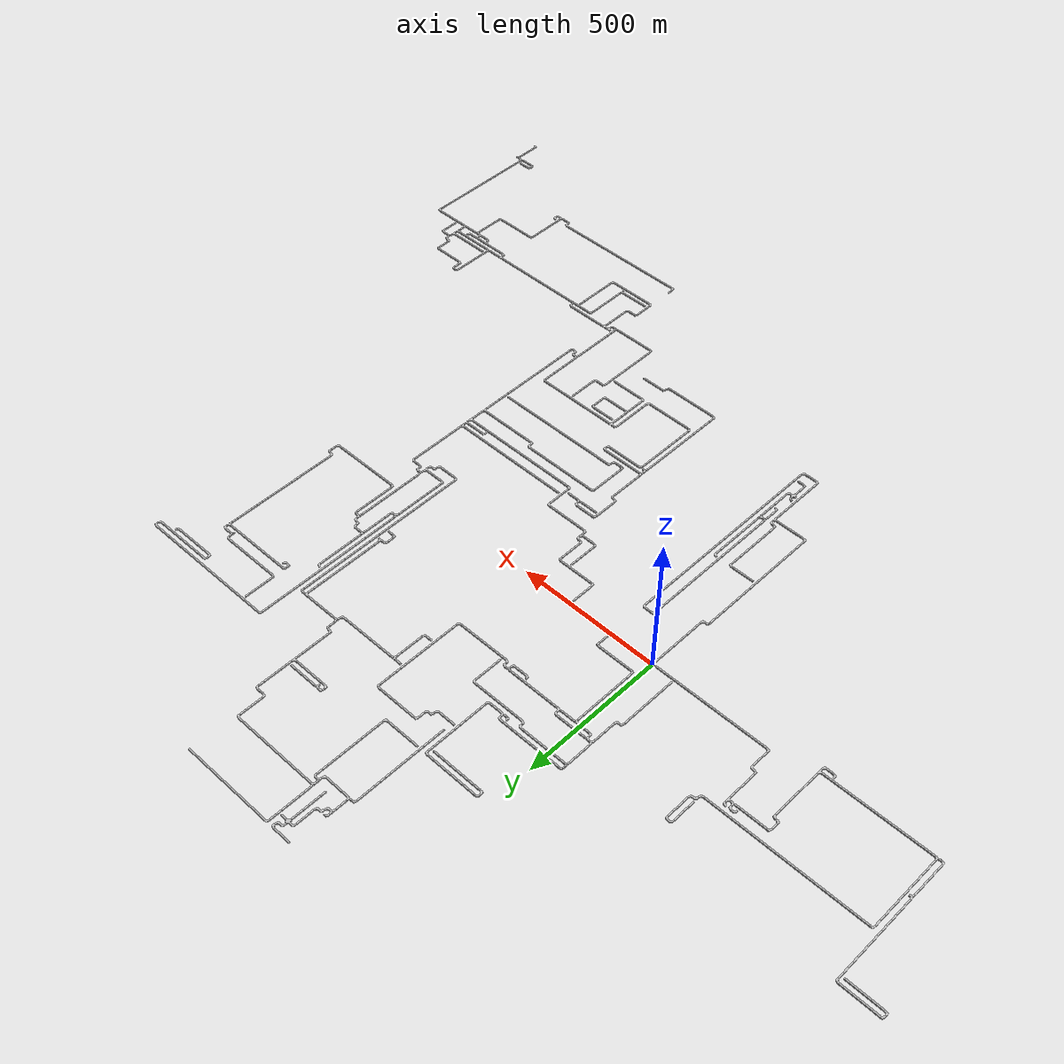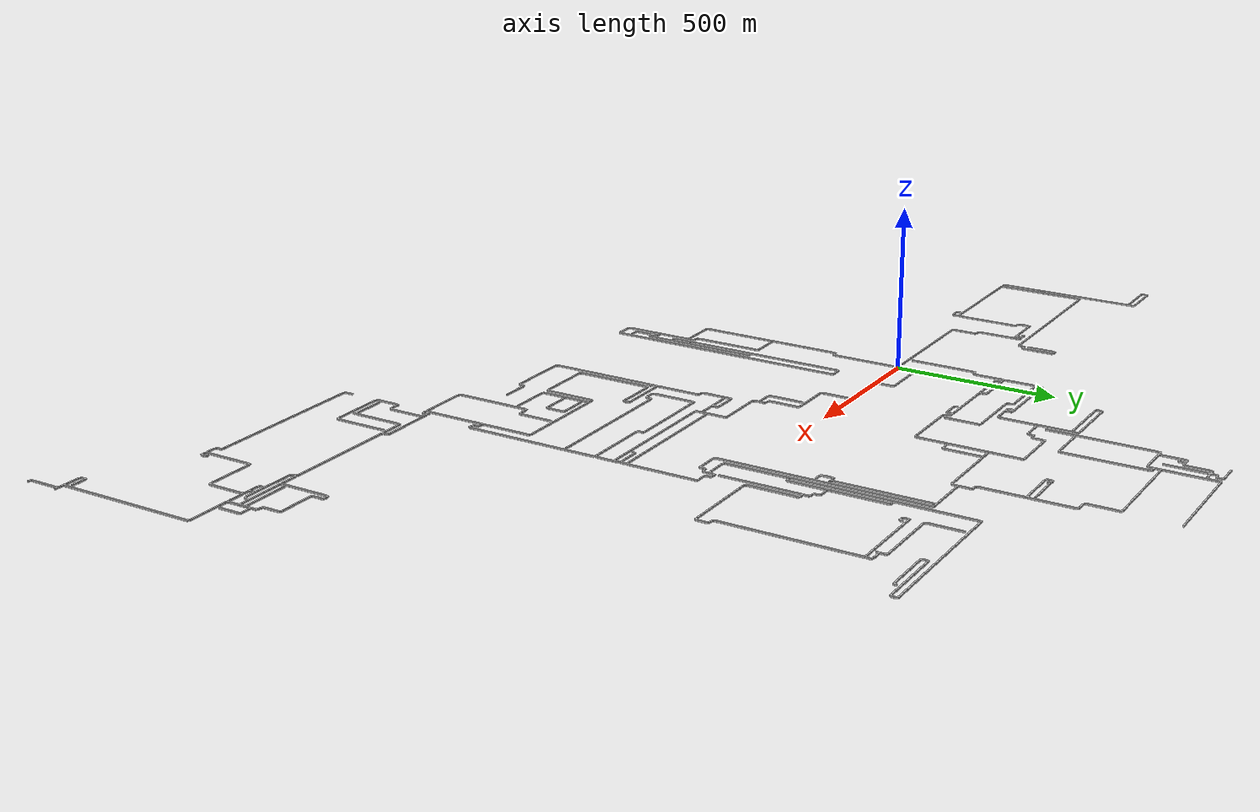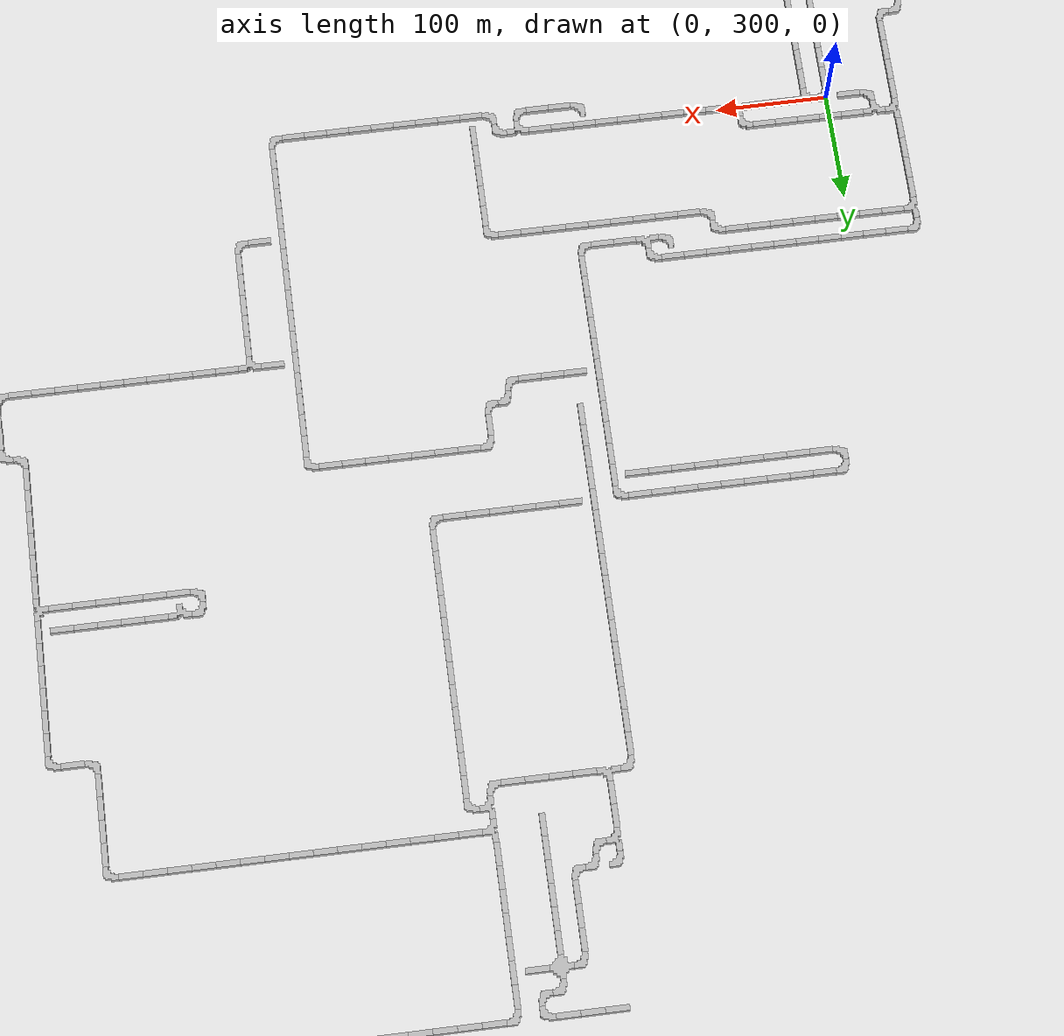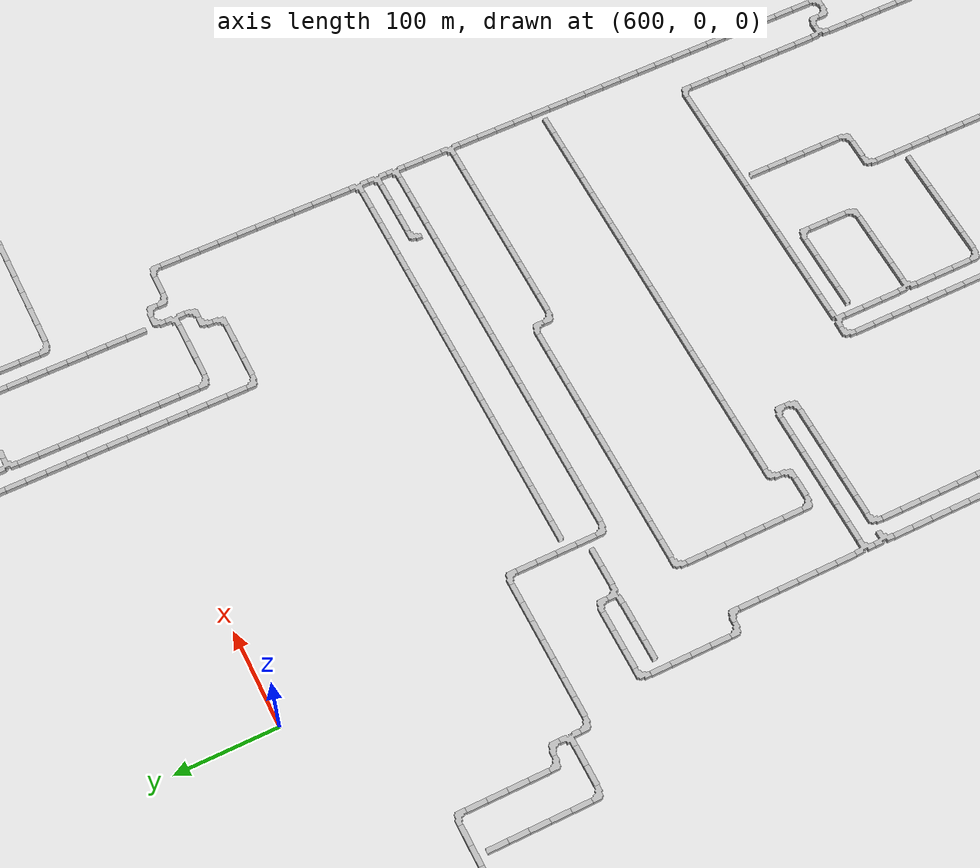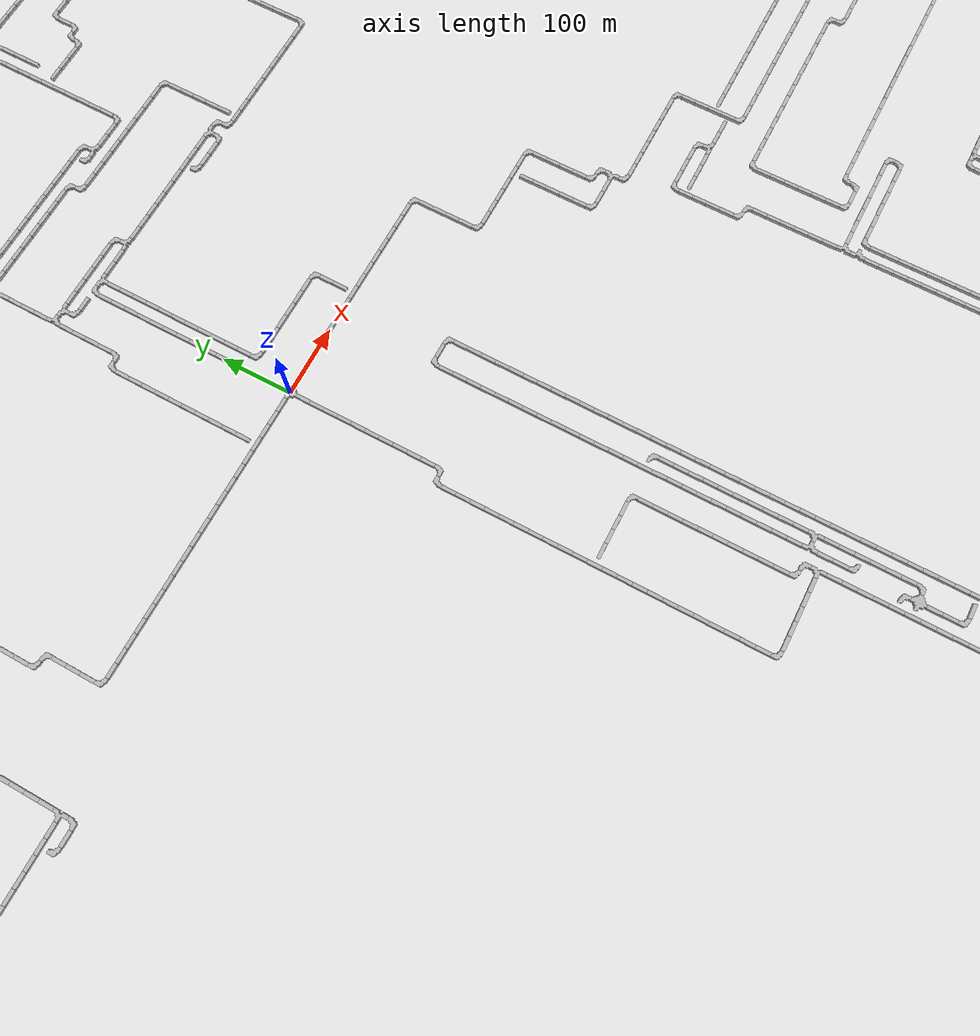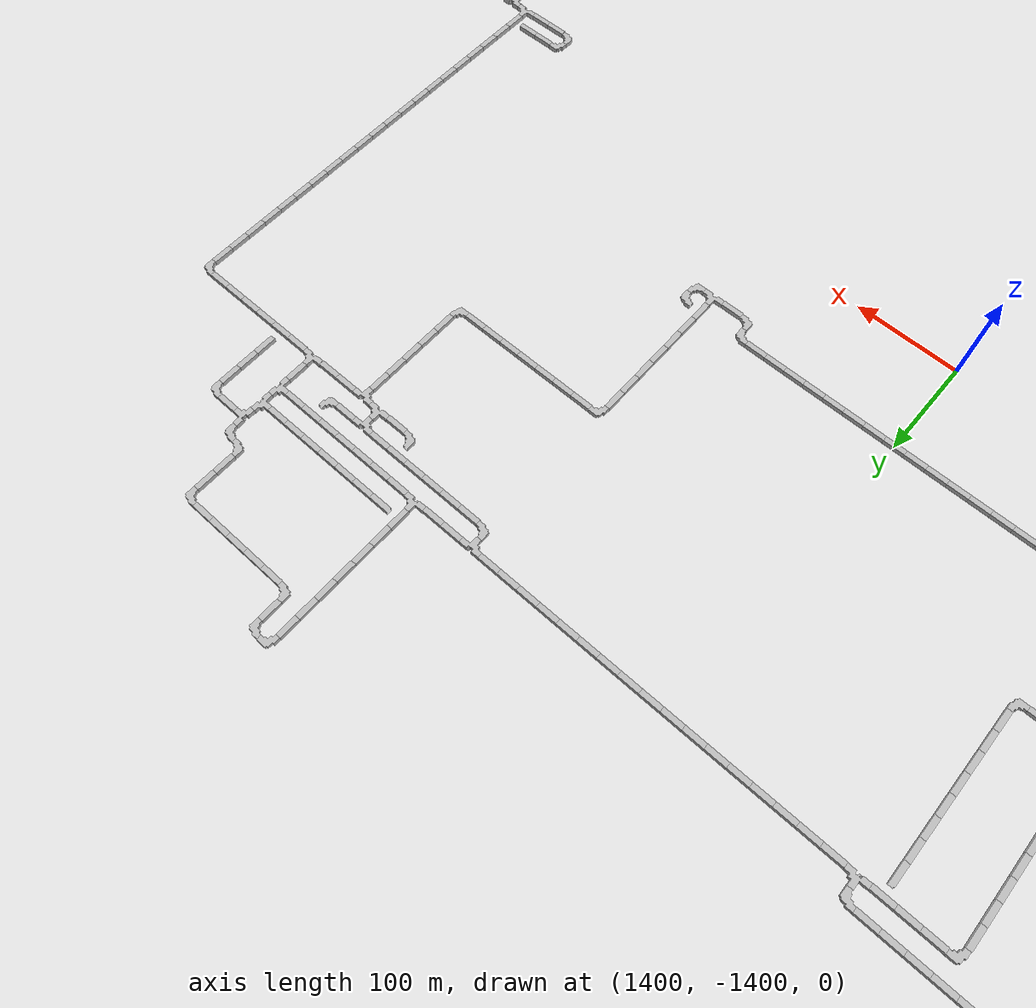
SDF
<sdf version="1.6">
 <world name="cave_32000_2">
  <include>
   <static>true</static>
   <name>cave_0_0</name>
   <pose>0 0 0 0 0 -1.5707963267948966</pose>
   <uri>model://cave_4way_20m</uri>
  </include>
  <include>
   <static>true</static>
   <name>cave_1_0</name>
   <pose>20 0 0 0 0 1.5707963267948966</pose>
   <uri>model://cave_straight_20m</uri>
  </include>
  <include>
   <static>true</static>
   <name>cave_2_0</name>
   <pose>40 0 0 0 0 1.5707963267948966</pose>
   <uri>model://cave_straight_20m</uri>
  </include>
  <include>
   <static>true</static>
   <name>cave_3_0</name>
   <pose>60 0 0 0 0 1.5707963267948966</pose>
   <uri>model://cave_straight_20m</uri>
  </include>
  <include>
   <static>true</static>
   <name>cave_4_0</name>
   <pose>80 0 0 0 0 1.5707963267948966</pose>
   <uri>model://cave_straight_20m</uri>
  </include>
  <include>
   <static>true</static>
   <name>cave_5_0</name>
   <pose>100 0 0 0 0 1.5707963267948966</pose>
   <uri>model://cave_straight_20m</uri>
  </include>
  <include>
   <static>true</static>
   <name>cave_6_0</name>
   <pose>120 0 0 0 0 1.5707963267948966</pose>
   <uri>model://cave_straight_20m</uri>
  </include>
  <include>
   <static>true</static>
   <name>cave_7_0</name>
   <pose>140 0 0 0 0 1.5707963267948966</pose>
   <uri>model://cave_straight_20m</uri>
  </include>
  <include>
   <static>true</static>
   <name>cave_8_0</name>
   <pose>160 0 0 0 0 1.5707963267948966</pose>
   <uri>model://cave_straight_20m</uri>
  </include>
  <include>
   <static>true</static>
   <name>cave_9_0</name>
   <pose>180 0 0 0 0 1.5707963267948966</pose>
   <uri>model://cave_straight_20m</uri>
  </include>
  <include>
   <static>true</static>
   <name>cave_10_0</name>
   <pose>200 0 0 0 0 1.5707963267948966</pose>
   <uri>model://cave_straight_20m</uri>
  </include>
  <include>
   <static>true</static>
   <name>cave_11_0</name>
   <pose>220 0 0 0 0 1.5707963267948966</pose>
   <uri>model://cave_straight_20m</uri>
  </include>
  <include>
   <static>true</static>
   <name>cave_12_0</name>
   <pose>240 0 0 0 0 1.5707963267948966</pose>
   <uri>model://cave_straight_20m</uri>
  </include>
  <include>
   <static>true</static>
   <name>cave_13_0</name>
   <pose>260 0 0 0 0 1.5707963267948966</pose>
   <uri>model://cave_straight_20m</uri>
  </include>
  <include>
   <static>true</static>
   <name>cave_14_0</name>
   <pose>280 0 0 0 0 1.5707963267948966</pose>
   <uri>model://cave_straight_20m</uri>
  </include>
  <include>
   <static>true</static>
   <name>cave_15_0</name>
   <pose>300 0 0 0 0 1.5707963267948966</pose>
   <uri>model://cave_straight_20m</uri>
  </include>
  <include>
   <static>true</static>
   <name>cave_16_0</name>
   <pose>320 0 0 0 0 3.141592653589793</pose>
   <uri>model://cave_L_20m</uri>
  </include>
  <include>
   <static>true</static>
   <name>cave_16_-1</name>
   <pose>320 -20 0 0 0 0.0</pose>
   <uri>model://cave_straight_20m</uri>
  </include>
  <include>
   <static>true</static>
   <name>cave_16_-2</name>
   <pose>320 -40 0 0 0 0.0</pose>
   <uri>model://cave_straight_20m</uri>
  </include>
  <include>
   <static>true</static>
   <name>cave_16_-3</name>
   <pose>320 -60 0 0 0 0.0</pose>
   <uri>model://cave_straight_20m</uri>
  </include>
  <include>
   <static>true</static>
   <name>cave_16_-4</name>
   <pose>320 -80 0 0 0 0.0</pose>
   <uri>model://cave_straight_20m</uri>
  </include>
  <include>
   <static>true</static>
   <name>cave_16_-5</name>
   <pose>320 -100 0 0 0 0.0</pose>
   <uri>model://cave_L_20m</uri>
  </include>
  <include>
   <static>true</static>
   <name>cave_17_-5</name>
   <pose>340 -100 0 0 0 1.5707963267948966</pose>
   <uri>model://cave_straight_20m</uri>
  </include>
  <include>
   <static>true</static>
   <name>cave_18_-5</name>
   <pose>360 -100 0 0 0 1.5707963267948966</pose>
   <uri>model://cave_straight_20m</uri>
  </include>
  <include>
   <static>true</static>
   <name>cave_19_-5</name>
   <pose>380 -100 0 0 0 1.5707963267948966</pose>
   <uri>model://cave_straight_20m</uri>
  </include>
  <include>
   <static>true</static>
   <name>cave_20_-5</name>
   <pose>400 -100 0 0 0 1.5707963267948966</pose>
   <uri>model://cave_straight_20m</uri>
  </include>
  <include>
   <static>true</static>
   <name>cave_21_-5</name>
   <pose>420 -100 0 0 0 1.5707963267948966</pose>
   <uri>model://cave_straight_20m</uri>
  </include>
  <include>
   <static>true</static>
   <name>cave_22_-5</name>
   <pose>440 -100 0 0 0 1.5707963267948966</pose>
   <uri>model://cave_straight_20m</uri>
  </include>
  <include>
   <static>true</static>
   <name>cave_23_-5</name>
   <pose>460 -100 0 0 0 3.141592653589793</pose>
   <uri>model://cave_L_20m</uri>
  </include>
  <include>
   <static>true</static>
   <name>cave_23_-6</name>
   <pose>460 -120 0 0 0 0.0</pose>
   <uri>model://cave_straight_20m</uri>
  </include>
  <include>
   <static>true</static>
   <name>cave_23_-7</name>
   <pose>460 -140 0 0 0 0.0</pose>
   <uri>model://cave_straight_20m</uri>
  </include>
  <include>
   <static>true</static>
   <name>cave_23_-8</name>
   <pose>460 -160 0 0 0 0.0</pose>
   <uri>model://cave_straight_20m</uri>
  </include>
  <include>
   <static>true</static>
   <name>cave_23_-9</name>
   <pose>460 -180 0 0 0 0.0</pose>
   <uri>model://cave_straight_20m</uri>
  </include>
  <include>
   <static>true</static>
   <name>cave_23_-10</name>
   <pose>460 -200 0 0 0 0.0</pose>
   <uri>model://cave_L_20m</uri>
  </include>
  <include>
   <static>true</static>
   <name>cave_24_-10</name>
   <pose>480 -200 0 0 0 3.141592653589793</pose>
   <uri>model://cave_L_20m</uri>
  </include>
  <include>
   <static>true</static>
   <name>cave_24_-11</name>
   <pose>480 -220 0 0 0 1.5707963267948966</pose>
   <uri>model://cave_3way_20m</uri>
  </include>
  <include>
   <static>true</static>
   <name>cave_24_-12</name>
   <pose>480 -240 0 0 0 0.0</pose>
   <uri>model://cave_L_20m</uri>
  </include>
  <include>
   <static>true</static>
   <name>cave_25_-12</name>
   <pose>500 -240 0 0 0 1.5707963267948966</pose>
   <uri>model://cave_straight_20m</uri>
  </include>
  <include>
   <static>true</static>
   <name>cave_26_-12</name>
   <pose>520 -240 0 0 0 1.5707963267948966</pose>
   <uri>model://cave_straight_20m</uri>
  </include>
  <include>
   <static>true</static>
   <name>cave_27_-12</name>
   <pose>540 -240 0 0 0 1.5707963267948966</pose>
   <uri>model://cave_straight_20m</uri>
  </include>
  <include>
   <static>true</static>
   <name>cave_28_-12</name>
   <pose>560 -240 0 0 0 1.5707963267948966</pose>
   <uri>model://cave_straight_20m</uri>
  </include>
  <include>
   <static>true</static>
   <name>cave_29_-12</name>
   <pose>580 -240 0 0 0 1.5707963267948966</pose>
   <uri>model://cave_straight_20m</uri>
  </include>
  <include>
   <static>true</static>
   <name>cave_30_-12</name>
   <pose>600 -240 0 0 0 1.5707963267948966</pose>
   <uri>model://cave_straight_20m</uri>
  </include>
  <include>
   <static>true</static>
   <name>cave_31_-12</name>
   <pose>620 -240 0 0 0 1.5707963267948966</pose>
   <uri>model://cave_straight_20m</uri>
  </include>
  <include>
   <static>true</static>
   <name>cave_32_-12</name>
   <pose>640 -240 0 0 0 3.141592653589793</pose>
   <uri>model://cave_L_20m</uri>
  </include>
  <include>
   <static>true</static>
   <name>cave_32_-13</name>
   <pose>640 -260 0 0 0 0.0</pose>
   <uri>model://cave_straight_20m</uri>
  </include>
  <include>
   <static>true</static>
   <name>cave_32_-14</name>
   <pose>640 -280 0 0 0 0.0</pose>
   <uri>model://cave_straight_20m</uri>
  </include>
  <include>
   <static>true</static>
   <name>cave_32_-15</name>
   <pose>640 -300 0 0 0 0.0</pose>
   <uri>model://cave_straight_20m</uri>
  </include>
  <include>
   <static>true</static>
   <name>cave_32_-16</name>
   <pose>640 -320 0 0 0 0.0</pose>
   <uri>model://cave_straight_20m</uri>
  </include>
  <include>
   <static>true</static>
   <name>cave_32_-17</name>
   <pose>640 -340 0 0 0 0.0</pose>
   <uri>model://cave_L_20m</uri>
  </include>
  <include>
   <static>true</static>
   <name>cave_33_-17</name>
   <pose>660 -340 0 0 0 1.5707963267948966</pose>
   <uri>model://cave_straight_20m</uri>
  </include>
  <include>
   <static>true</static>
   <name>cave_34_-17</name>
   <pose>680 -340 0 0 0 1.5707963267948966</pose>
   <uri>model://cave_straight_20m</uri>
  </include>
  <include>
   <static>true</static>
   <name>cave_35_-17</name>
   <pose>700 -340 0 0 0 1.5707963267948966</pose>
   <uri>model://cave_straight_20m</uri>
  </include>
  <include>
   <static>true</static>
   <name>cave_36_-17</name>
   <pose>720 -340 0 0 0 1.5707963267948966</pose>
   <uri>model://cave_straight_20m</uri>
  </include>
  <include>
   <static>true</static>
   <name>cave_37_-17</name>
   <pose>740 -340 0 0 0 1.5707963267948966</pose>
   <uri>model://cave_straight_20m</uri>
  </include>
  <include>
   <static>true</static>
   <name>cave_38_-17</name>
   <pose>760 -340 0 0 0 1.5707963267948966</pose>
   <uri>model://cave_straight_20m</uri>
  </include>
  <include>
   <static>true</static>
   <name>cave_39_-17</name>
   <pose>780 -340 0 0 0 1.5707963267948966</pose>
   <uri>model://cave_straight_20m</uri>
  </include>
  <include>
   <static>true</static>
   <name>cave_40_-17</name>
   <pose>800 -340 0 0 0 1.5707963267948966</pose>
   <uri>model://cave_straight_20m</uri>
  </include>
  <include>
   <static>true</static>
   <name>cave_41_-17</name>
   <pose>820 -340 0 0 0 1.5707963267948966</pose>
   <uri>model://cave_straight_20m</uri>
  </include>
  <include>
   <static>true</static>
   <name>cave_42_-17</name>
   <pose>840 -340 0 0 0 1.5707963267948966</pose>
   <uri>model://cave_straight_20m</uri>
  </include>
  <include>
   <static>true</static>
   <name>cave_43_-17</name>
   <pose>860 -340 0 0 0 1.5707963267948966</pose>
   <uri>model://cave_straight_20m</uri>
  </include>
  <include>
   <static>true</static>
   <name>cave_44_-17</name>
   <pose>880 -340 0 0 0 1.5707963267948966</pose>
   <uri>model://cave_straight_20m</uri>
  </include>
  <include>
   <static>true</static>
   <name>cave_45_-17</name>
   <pose>900 -340 0 0 0 1.5707963267948966</pose>
   <uri>model://cave_straight_20m</uri>
  </include>
  <include>
   <static>true</static>
   <name>cave_46_-17</name>
   <pose>920 -340 0 0 0 1.5707963267948966</pose>
   <uri>model://cave_straight_20m</uri>
  </include>
  <include>
   <static>true</static>
   <name>cave_47_-17</name>
   <pose>940 -340 0 0 0 1.5707963267948966</pose>
   <uri>model://cave_straight_20m</uri>
  </include>
  <include>
   <static>true</static>
   <name>cave_48_-17</name>
   <pose>960 -340 0 0 0 1.5707963267948966</pose>
   <uri>model://cave_straight_20m</uri>
  </include>
  <include>
   <static>true</static>
   <name>cave_49_-17</name>
   <pose>980 -340 0 0 0 1.5707963267948966</pose>
   <uri>model://cave_straight_20m</uri>
  </include>
  <include>
   <static>true</static>
   <name>cave_50_-17</name>
   <pose>1000 -340 0 0 0 1.5707963267948966</pose>
   <uri>model://cave_straight_20m</uri>
  </include>
  <include>
   <static>true</static>
   <name>cave_51_-17</name>
   <pose>1020 -340 0 0 0 1.5707963267948966</pose>
   <uri>model://cave_straight_20m</uri>
  </include>
  <include>
   <static>true</static>
   <name>cave_52_-17</name>
   <pose>1040 -340 0 0 0 1.5707963267948966</pose>
   <uri>model://cave_straight_20m</uri>
  </include>
  <include>
   <static>true</static>
   <name>cave_53_-17</name>
   <pose>1060 -340 0 0 0 1.5707963267948966</pose>
   <uri>model://cave_straight_20m</uri>
  </include>
  <include>
   <static>true</static>
   <name>cave_54_-17</name>
   <pose>1080 -340 0 0 0 1.5707963267948966</pose>
   <uri>model://cave_3way_20m</uri>
  </include>
  <include>
   <static>true</static>
   <name>cave_54_-18</name>
   <pose>1080 -360 0 0 0 0.0</pose>
   <uri>model://cave_straight_20m</uri>
  </include>
  <include>
   <static>true</static>
   <name>cave_54_-19</name>
   <pose>1080 -380 0 0 0 0.0</pose>
   <uri>model://cave_straight_20m</uri>
  </include>
  <include>
   <static>true</static>
   <name>cave_54_-20</name>
   <pose>1080 -400 0 0 0 1.5707963267948966</pose>
   <uri>model://cave_3way_20m</uri>
  </include>
  <include>
   <static>true</static>
   <name>cave_54_-21</name>
   <pose>1080 -420 0 0 0 0.0</pose>
   <uri>model://cave_straight_20m</uri>
  </include>
  <include>
   <static>true</static>
   <name>cave_54_-22</name>
   <pose>1080 -440 0 0 0 0.0</pose>
   <uri>model://cave_straight_20m</uri>
  </include>
  <include>
   <static>true</static>
   <name>cave_54_-23</name>
   <pose>1080 -460 0 0 0 0.0</pose>
   <uri>model://cave_straight_20m</uri>
  </include>
  <include>
   <static>true</static>
   <name>cave_54_-24</name>
   <pose>1080 -480 0 0 0 0.0</pose>
   <uri>model://cave_straight_20m</uri>
  </include>
  <include>
   <static>true</static>
   <name>cave_54_-25</name>
   <pose>1080 -500 0 0 0 0.0</pose>
   <uri>model://cave_straight_20m</uri>
  </include>
  <include>
   <static>true</static>
   <name>cave_54_-26</name>
   <pose>1080 -520 0 0 0 0.0</pose>
   <uri>model://cave_straight_20m</uri>
  </include>
  <include>
   <static>true</static>
   <name>cave_54_-27</name>
   <pose>1080 -540 0 0 0 0.0</pose>
   <uri>model://cave_straight_20m</uri>
  </include>
  <include>
   <static>true</static>
   <name>cave_54_-28</name>
   <pose>1080 -560 0 0 0 0.0</pose>
   <uri>model://cave_straight_20m</uri>
  </include>
  <include>
   <static>true</static>
   <name>cave_54_-29</name>
   <pose>1080 -580 0 0 0 0.0</pose>
   <uri>model://cave_straight_20m</uri>
  </include>
  <include>
   <static>true</static>
   <name>cave_54_-30</name>
   <pose>1080 -600 0 0 0 0.0</pose>
   <uri>model://cave_straight_20m</uri>
  </include>
  <include>
   <static>true</static>
   <name>cave_54_-31</name>
   <pose>1080 -620 0 0 0 0.0</pose>
   <uri>model://cave_straight_20m</uri>
  </include>
  <include>
   <static>true</static>
   <name>cave_54_-32</name>
   <pose>1080 -640 0 0 0 0.0</pose>
   <uri>model://cave_straight_20m</uri>
  </include>
  <include>
   <static>true</static>
   <name>cave_54_-33</name>
   <pose>1080 -660 0 0 0 0.0</pose>
   <uri>model://cave_straight_20m</uri>
  </include>
  <include>
   <static>true</static>
   <name>cave_54_-34</name>
   <pose>1080 -680 0 0 0 0.0</pose>
   <uri>model://cave_straight_20m</uri>
  </include>
  <include>
   <static>true</static>
   <name>cave_54_-35</name>
   <pose>1080 -700 0 0 0 0.0</pose>
   <uri>model://cave_straight_20m</uri>
  </include>
  <include>
   <static>true</static>
   <name>cave_54_-36</name>
   <pose>1080 -720 0 0 0 0.0</pose>
   <uri>model://cave_straight_20m</uri>
  </include>
  <include>
   <static>true</static>
   <name>cave_54_-37</name>
   <pose>1080 -740 0 0 0 0.0</pose>
   <uri>model://cave_straight_20m</uri>
  </include>
  <include>
   <static>true</static>
   <name>cave_54_-38</name>
   <pose>1080 -760 0 0 0 0.0</pose>
   <uri>model://cave_straight_20m</uri>
  </include>
  <include>
   <static>true</static>
   <name>cave_54_-39</name>
   <pose>1080 -780 0 0 0 0.0</pose>
   <uri>model://cave_straight_20m</uri>
  </include>
  <include>
   <static>true</static>
   <name>cave_54_-40</name>
   <pose>1080 -800 0 0 0 0.0</pose>
   <uri>model://cave_straight_20m</uri>
  </include>
  <include>
   <static>true</static>
   <name>cave_54_-41</name>
   <pose>1080 -820 0 0 0 1.5707963267948966</pose>
   <uri>model://cave_L_20m</uri>
  </include>
  <include>
   <static>true</static>
   <name>cave_53_-41</name>
   <pose>1060 -820 0 0 0 0.0</pose>
   <uri>model://cave_L_20m</uri>
  </include>
  <include>
   <static>true</static>
   <name>cave_53_-40</name>
   <pose>1060 -800 0 0 0 3.141592653589793</pose>
   <uri>model://cave_L_20m</uri>
  </include>
  <include>
   <static>true</static>
   <name>cave_52_-40</name>
   <pose>1040 -800 0 0 0 -1.5707963267948966</pose>
   <uri>model://cave_3way_20m</uri>
  </include>
  <include>
   <static>true</static>
   <name>cave_52_-41</name>
   <pose>1040 -820 0 0 0 0.0</pose>
   <uri>model://cave_straight_20m</uri>
  </include>
  <include>
   <static>true</static>
   <name>cave_52_-42</name>
   <pose>1040 -840 0 0 0 0.0</pose>
   <uri>model://cave_straight_20m</uri>
  </include>
  <include>
   <static>true</static>
   <name>cave_52_-43</name>
   <pose>1040 -860 0 0 0 0.0</pose>
   <uri>model://cave_straight_20m</uri>
  </include>
  <include>
   <static>true</static>
   <name>cave_52_-44</name>
   <pose>1040 -880 0 0 0 0.0</pose>
   <uri>model://cave_straight_20m</uri>
  </include>
  <include>
   <static>true</static>
   <name>cave_52_-45</name>
   <pose>1040 -900 0 0 0 0.0</pose>
   <uri>model://cave_straight_20m</uri>
  </include>
  <include>
   <static>true</static>
   <name>cave_52_-46</name>
   <pose>1040 -920 0 0 0 0.0</pose>
   <uri>model://cave_straight_20m</uri>
  </include>
  <include>
   <static>true</static>
   <name>cave_52_-47</name>
   <pose>1040 -940 0 0 0 0.0</pose>
   <uri>model://cave_straight_20m</uri>
  </include>
  <include>
   <static>true</static>
   <name>cave_52_-48</name>
   <pose>1040 -960 0 0 0 0.0</pose>
   <uri>model://cave_straight_20m</uri>
  </include>
  <include>
   <static>true</static>
   <name>cave_52_-49</name>
   <pose>1040 -980 0 0 0 0.0</pose>
   <uri>model://cave_straight_20m</uri>
  </include>
  <include>
   <static>true</static>
   <name>cave_52_-50</name>
   <pose>1040 -1000 0 0 0 0.0</pose>
   <uri>model://cave_3way_20m</uri>
  </include>
  <include>
   <static>true</static>
   <name>cave_53_-50</name>
   <pose>1060 -1000 0 0 0 1.5707963267948966</pose>
   <uri>model://cave_L_20m</uri>
  </include>
  <include>
   <static>true</static>
   <name>cave_53_-49</name>
   <pose>1060 -980 0 0 0 3.141592653589793</pose>
   <uri>model://cave_3way_20m</uri>
  </include>
  <include>
   <static>true</static>
   <name>cave_54_-49</name>
   <pose>1080 -980 0 0 0 3.141592653589793</pose>
   <uri>model://cave_3way_20m</uri>
  </include>
  <include>
   <static>true</static>
   <name>cave_55_-49</name>
   <pose>1100 -980 0 0 0 1.5707963267948966</pose>
   <uri>model://cave_straight_20m</uri>
  </include>
  <include>
   <static>true</static>
   <name>cave_56_-49</name>
   <pose>1120 -980 0 0 0 1.5707963267948966</pose>
   <uri>model://cave_straight_20m</uri>
  </include>
  <include>
   <static>true</static>
   <name>cave_57_-49</name>
   <pose>1140 -980 0 0 0 1.5707963267948966</pose>
   <uri>model://cave_straight_20m</uri>
  </include>
  <include>
   <static>true</static>
   <name>cave_58_-49</name>
   <pose>1160 -980 0 0 0 1.5707963267948966</pose>
   <uri>model://cave_straight_20m</uri>
  </include>
  <include>
   <static>true</static>
   <name>cave_59_-49</name>
   <pose>1180 -980 0 0 0 1.5707963267948966</pose>
   <uri>model://cave_straight_20m</uri>
  </include>
  <include>
   <static>true</static>
   <name>cave_60_-49</name>
   <pose>1200 -980 0 0 0 1.5707963267948966</pose>
   <uri>model://cave_straight_20m</uri>
  </include>
  <include>
   <static>true</static>
   <name>cave_61_-49</name>
   <pose>1220 -980 0 0 0 1.5707963267948966</pose>
   <uri>model://cave_straight_20m</uri>
  </include>
  <include>
   <static>true</static>
   <name>cave_62_-49</name>
   <pose>1240 -980 0 0 0 3.141592653589793</pose>
   <uri>model://cave_L_20m</uri>
  </include>
  <include>
   <static>true</static>
   <name>cave_62_-50</name>
   <pose>1240 -1000 0 0 0 0.0</pose>
   <uri>model://cave_3way_20m</uri>
  </include>
  <include>
   <static>true</static>
   <name>cave_63_-50</name>
   <pose>1260 -1000 0 0 0 1.5707963267948966</pose>
   <uri>model://cave_straight_20m</uri>
  </include>
  <include>
   <static>true</static>
   <name>cave_64_-50</name>
   <pose>1280 -1000 0 0 0 1.5707963267948966</pose>
   <uri>model://cave_straight_20m</uri>
  </include>
  <include>
   <static>true</static>
   <name>cave_65_-50</name>
   <pose>1300 -1000 0 0 0 1.5707963267948966</pose>
   <uri>model://cave_straight_20m</uri>
  </include>
  <include>
   <static>true</static>
   <name>cave_66_-50</name>
   <pose>1320 -1000 0 0 0 1.5707963267948966</pose>
   <uri>model://cave_straight_20m</uri>
  </include>
  <include>
   <static>true</static>
   <name>cave_67_-50</name>
   <pose>1340 -1000 0 0 0 1.5707963267948966</pose>
   <uri>model://cave_straight_20m</uri>
  </include>
  <include>
   <static>true</static>
   <name>cave_68_-50</name>
   <pose>1360 -1000 0 0 0 1.5707963267948966</pose>
   <uri>model://cave_straight_20m</uri>
  </include>
  <include>
   <static>true</static>
   <name>cave_69_-50</name>
   <pose>1380 -1000 0 0 0 1.5707963267948966</pose>
   <uri>model://cave_straight_20m</uri>
  </include>
  <include>
   <static>true</static>
   <name>cave_70_-50</name>
   <pose>1400 -1000 0 0 0 1.5707963267948966</pose>
   <uri>model://cave_straight_20m</uri>
  </include>
  <include>
   <static>true</static>
   <name>cave_71_-50</name>
   <pose>1420 -1000 0 0 0 1.5707963267948966</pose>
   <uri>model://cave_straight_20m</uri>
  </include>
  <include>
   <static>true</static>
   <name>cave_72_-50</name>
   <pose>1440 -1000 0 0 0 1.5707963267948966</pose>
   <uri>model://cave_straight_20m</uri>
  </include>
  <include>
   <static>true</static>
   <name>cave_73_-50</name>
   <pose>1460 -1000 0 0 0 1.5707963267948966</pose>
   <uri>model://cave_straight_20m</uri>
  </include>
  <include>
   <static>true</static>
   <name>cave_74_-50</name>
   <pose>1480 -1000 0 0 0 1.5707963267948966</pose>
   <uri>model://cave_straight_20m</uri>
  </include>
  <include>
   <static>true</static>
   <name>cave_75_-50</name>
   <pose>1500 -1000 0 0 0 1.5707963267948966</pose>
   <uri>model://cave_straight_20m</uri>
  </include>
  <include>
   <static>true</static>
   <name>cave_76_-50</name>
   <pose>1520 -1000 0 0 0 1.5707963267948966</pose>
   <uri>model://cave_straight_20m</uri>
  </include>
  <include>
   <static>true</static>
   <name>cave_77_-50</name>
   <pose>1540 -1000 0 0 0 1.5707963267948966</pose>
   <uri>model://cave_straight_20m</uri>
  </include>
  <include>
   <static>true</static>
   <name>cave_78_-50</name>
   <pose>1560 -1000 0 0 0 1.5707963267948966</pose>
   <uri>model://cave_straight_20m</uri>
  </include>
  <include>
   <static>true</static>
   <name>cave_79_-50</name>
   <pose>1580 -1000 0 0 0 1.5707963267948966</pose>
   <uri>model://cave_straight_20m</uri>
  </include>
  <include>
   <static>true</static>
   <name>cave_80_-50</name>
   <pose>1600 -1000 0 0 0 3.141592653589793</pose>
   <uri>model://cave_3way_20m</uri>
  </include>
  <include>
   <static>true</static>
   <name>cave_81_-50</name>
   <pose>1620 -1000 0 0 0 1.5707963267948966</pose>
   <uri>model://cave_straight_20m</uri>
  </include>
  <include>
   <static>true</static>
   <name>cave_82_-50</name>
   <pose>1640 -1000 0 0 0 1.5707963267948966</pose>
   <uri>model://cave_straight_20m</uri>
  </include>
  <include>
   <static>true</static>
   <name>cave_83_-50</name>
   <pose>1660 -1000 0 0 0 0.0</pose>
   <uri>model://cave_3way_20m</uri>
  </include>
  <include>
   <static>true</static>
   <name>cave_84_-50</name>
   <pose>1680 -1000 0 0 0 1.5707963267948966</pose>
   <uri>model://cave_straight_20m</uri>
  </include>
  <include>
   <static>true</static>
   <name>cave_85_-50</name>
   <pose>1700 -1000 0 0 0 1.5707963267948966</pose>
   <uri>model://cave_straight_20m</uri>
  </include>
  <include>
   <static>true</static>
   <name>cave_86_-50</name>
   <pose>1720 -1000 0 0 0 1.5707963267948966</pose>
   <uri>model://cave_straight_20m</uri>
  </include>
  <include>
   <static>true</static>
   <name>cave_87_-50</name>
   <pose>1740 -1000 0 0 0 1.5707963267948966</pose>
   <uri>model://cave_straight_20m</uri>
  </include>
  <include>
   <static>true</static>
   <name>cave_88_-50</name>
   <pose>1760 -1000 0 0 0 1.5707963267948966</pose>
   <uri>model://cave_straight_20m</uri>
  </include>
  <include>
   <static>true</static>
   <name>cave_89_-50</name>
   <pose>1780 -1000 0 0 0 1.5707963267948966</pose>
   <uri>model://cave_straight_20m</uri>
  </include>
  <include>
   <static>true</static>
   <name>cave_90_-50</name>
   <pose>1800 -1000 0 0 0 1.5707963267948966</pose>
   <uri>model://cave_straight_20m</uri>
  </include>
  <include>
   <static>true</static>
   <name>cave_91_-50</name>
   <pose>1820 -1000 0 0 0 1.5707963267948966</pose>
   <uri>model://cave_3way_20m</uri>
  </include>
  <include>
   <static>true</static>
   <name>cave_91_-51</name>
   <pose>1820 -1020 0 0 0 0.0</pose>
   <uri>model://cave_straight_20m</uri>
  </include>
  <include>
   <static>true</static>
   <name>cave_91_-52</name>
   <pose>1820 -1040 0 0 0 0.0</pose>
   <uri>model://cave_3way_20m</uri>
  </include>
  <include>
   <static>true</static>
   <name>cave_92_-52</name>
   <pose>1840 -1040 0 0 0 1.5707963267948966</pose>
   <uri>model://cave_straight_20m</uri>
  </include>
  <include>
   <static>true</static>
   <name>cave_93_-52</name>
   <pose>1860 -1040 0 0 0 1.5707963267948966</pose>
   <uri>model://cave_straight_20m</uri>
  </include>
  <include>
   <static>true</static>
   <name>cave_94_-52</name>
   <pose>1880 -1040 0 0 0 1.5707963267948966</pose>
   <uri>model://cave_straight_20m</uri>
  </include>
  <include>
   <static>true</static>
   <name>cave_95_-52</name>
   <pose>1900 -1040 0 0 0 1.5707963267948966</pose>
   <uri>model://cave_straight_20m</uri>
  </include>
  <include>
   <static>true</static>
   <name>cave_96_-52</name>
   <pose>1920 -1040 0 0 0 1.5707963267948966</pose>
   <uri>model://cave_straight_20m</uri>
  </include>
  <include>
   <static>true</static>
   <name>cave_97_-52</name>
   <pose>1940 -1040 0 0 0 1.5707963267948966</pose>
   <uri>model://cave_straight_20m</uri>
  </include>
  <include>
   <static>true</static>
   <name>cave_98_-52</name>
   <pose>1960 -1040 0 0 0 3.141592653589793</pose>
   <uri>model://cave_L_20m</uri>
  </include>
  <include>
   <static>true</static>
   <name>cave_98_-53</name>
   <pose>1960 -1060 0 0 0 0.0</pose>
   <uri>model://cave_straight_20m</uri>
  </include>
  <include>
   <static>true</static>
   <name>cave_98_-54</name>
   <pose>1960 -1080 0 0 0 0.0</pose>
   <uri>model://cave_straight_20m</uri>
  </include>
  <include>
   <static>true</static>
   <name>cave_98_-55</name>
   <pose>1960 -1100 0 0 0 0.0</pose>
   <uri>model://cave_straight_20m</uri>
  </include>
  <include>
   <static>true</static>
   <name>cave_98_-56</name>
   <pose>1960 -1120 0 0 0 0.0</pose>
   <uri>model://cave_straight_20m</uri>
  </include>
  <include>
   <static>true</static>
   <name>cave_98_-57</name>
   <pose>1960 -1140 0 0 0 0.0</pose>
   <uri>model://cave_straight_20m</uri>
  </include>
  <include>
   <static>true</static>
   <name>cave_98_-58</name>
   <pose>1960 -1160 0 0 0 0.0</pose>
   <uri>model://cave_straight_20m</uri>
  </include>
  <include>
   <static>true</static>
   <name>cave_98_-59</name>
   <pose>1960 -1180 0 0 0 0.0</pose>
   <uri>model://cave_straight_20m</uri>
  </include>
  <include>
   <static>true</static>
   <name>cave_98_-60</name>
   <pose>1960 -1200 0 0 0 0.0</pose>
   <uri>model://cave_straight_20m</uri>
  </include>
  <include>
   <static>true</static>
   <name>cave_98_-61</name>
   <pose>1960 -1220 0 0 0 0.0</pose>
   <uri>model://cave_straight_20m</uri>
  </include>
  <include>
   <static>true</static>
   <name>cave_98_-62</name>
   <pose>1960 -1240 0 0 0 0.0</pose>
   <uri>model://cave_straight_20m</uri>
  </include>
  <include>
   <static>true</static>
   <name>cave_98_-63</name>
   <pose>1960 -1260 0 0 0 0.0</pose>
   <uri>model://cave_straight_20m</uri>
  </include>
  <include>
   <static>true</static>
   <name>cave_98_-64</name>
   <pose>1960 -1280 0 0 0 0.0</pose>
   <uri>model://cave_straight_20m</uri>
  </include>
  <include>
   <static>true</static>
   <name>cave_98_-65</name>
   <pose>1960 -1300 0 0 0 0.0</pose>
   <uri>model://cave_straight_20m</uri>
  </include>
  <include>
   <static>true</static>
   <name>cave_98_-66</name>
   <pose>1960 -1320 0 0 0 0.0</pose>
   <uri>model://cave_straight_20m</uri>
  </include>
  <include>
   <static>true</static>
   <name>cave_98_-67</name>
   <pose>1960 -1340 0 0 0 0.0</pose>
   <uri>model://cave_straight_20m</uri>
  </include>
  <include>
   <static>true</static>
   <name>cave_98_-68</name>
   <pose>1960 -1360 0 0 0 0.0</pose>
   <uri>model://cave_straight_20m</uri>
  </include>
  <include>
   <static>true</static>
   <name>cave_98_-69</name>
   <pose>1960 -1380 0 0 0 0.0</pose>
   <uri>model://cave_straight_20m</uri>
  </include>
  <include>
   <static>true</static>
   <name>cave_98_-70</name>
   <pose>1960 -1400 0 0 0 0.0</pose>
   <uri>model://cave_straight_20m</uri>
  </include>
  <include>
   <static>true</static>
   <name>cave_98_-71</name>
   <pose>1960 -1420 0 0 0 0.0</pose>
   <uri>model://cave_straight_20m</uri>
  </include>
  <include>
   <static>true</static>
   <name>cave_98_-72</name>
   <pose>1960 -1440 0 0 0 0.0</pose>
   <uri>model://cave_straight_20m</uri>
  </include>
  <include>
   <static>true</static>
   <name>cave_98_-73</name>
   <pose>1960 -1460 0 0 0 0.0</pose>
   <uri>model://cave_straight_20m</uri>
  </include>
  <include>
   <static>true</static>
   <name>cave_98_-74</name>
   <pose>1960 -1480 0 0 0 0.0</pose>
   <uri>model://cave_3way_20m</uri>
  </include>
  <include>
   <static>true</static>
   <name>cave_99_-74</name>
   <pose>1980 -1480 0 0 0 3.141592653589793</pose>
   <uri>model://cave_3way_20m</uri>
  </include>
  <include>
   <static>true</static>
   <name>cave_99_-75</name>
   <pose>1980 -1500 0 0 0 0.0</pose>
   <uri>model://cave_straight_20m</uri>
  </include>
  <include>
   <static>true</static>
   <name>cave_99_-76</name>
   <pose>1980 -1520 0 0 0 0.0</pose>
   <uri>model://cave_straight_20m</uri>
  </include>
  <include>
   <static>true</static>
   <name>cave_99_-77</name>
   <pose>1980 -1540 0 0 0 0.0</pose>
   <uri>model://cave_straight_20m</uri>
  </include>
  <include>
   <static>true</static>
   <name>cave_99_-78</name>
   <pose>1980 -1560 0 0 0 0.0</pose>
   <uri>model://cave_straight_20m</uri>
  </include>
  <include>
   <static>true</static>
   <name>cave_99_-79</name>
   <pose>1980 -1580 0 0 0 0.0</pose>
   <uri>model://cave_L_20m</uri>
  </include>
  <include>
   <static>true</static>
   <name>cave_97_-74</name>
   <pose>1940 -1480 0 0 0 1.5707963267948966</pose>
   <uri>model://cave_straight_20m</uri>
  </include>
  <include>
   <static>true</static>
   <name>cave_96_-74</name>
   <pose>1920 -1480 0 0 0 1.5707963267948966</pose>
   <uri>model://cave_straight_20m</uri>
  </include>
  <include>
   <static>true</static>
   <name>cave_95_-74</name>
   <pose>1900 -1480 0 0 0 0.0</pose>
   <uri>model://cave_L_20m</uri>
  </include>
  <include>
   <static>true</static>
   <name>cave_95_-73</name>
   <pose>1900 -1460 0 0 0 -1.5707963267948966</pose>
   <uri>model://cave_L_20m</uri>
  </include>
  <include>
   <static>true</static>
   <name>cave_96_-73</name>
   <pose>1920 -1460 0 0 0 1.5707963267948966</pose>
   <uri>model://cave_straight_20m</uri>
  </include>
  <include>
   <static>true</static>
   <name>cave_97_-73</name>
   <pose>1940 -1460 0 0 0 1.5707963267948966</pose>
   <uri>model://cave_straight_20m</uri>
  </include>
  <include>
   <static>true</static>
   <name>cave_91_-49</name>
   <pose>1820 -980 0 0 0 1.5707963267948966</pose>
   <uri>model://cave_3way_20m</uri>
  </include>
  <include>
   <static>true</static>
   <name>cave_90_-49</name>
   <pose>1800 -980 0 0 0 1.5707963267948966</pose>
   <uri>model://cave_straight_20m</uri>
  </include>
  <include>
   <static>true</static>
   <name>cave_89_-49</name>
   <pose>1780 -980 0 0 0 1.5707963267948966</pose>
   <uri>model://cave_straight_20m</uri>
  </include>
  <include>
   <static>true</static>
   <name>cave_88_-49</name>
   <pose>1760 -980 0 0 0 1.5707963267948966</pose>
   <uri>model://cave_straight_20m</uri>
  </include>
  <include>
   <static>true</static>
   <name>cave_87_-49</name>
   <pose>1740 -980 0 0 0 1.5707963267948966</pose>
   <uri>model://cave_straight_20m</uri>
  </include>
  <include>
   <static>true</static>
   <name>cave_86_-49</name>
   <pose>1720 -980 0 0 0 1.5707963267948966</pose>
   <uri>model://cave_straight_20m</uri>
  </include>
  <include>
   <static>true</static>
   <name>cave_85_-49</name>
   <pose>1700 -980 0 0 0 1.5707963267948966</pose>
   <uri>model://cave_straight_20m</uri>
  </include>
  <include>
   <static>true</static>
   <name>cave_84_-49</name>
   <pose>1680 -980 0 0 0 1.5707963267948966</pose>
   <uri>model://cave_straight_20m</uri>
  </include>
  <include>
   <static>true</static>
   <name>cave_91_-48</name>
   <pose>1820 -960 0 0 0 -1.5707963267948966</pose>
   <uri>model://cave_3way_20m</uri>
  </include>
  <include>
   <static>true</static>
   <name>cave_92_-48</name>
   <pose>1840 -960 0 0 0 1.5707963267948966</pose>
   <uri>model://cave_straight_20m</uri>
  </include>
  <include>
   <static>true</static>
   <name>cave_93_-48</name>
   <pose>1860 -960 0 0 0 3.141592653589793</pose>
   <uri>model://cave_L_20m</uri>
  </include>
  <include>
   <static>true</static>
   <name>cave_93_-49</name>
   <pose>1860 -980 0 0 0 0.0</pose>
   <uri>model://cave_straight_20m</uri>
  </include>
  <include>
   <static>true</static>
   <name>cave_93_-50</name>
   <pose>1860 -1000 0 0 0 0.0</pose>
   <uri>model://cave_straight_20m</uri>
  </include>
  <include>
   <static>true</static>
   <name>cave_93_-51</name>
   <pose>1860 -1020 0 0 0 0.0</pose>
   <uri>model://cave_straight_20m</uri>
  </include>
  <include>
   <static>true</static>
   <name>cave_91_-47</name>
   <pose>1820 -940 0 0 0 3.141592653589793</pose>
   <uri>model://cave_L_20m</uri>
  </include>
  <include>
   <static>true</static>
   <name>cave_90_-47</name>
   <pose>1800 -940 0 0 0 0.0</pose>
   <uri>model://cave_L_20m</uri>
  </include>
  <include>
   <static>true</static>
   <name>cave_90_-46</name>
   <pose>1800 -920 0 0 0 0.0</pose>
   <uri>model://cave_straight_20m</uri>
  </include>
  <include>
   <static>true</static>
   <name>cave_90_-45</name>
   <pose>1800 -900 0 0 0 0.0</pose>
   <uri>model://cave_straight_20m</uri>
  </include>
  <include>
   <static>true</static>
   <name>cave_90_-44</name>
   <pose>1800 -880 0 0 0 3.141592653589793</pose>
   <uri>model://cave_L_20m</uri>
  </include>
  <include>
   <static>true</static>
   <name>cave_89_-44</name>
   <pose>1780 -880 0 0 0 1.5707963267948966</pose>
   <uri>model://cave_straight_20m</uri>
  </include>
  <include>
   <static>true</static>
   <name>cave_83_-49</name>
   <pose>1660 -980 0 0 0 0.0</pose>
   <uri>model://cave_straight_20m</uri>
  </include>
  <include>
   <static>true</static>
   <name>cave_83_-48</name>
   <pose>1660 -960 0 0 0 0.0</pose>
   <uri>model://cave_straight_20m</uri>
  </include>
  <include>
   <static>true</static>
   <name>cave_83_-47</name>
   <pose>1660 -940 0 0 0 0.0</pose>
   <uri>model://cave_straight_20m</uri>
  </include>
  <include>
   <static>true</static>
   <name>cave_83_-46</name>
   <pose>1660 -920 0 0 0 0.0</pose>
   <uri>model://cave_straight_20m</uri>
  </include>
  <include>
   <static>true</static>
   <name>cave_83_-45</name>
   <pose>1660 -900 0 0 0 0.0</pose>
   <uri>model://cave_straight_20m</uri>
  </include>
  <include>
   <static>true</static>
   <name>cave_83_-44</name>
   <pose>1660 -880 0 0 0 0.0</pose>
   <uri>model://cave_straight_20m</uri>
  </include>
  <include>
   <static>true</static>
   <name>cave_83_-43</name>
   <pose>1660 -860 0 0 0 0.0</pose>
   <uri>model://cave_straight_20m</uri>
  </include>
  <include>
   <static>true</static>
   <name>cave_83_-42</name>
   <pose>1660 -840 0 0 0 -1.5707963267948966</pose>
   <uri>model://cave_L_20m</uri>
  </include>
  <include>
   <static>true</static>
   <name>cave_84_-42</name>
   <pose>1680 -840 0 0 0 3.141592653589793</pose>
   <uri>model://cave_L_20m</uri>
  </include>
  <include>
   <static>true</static>
   <name>cave_84_-43</name>
   <pose>1680 -860 0 0 0 0.0</pose>
   <uri>model://cave_straight_20m</uri>
  </include>
  <include>
   <static>true</static>
   <name>cave_84_-44</name>
   <pose>1680 -880 0 0 0 0.0</pose>
   <uri>model://cave_L_20m</uri>
  </include>
  <include>
   <static>true</static>
   <name>cave_85_-44</name>
   <pose>1700 -880 0 0 0 1.5707963267948966</pose>
   <uri>model://cave_straight_20m</uri>
  </include>
  <include>
   <static>true</static>
   <name>cave_86_-44</name>
   <pose>1720 -880 0 0 0 1.5707963267948966</pose>
   <uri>model://cave_straight_20m</uri>
  </include>
  <include>
   <static>true</static>
   <name>cave_87_-44</name>
   <pose>1740 -880 0 0 0 1.5707963267948966</pose>
   <uri>model://cave_straight_20m</uri>
  </include>
  <include>
   <static>true</static>
   <name>cave_88_-44</name>
   <pose>1760 -880 0 0 0 1.5707963267948966</pose>
   <uri>model://cave_straight_20m</uri>
  </include>
  <include>
   <static>true</static>
   <name>cave_80_-51</name>
   <pose>1600 -1020 0 0 0 0.0</pose>
   <uri>model://cave_L_20m</uri>
  </include>
  <include>
   <static>true</static>
   <name>cave_81_-51</name>
   <pose>1620 -1020 0 0 0 1.5707963267948966</pose>
   <uri>model://cave_straight_20m</uri>
  </include>
  <include>
   <static>true</static>
   <name>cave_82_-51</name>
   <pose>1640 -1020 0 0 0 1.5707963267948966</pose>
   <uri>model://cave_straight_20m</uri>
  </include>
  <include>
   <static>true</static>
   <name>cave_83_-51</name>
   <pose>1660 -1020 0 0 0 1.5707963267948966</pose>
   <uri>model://cave_straight_20m</uri>
  </include>
  <include>
   <static>true</static>
   <name>cave_84_-51</name>
   <pose>1680 -1020 0 0 0 1.5707963267948966</pose>
   <uri>model://cave_straight_20m</uri>
  </include>
  <include>
   <static>true</static>
   <name>cave_85_-51</name>
   <pose>1700 -1020 0 0 0 1.5707963267948966</pose>
   <uri>model://cave_straight_20m</uri>
  </include>
  <include>
   <static>true</static>
   <name>cave_86_-51</name>
   <pose>1720 -1020 0 0 0 1.5707963267948966</pose>
   <uri>model://cave_straight_20m</uri>
  </include>
  <include>
   <static>true</static>
   <name>cave_87_-51</name>
   <pose>1740 -1020 0 0 0 3.141592653589793</pose>
   <uri>model://cave_3way_20m</uri>
  </include>
  <include>
   <static>true</static>
   <name>cave_88_-51</name>
   <pose>1760 -1020 0 0 0 1.5707963267948966</pose>
   <uri>model://cave_straight_20m</uri>
  </include>
  <include>
   <static>true</static>
   <name>cave_89_-51</name>
   <pose>1780 -1020 0 0 0 1.5707963267948966</pose>
   <uri>model://cave_L_20m</uri>
  </include>
  <include>
   <static>true</static>
   <name>cave_87_-52</name>
   <pose>1740 -1040 0 0 0 0.0</pose>
   <uri>model://cave_3way_20m</uri>
  </include>
  <include>
   <static>true</static>
   <name>cave_88_-52</name>
   <pose>1760 -1040 0 0 0 3.141592653589793</pose>
   <uri>model://cave_3way_20m</uri>
  </include>
  <include>
   <static>true</static>
   <name>cave_89_-52</name>
   <pose>1780 -1040 0 0 0 1.5707963267948966</pose>
   <uri>model://cave_straight_20m</uri>
  </include>
  <include>
   <static>true</static>
   <name>cave_90_-52</name>
   <pose>1800 -1040 0 0 0 1.5707963267948966</pose>
   <uri>model://cave_straight_20m</uri>
  </include>
  <include>
   <static>true</static>
   <name>cave_88_-53</name>
   <pose>1760 -1060 0 0 0 0.0</pose>
   <uri>model://cave_straight_20m</uri>
  </include>
  <include>
   <static>true</static>
   <name>cave_88_-54</name>
   <pose>1760 -1080 0 0 0 0.0</pose>
   <uri>model://cave_straight_20m</uri>
  </include>
  <include>
   <static>true</static>
   <name>cave_88_-55</name>
   <pose>1760 -1100 0 0 0 0.0</pose>
   <uri>model://cave_straight_20m</uri>
  </include>
  <include>
   <static>true</static>
   <name>cave_88_-56</name>
   <pose>1760 -1120 0 0 0 0.0</pose>
   <uri>model://cave_straight_20m</uri>
  </include>
  <include>
   <static>true</static>
   <name>cave_88_-57</name>
   <pose>1760 -1140 0 0 0 0.0</pose>
   <uri>model://cave_straight_20m</uri>
  </include>
  <include>
   <static>true</static>
   <name>cave_88_-58</name>
   <pose>1760 -1160 0 0 0 1.5707963267948966</pose>
   <uri>model://cave_L_20m</uri>
  </include>
  <include>
   <static>true</static>
   <name>cave_87_-58</name>
   <pose>1740 -1160 0 0 0 1.5707963267948966</pose>
   <uri>model://cave_straight_20m</uri>
  </include>
  <include>
   <static>true</static>
   <name>cave_86_-58</name>
   <pose>1720 -1160 0 0 0 1.5707963267948966</pose>
   <uri>model://cave_straight_20m</uri>
  </include>
  <include>
   <static>true</static>
   <name>cave_85_-58</name>
   <pose>1700 -1160 0 0 0 1.5707963267948966</pose>
   <uri>model://cave_straight_20m</uri>
  </include>
  <include>
   <static>true</static>
   <name>cave_84_-58</name>
   <pose>1680 -1160 0 0 0 1.5707963267948966</pose>
   <uri>model://cave_straight_20m</uri>
  </include>
  <include>
   <static>true</static>
   <name>cave_83_-58</name>
   <pose>1660 -1160 0 0 0 1.5707963267948966</pose>
   <uri>model://cave_straight_20m</uri>
  </include>
  <include>
   <static>true</static>
   <name>cave_82_-58</name>
   <pose>1640 -1160 0 0 0 1.5707963267948966</pose>
   <uri>model://cave_straight_20m</uri>
  </include>
  <include>
   <static>true</static>
   <name>cave_81_-58</name>
   <pose>1620 -1160 0 0 0 1.5707963267948966</pose>
   <uri>model://cave_straight_20m</uri>
  </include>
  <include>
   <static>true</static>
   <name>cave_80_-58</name>
   <pose>1600 -1160 0 0 0 -1.5707963267948966</pose>
   <uri>model://cave_L_20m</uri>
  </include>
  <include>
   <static>true</static>
   <name>cave_80_-59</name>
   <pose>1600 -1180 0 0 0 0.0</pose>
   <uri>model://cave_straight_20m</uri>
  </include>
  <include>
   <static>true</static>
   <name>cave_80_-60</name>
   <pose>1600 -1200 0 0 0 0.0</pose>
   <uri>model://cave_straight_20m</uri>
  </include>
  <include>
   <static>true</static>
   <name>cave_80_-61</name>
   <pose>1600 -1220 0 0 0 0.0</pose>
   <uri>model://cave_straight_20m</uri>
  </include>
  <include>
   <static>true</static>
   <name>cave_80_-62</name>
   <pose>1600 -1240 0 0 0 0.0</pose>
   <uri>model://cave_straight_20m</uri>
  </include>
  <include>
   <static>true</static>
   <name>cave_80_-63</name>
   <pose>1600 -1260 0 0 0 0.0</pose>
   <uri>model://cave_straight_20m</uri>
  </include>
  <include>
   <static>true</static>
   <name>cave_80_-64</name>
   <pose>1600 -1280 0 0 0 0.0</pose>
   <uri>model://cave_straight_20m</uri>
  </include>
  <include>
   <static>true</static>
   <name>cave_80_-65</name>
   <pose>1600 -1300 0 0 0 0.0</pose>
   <uri>model://cave_straight_20m</uri>
  </include>
  <include>
   <static>true</static>
   <name>cave_80_-66</name>
   <pose>1600 -1320 0 0 0 0.0</pose>
   <uri>model://cave_3way_20m</uri>
  </include>
  <include>
   <static>true</static>
   <name>cave_81_-66</name>
   <pose>1620 -1320 0 0 0 1.5707963267948966</pose>
   <uri>model://cave_L_20m</uri>
  </include>
  <include>
   <static>true</static>
   <name>cave_81_-65</name>
   <pose>1620 -1300 0 0 0 3.141592653589793</pose>
   <uri>model://cave_L_20m</uri>
  </include>
  <include>
   <static>true</static>
   <name>cave_79_-66</name>
   <pose>1580 -1320 0 0 0 1.5707963267948966</pose>
   <uri>model://cave_straight_20m</uri>
  </include>
  <include>
   <static>true</static>
   <name>cave_78_-66</name>
   <pose>1560 -1320 0 0 0 0.0</pose>
   <uri>model://cave_L_20m</uri>
  </include>
  <include>
   <static>true</static>
   <name>cave_78_-65</name>
   <pose>1560 -1300 0 0 0 3.141592653589793</pose>
   <uri>model://cave_L_20m</uri>
  </include>
  <include>
   <static>true</static>
   <name>cave_77_-65</name>
   <pose>1540 -1300 0 0 0 1.5707963267948966</pose>
   <uri>model://cave_straight_20m</uri>
  </include>
  <include>
   <static>true</static>
   <name>cave_76_-65</name>
   <pose>1520 -1300 0 0 0 1.5707963267948966</pose>
   <uri>model://cave_straight_20m</uri>
  </include>
  <include>
   <static>true</static>
   <name>cave_75_-65</name>
   <pose>1500 -1300 0 0 0 1.5707963267948966</pose>
   <uri>model://cave_straight_20m</uri>
  </include>
  <include>
   <static>true</static>
   <name>cave_74_-65</name>
   <pose>1480 -1300 0 0 0 1.5707963267948966</pose>
   <uri>model://cave_straight_20m</uri>
  </include>
  <include>
   <static>true</static>
   <name>cave_73_-65</name>
   <pose>1460 -1300 0 0 0 1.5707963267948966</pose>
   <uri>model://cave_straight_20m</uri>
  </include>
  <include>
   <static>true</static>
   <name>cave_72_-65</name>
   <pose>1440 -1300 0 0 0 1.5707963267948966</pose>
   <uri>model://cave_straight_20m</uri>
  </include>
  <include>
   <static>true</static>
   <name>cave_71_-65</name>
   <pose>1420 -1300 0 0 0 1.5707963267948966</pose>
   <uri>model://cave_straight_20m</uri>
  </include>
  <include>
   <static>true</static>
   <name>cave_70_-65</name>
   <pose>1400 -1300 0 0 0 1.5707963267948966</pose>
   <uri>model://cave_straight_20m</uri>
  </include>
  <include>
   <static>true</static>
   <name>cave_69_-65</name>
   <pose>1380 -1300 0 0 0 1.5707963267948966</pose>
   <uri>model://cave_straight_20m</uri>
  </include>
  <include>
   <static>true</static>
   <name>cave_68_-65</name>
   <pose>1360 -1300 0 0 0 1.5707963267948966</pose>
   <uri>model://cave_straight_20m</uri>
  </include>
  <include>
   <static>true</static>
   <name>cave_67_-65</name>
   <pose>1340 -1300 0 0 0 1.5707963267948966</pose>
   <uri>model://cave_straight_20m</uri>
  </include>
  <include>
   <static>true</static>
   <name>cave_66_-65</name>
   <pose>1320 -1300 0 0 0 1.5707963267948966</pose>
   <uri>model://cave_straight_20m</uri>
  </include>
  <include>
   <static>true</static>
   <name>cave_65_-65</name>
   <pose>1300 -1300 0 0 0 1.5707963267948966</pose>
   <uri>model://cave_straight_20m</uri>
  </include>
  <include>
   <static>true</static>
   <name>cave_64_-65</name>
   <pose>1280 -1300 0 0 0 1.5707963267948966</pose>
   <uri>model://cave_straight_20m</uri>
  </include>
  <include>
   <static>true</static>
   <name>cave_63_-65</name>
   <pose>1260 -1300 0 0 0 1.5707963267948966</pose>
   <uri>model://cave_straight_20m</uri>
  </include>
  <include>
   <static>true</static>
   <name>cave_62_-65</name>
   <pose>1240 -1300 0 0 0 1.5707963267948966</pose>
   <uri>model://cave_straight_20m</uri>
  </include>
  <include>
   <static>true</static>
   <name>cave_61_-65</name>
   <pose>1220 -1300 0 0 0 1.5707963267948966</pose>
   <uri>model://cave_straight_20m</uri>
  </include>
  <include>
   <static>true</static>
   <name>cave_60_-65</name>
   <pose>1200 -1300 0 0 0 1.5707963267948966</pose>
   <uri>model://cave_straight_20m</uri>
  </include>
  <include>
   <static>true</static>
   <name>cave_59_-65</name>
   <pose>1180 -1300 0 0 0 1.5707963267948966</pose>
   <uri>model://cave_straight_20m</uri>
  </include>
  <include>
   <static>true</static>
   <name>cave_58_-65</name>
   <pose>1160 -1300 0 0 0 1.5707963267948966</pose>
   <uri>model://cave_straight_20m</uri>
  </include>
  <include>
   <static>true</static>
   <name>cave_57_-65</name>
   <pose>1140 -1300 0 0 0 1.5707963267948966</pose>
   <uri>model://cave_straight_20m</uri>
  </include>
  <include>
   <static>true</static>
   <name>cave_56_-65</name>
   <pose>1120 -1300 0 0 0 1.5707963267948966</pose>
   <uri>model://cave_straight_20m</uri>
  </include>
  <include>
   <static>true</static>
   <name>cave_55_-65</name>
   <pose>1100 -1300 0 0 0 1.5707963267948966</pose>
   <uri>model://cave_straight_20m</uri>
  </include>
  <include>
   <static>true</static>
   <name>cave_54_-65</name>
   <pose>1080 -1300 0 0 0 1.5707963267948966</pose>
   <uri>model://cave_straight_20m</uri>
  </include>
  <include>
   <static>true</static>
   <name>cave_53_-65</name>
   <pose>1060 -1300 0 0 0 1.5707963267948966</pose>
   <uri>model://cave_straight_20m</uri>
  </include>
  <include>
   <static>true</static>
   <name>cave_52_-65</name>
   <pose>1040 -1300 0 0 0 0.0</pose>
   <uri>model://cave_L_20m</uri>
  </include>
  <include>
   <static>true</static>
   <name>cave_52_-64</name>
   <pose>1040 -1280 0 0 0 0.0</pose>
   <uri>model://cave_straight_20m</uri>
  </include>
  <include>
   <static>true</static>
   <name>cave_86_-52</name>
   <pose>1720 -1040 0 0 0 1.5707963267948966</pose>
   <uri>model://cave_straight_20m</uri>
  </include>
  <include>
   <static>true</static>
   <name>cave_85_-52</name>
   <pose>1700 -1040 0 0 0 0.0</pose>
   <uri>model://cave_L_20m</uri>
  </include>
  <include>
   <static>true</static>
   <name>cave_61_-50</name>
   <pose>1220 -1000 0 0 0 1.5707963267948966</pose>
   <uri>model://cave_straight_20m</uri>
  </include>
  <include>
   <static>true</static>
   <name>cave_60_-50</name>
   <pose>1200 -1000 0 0 0 1.5707963267948966</pose>
   <uri>model://cave_straight_20m</uri>
  </include>
  <include>
   <static>true</static>
   <name>cave_59_-50</name>
   <pose>1180 -1000 0 0 0 1.5707963267948966</pose>
   <uri>model://cave_straight_20m</uri>
  </include>
  <include>
   <static>true</static>
   <name>cave_58_-50</name>
   <pose>1160 -1000 0 0 0 -1.5707963267948966</pose>
   <uri>model://cave_L_20m</uri>
  </include>
  <include>
   <static>true</static>
   <name>cave_58_-51</name>
   <pose>1160 -1020 0 0 0 0.0</pose>
   <uri>model://cave_straight_20m</uri>
  </include>
  <include>
   <static>true</static>
   <name>cave_58_-52</name>
   <pose>1160 -1040 0 0 0 0.0</pose>
   <uri>model://cave_straight_20m</uri>
  </include>
  <include>
   <static>true</static>
   <name>cave_58_-53</name>
   <pose>1160 -1060 0 0 0 0.0</pose>
   <uri>model://cave_straight_20m</uri>
  </include>
  <include>
   <static>true</static>
   <name>cave_58_-54</name>
   <pose>1160 -1080 0 0 0 0.0</pose>
   <uri>model://cave_straight_20m</uri>
  </include>
  <include>
   <static>true</static>
   <name>cave_58_-55</name>
   <pose>1160 -1100 0 0 0 0.0</pose>
   <uri>model://cave_straight_20m</uri>
  </include>
  <include>
   <static>true</static>
   <name>cave_58_-56</name>
   <pose>1160 -1120 0 0 0 0.0</pose>
   <uri>model://cave_straight_20m</uri>
  </include>
  <include>
   <static>true</static>
   <name>cave_58_-57</name>
   <pose>1160 -1140 0 0 0 0.0</pose>
   <uri>model://cave_straight_20m</uri>
  </include>
  <include>
   <static>true</static>
   <name>cave_58_-58</name>
   <pose>1160 -1160 0 0 0 1.5707963267948966</pose>
   <uri>model://cave_3way_20m</uri>
  </include>
  <include>
   <static>true</static>
   <name>cave_57_-58</name>
   <pose>1140 -1160 0 0 0 1.5707963267948966</pose>
   <uri>model://cave_straight_20m</uri>
  </include>
  <include>
   <static>true</static>
   <name>cave_56_-58</name>
   <pose>1120 -1160 0 0 0 1.5707963267948966</pose>
   <uri>model://cave_straight_20m</uri>
  </include>
  <include>
   <static>true</static>
   <name>cave_55_-58</name>
   <pose>1100 -1160 0 0 0 1.5707963267948966</pose>
   <uri>model://cave_straight_20m</uri>
  </include>
  <include>
   <static>true</static>
   <name>cave_54_-58</name>
   <pose>1080 -1160 0 0 0 1.5707963267948966</pose>
   <uri>model://cave_straight_20m</uri>
  </include>
  <include>
   <static>true</static>
   <name>cave_53_-58</name>
   <pose>1060 -1160 0 0 0 1.5707963267948966</pose>
   <uri>model://cave_straight_20m</uri>
  </include>
  <include>
   <static>true</static>
   <name>cave_54_-50</name>
   <pose>1080 -1000 0 0 0 0.0</pose>
   <uri>model://cave_straight_20m</uri>
  </include>
  <include>
   <static>true</static>
   <name>cave_54_-51</name>
   <pose>1080 -1020 0 0 0 0.0</pose>
   <uri>model://cave_straight_20m</uri>
  </include>
  <include>
   <static>true</static>
   <name>cave_54_-52</name>
   <pose>1080 -1040 0 0 0 0.0</pose>
   <uri>model://cave_straight_20m</uri>
  </include>
  <include>
   <static>true</static>
   <name>cave_54_-53</name>
   <pose>1080 -1060 0 0 0 0.0</pose>
   <uri>model://cave_straight_20m</uri>
  </include>
  <include>
   <static>true</static>
   <name>cave_54_-54</name>
   <pose>1080 -1080 0 0 0 0.0</pose>
   <uri>model://cave_straight_20m</uri>
  </include>
  <include>
   <static>true</static>
   <name>cave_54_-55</name>
   <pose>1080 -1100 0 0 0 1.5707963267948966</pose>
   <uri>model://cave_L_20m</uri>
  </include>
  <include>
   <static>true</static>
   <name>cave_53_-55</name>
   <pose>1060 -1100 0 0 0 1.5707963267948966</pose>
   <uri>model://cave_straight_20m</uri>
  </include>
  <include>
   <static>true</static>
   <name>cave_52_-55</name>
   <pose>1040 -1100 0 0 0 -1.5707963267948966</pose>
   <uri>model://cave_L_20m</uri>
  </include>
  <include>
   <static>true</static>
   <name>cave_52_-56</name>
   <pose>1040 -1120 0 0 0 0.0</pose>
   <uri>model://cave_straight_20m</uri>
  </include>
  <include>
   <static>true</static>
   <name>cave_52_-57</name>
   <pose>1040 -1140 0 0 0 0.0</pose>
   <uri>model://cave_straight_20m</uri>
  </include>
  <include>
   <static>true</static>
   <name>cave_52_-58</name>
   <pose>1040 -1160 0 0 0 0.0</pose>
   <uri>model://cave_straight_20m</uri>
  </include>
  <include>
   <static>true</static>
   <name>cave_52_-59</name>
   <pose>1040 -1180 0 0 0 0.0</pose>
   <uri>model://cave_L_20m</uri>
  </include>
  <include>
   <static>true</static>
   <name>cave_53_-59</name>
   <pose>1060 -1180 0 0 0 1.5707963267948966</pose>
   <uri>model://cave_straight_20m</uri>
  </include>
  <include>
   <static>true</static>
   <name>cave_54_-59</name>
   <pose>1080 -1180 0 0 0 1.5707963267948966</pose>
   <uri>model://cave_straight_20m</uri>
  </include>
  <include>
   <static>true</static>
   <name>cave_55_-59</name>
   <pose>1100 -1180 0 0 0 1.5707963267948966</pose>
   <uri>model://cave_straight_20m</uri>
  </include>
  <include>
   <static>true</static>
   <name>cave_56_-59</name>
   <pose>1120 -1180 0 0 0 1.5707963267948966</pose>
   <uri>model://cave_straight_20m</uri>
  </include>
  <include>
   <static>true</static>
   <name>cave_57_-59</name>
   <pose>1140 -1180 0 0 0 1.5707963267948966</pose>
   <uri>model://cave_straight_20m</uri>
  </include>
  <include>
   <static>true</static>
   <name>cave_58_-59</name>
   <pose>1160 -1180 0 0 0 1.5707963267948966</pose>
   <uri>model://cave_straight_20m</uri>
  </include>
  <include>
   <static>true</static>
   <name>cave_59_-59</name>
   <pose>1180 -1180 0 0 0 1.5707963267948966</pose>
   <uri>model://cave_straight_20m</uri>
  </include>
  <include>
   <static>true</static>
   <name>cave_60_-59</name>
   <pose>1200 -1180 0 0 0 1.5707963267948966</pose>
   <uri>model://cave_straight_20m</uri>
  </include>
  <include>
   <static>true</static>
   <name>cave_61_-59</name>
   <pose>1220 -1180 0 0 0 1.5707963267948966</pose>
   <uri>model://cave_L_20m</uri>
  </include>
  <include>
   <static>true</static>
   <name>cave_61_-58</name>
   <pose>1220 -1160 0 0 0 0.0</pose>
   <uri>model://cave_straight_20m</uri>
  </include>
  <include>
   <static>true</static>
   <name>cave_61_-57</name>
   <pose>1220 -1140 0 0 0 0.0</pose>
   <uri>model://cave_straight_20m</uri>
  </include>
  <include>
   <static>true</static>
   <name>cave_61_-56</name>
   <pose>1220 -1120 0 0 0 0.0</pose>
   <uri>model://cave_straight_20m</uri>
  </include>
  <include>
   <static>true</static>
   <name>cave_61_-55</name>
   <pose>1220 -1100 0 0 0 0.0</pose>
   <uri>model://cave_straight_20m</uri>
  </include>
  <include>
   <static>true</static>
   <name>cave_61_-54</name>
   <pose>1220 -1080 0 0 0 0.0</pose>
   <uri>model://cave_straight_20m</uri>
  </include>
  <include>
   <static>true</static>
   <name>cave_61_-53</name>
   <pose>1220 -1060 0 0 0 0.0</pose>
   <uri>model://cave_straight_20m</uri>
  </include>
  <include>
   <static>true</static>
   <name>cave_61_-52</name>
   <pose>1220 -1040 0 0 0 0.0</pose>
   <uri>model://cave_straight_20m</uri>
  </include>
  <include>
   <static>true</static>
   <name>cave_61_-51</name>
   <pose>1220 -1020 0 0 0 0.0</pose>
   <uri>model://cave_straight_20m</uri>
  </include>
  <include>
   <static>true</static>
   <name>cave_51_-50</name>
   <pose>1020 -1000 0 0 0 1.5707963267948966</pose>
   <uri>model://cave_straight_20m</uri>
  </include>
  <include>
   <static>true</static>
   <name>cave_50_-50</name>
   <pose>1000 -1000 0 0 0 1.5707963267948966</pose>
   <uri>model://cave_straight_20m</uri>
  </include>
  <include>
   <static>true</static>
   <name>cave_49_-50</name>
   <pose>980 -1000 0 0 0 1.5707963267948966</pose>
   <uri>model://cave_straight_20m</uri>
  </include>
  <include>
   <static>true</static>
   <name>cave_48_-50</name>
   <pose>960 -1000 0 0 0 1.5707963267948966</pose>
   <uri>model://cave_straight_20m</uri>
  </include>
  <include>
   <static>true</static>
   <name>cave_47_-50</name>
   <pose>940 -1000 0 0 0 1.5707963267948966</pose>
   <uri>model://cave_straight_20m</uri>
  </include>
  <include>
   <static>true</static>
   <name>cave_46_-50</name>
   <pose>920 -1000 0 0 0 1.5707963267948966</pose>
   <uri>model://cave_straight_20m</uri>
  </include>
  <include>
   <static>true</static>
   <name>cave_45_-50</name>
   <pose>900 -1000 0 0 0 1.5707963267948966</pose>
   <uri>model://cave_straight_20m</uri>
  </include>
  <include>
   <static>true</static>
   <name>cave_44_-50</name>
   <pose>880 -1000 0 0 0 0.0</pose>
   <uri>model://cave_L_20m</uri>
  </include>
  <include>
   <static>true</static>
   <name>cave_44_-49</name>
   <pose>880 -980 0 0 0 0.0</pose>
   <uri>model://cave_straight_20m</uri>
  </include>
  <include>
   <static>true</static>
   <name>cave_44_-48</name>
   <pose>880 -960 0 0 0 0.0</pose>
   <uri>model://cave_straight_20m</uri>
  </include>
  <include>
   <static>true</static>
   <name>cave_44_-47</name>
   <pose>880 -940 0 0 0 0.0</pose>
   <uri>model://cave_straight_20m</uri>
  </include>
  <include>
   <static>true</static>
   <name>cave_44_-46</name>
   <pose>880 -920 0 0 0 0.0</pose>
   <uri>model://cave_straight_20m</uri>
  </include>
  <include>
   <static>true</static>
   <name>cave_44_-45</name>
   <pose>880 -900 0 0 0 0.0</pose>
   <uri>model://cave_straight_20m</uri>
  </include>
  <include>
   <static>true</static>
   <name>cave_44_-44</name>
   <pose>880 -880 0 0 0 0.0</pose>
   <uri>model://cave_straight_20m</uri>
  </include>
  <include>
   <static>true</static>
   <name>cave_44_-43</name>
   <pose>880 -860 0 0 0 0.0</pose>
   <uri>model://cave_straight_20m</uri>
  </include>
  <include>
   <static>true</static>
   <name>cave_44_-42</name>
   <pose>880 -840 0 0 0 0.0</pose>
   <uri>model://cave_straight_20m</uri>
  </include>
  <include>
   <static>true</static>
   <name>cave_44_-41</name>
   <pose>880 -820 0 0 0 0.0</pose>
   <uri>model://cave_straight_20m</uri>
  </include>
  <include>
   <static>true</static>
   <name>cave_44_-40</name>
   <pose>880 -800 0 0 0 0.0</pose>
   <uri>model://cave_straight_20m</uri>
  </include>
  <include>
   <static>true</static>
   <name>cave_44_-39</name>
   <pose>880 -780 0 0 0 0.0</pose>
   <uri>model://cave_straight_20m</uri>
  </include>
  <include>
   <static>true</static>
   <name>cave_44_-38</name>
   <pose>880 -760 0 0 0 -1.5707963267948966</pose>
   <uri>model://cave_L_20m</uri>
  </include>
  <include>
   <static>true</static>
   <name>cave_45_-38</name>
   <pose>900 -760 0 0 0 1.5707963267948966</pose>
   <uri>model://cave_straight_20m</uri>
  </include>
  <include>
   <static>true</static>
   <name>cave_46_-38</name>
   <pose>920 -760 0 0 0 1.5707963267948966</pose>
   <uri>model://cave_L_20m</uri>
  </include>
  <include>
   <static>true</static>
   <name>cave_46_-37</name>
   <pose>920 -740 0 0 0 0.0</pose>
   <uri>model://cave_straight_20m</uri>
  </include>
  <include>
   <static>true</static>
   <name>cave_46_-36</name>
   <pose>920 -720 0 0 0 0.0</pose>
   <uri>model://cave_straight_20m</uri>
  </include>
  <include>
   <static>true</static>
   <name>cave_46_-35</name>
   <pose>920 -700 0 0 0 0.0</pose>
   <uri>model://cave_straight_20m</uri>
  </include>
  <include>
   <static>true</static>
   <name>cave_46_-34</name>
   <pose>920 -680 0 0 0 0.0</pose>
   <uri>model://cave_straight_20m</uri>
  </include>
  <include>
   <static>true</static>
   <name>cave_46_-33</name>
   <pose>920 -660 0 0 0 0.0</pose>
   <uri>model://cave_straight_20m</uri>
  </include>
  <include>
   <static>true</static>
   <name>cave_52_-39</name>
   <pose>1040 -780 0 0 0 0.0</pose>
   <uri>model://cave_straight_20m</uri>
  </include>
  <include>
   <static>true</static>
   <name>cave_52_-38</name>
   <pose>1040 -760 0 0 0 0.0</pose>
   <uri>model://cave_straight_20m</uri>
  </include>
  <include>
   <static>true</static>
   <name>cave_52_-37</name>
   <pose>1040 -740 0 0 0 0.0</pose>
   <uri>model://cave_straight_20m</uri>
  </include>
  <include>
   <static>true</static>
   <name>cave_52_-36</name>
   <pose>1040 -720 0 0 0 0.0</pose>
   <uri>model://cave_straight_20m</uri>
  </include>
  <include>
   <static>true</static>
   <name>cave_52_-35</name>
   <pose>1040 -700 0 0 0 0.0</pose>
   <uri>model://cave_straight_20m</uri>
  </include>
  <include>
   <static>true</static>
   <name>cave_52_-34</name>
   <pose>1040 -680 0 0 0 0.0</pose>
   <uri>model://cave_straight_20m</uri>
  </include>
  <include>
   <static>true</static>
   <name>cave_52_-33</name>
   <pose>1040 -660 0 0 0 0.0</pose>
   <uri>model://cave_straight_20m</uri>
  </include>
  <include>
   <static>true</static>
   <name>cave_52_-32</name>
   <pose>1040 -640 0 0 0 3.141592653589793</pose>
   <uri>model://cave_L_20m</uri>
  </include>
  <include>
   <static>true</static>
   <name>cave_51_-32</name>
   <pose>1020 -640 0 0 0 1.5707963267948966</pose>
   <uri>model://cave_straight_20m</uri>
  </include>
  <include>
   <static>true</static>
   <name>cave_50_-32</name>
   <pose>1000 -640 0 0 0 1.5707963267948966</pose>
   <uri>model://cave_straight_20m</uri>
  </include>
  <include>
   <static>true</static>
   <name>cave_49_-32</name>
   <pose>980 -640 0 0 0 1.5707963267948966</pose>
   <uri>model://cave_straight_20m</uri>
  </include>
  <include>
   <static>true</static>
   <name>cave_48_-32</name>
   <pose>960 -640 0 0 0 1.5707963267948966</pose>
   <uri>model://cave_straight_20m</uri>
  </include>
  <include>
   <static>true</static>
   <name>cave_47_-32</name>
   <pose>940 -640 0 0 0 1.5707963267948966</pose>
   <uri>model://cave_straight_20m</uri>
  </include>
  <include>
   <static>true</static>
   <name>cave_46_-32</name>
   <pose>920 -640 0 0 0 1.5707963267948966</pose>
   <uri>model://cave_straight_20m</uri>
  </include>
  <include>
   <static>true</static>
   <name>cave_45_-32</name>
   <pose>900 -640 0 0 0 1.5707963267948966</pose>
   <uri>model://cave_straight_20m</uri>
  </include>
  <include>
   <static>true</static>
   <name>cave_44_-32</name>
   <pose>880 -640 0 0 0 1.5707963267948966</pose>
   <uri>model://cave_straight_20m</uri>
  </include>
  <include>
   <static>true</static>
   <name>cave_43_-32</name>
   <pose>860 -640 0 0 0 1.5707963267948966</pose>
   <uri>model://cave_straight_20m</uri>
  </include>
  <include>
   <static>true</static>
   <name>cave_42_-32</name>
   <pose>840 -640 0 0 0 1.5707963267948966</pose>
   <uri>model://cave_straight_20m</uri>
  </include>
  <include>
   <static>true</static>
   <name>cave_41_-32</name>
   <pose>820 -640 0 0 0 1.5707963267948966</pose>
   <uri>model://cave_straight_20m</uri>
  </include>
  <include>
   <static>true</static>
   <name>cave_40_-32</name>
   <pose>800 -640 0 0 0 1.5707963267948966</pose>
   <uri>model://cave_straight_20m</uri>
  </include>
  <include>
   <static>true</static>
   <name>cave_39_-32</name>
   <pose>780 -640 0 0 0 1.5707963267948966</pose>
   <uri>model://cave_straight_20m</uri>
  </include>
  <include>
   <static>true</static>
   <name>cave_38_-32</name>
   <pose>760 -640 0 0 0 1.5707963267948966</pose>
   <uri>model://cave_straight_20m</uri>
  </include>
  <include>
   <static>true</static>
   <name>cave_37_-32</name>
   <pose>740 -640 0 0 0 3.141592653589793</pose>
   <uri>model://cave_3way_20m</uri>
  </include>
  <include>
   <static>true</static>
   <name>cave_37_-33</name>
   <pose>740 -660 0 0 0 0.0</pose>
   <uri>model://cave_straight_20m</uri>
  </include>
  <include>
   <static>true</static>
   <name>cave_37_-34</name>
   <pose>740 -680 0 0 0 0.0</pose>
   <uri>model://cave_straight_20m</uri>
  </include>
  <include>
   <static>true</static>
   <name>cave_37_-35</name>
   <pose>740 -700 0 0 0 0.0</pose>
   <uri>model://cave_straight_20m</uri>
  </include>
  <include>
   <static>true</static>
   <name>cave_37_-36</name>
   <pose>740 -720 0 0 0 -1.5707963267948966</pose>
   <uri>model://cave_3way_20m</uri>
  </include>
  <include>
   <static>true</static>
   <name>cave_38_-36</name>
   <pose>760 -720 0 0 0 1.5707963267948966</pose>
   <uri>model://cave_straight_20m</uri>
  </include>
  <include>
   <static>true</static>
   <name>cave_39_-36</name>
   <pose>780 -720 0 0 0 1.5707963267948966</pose>
   <uri>model://cave_straight_20m</uri>
  </include>
  <include>
   <static>true</static>
   <name>cave_40_-36</name>
   <pose>800 -720 0 0 0 1.5707963267948966</pose>
   <uri>model://cave_straight_20m</uri>
  </include>
  <include>
   <static>true</static>
   <name>cave_41_-36</name>
   <pose>820 -720 0 0 0 1.5707963267948966</pose>
   <uri>model://cave_straight_20m</uri>
  </include>
  <include>
   <static>true</static>
   <name>cave_42_-36</name>
   <pose>840 -720 0 0 0 1.5707963267948966</pose>
   <uri>model://cave_L_20m</uri>
  </include>
  <include>
   <static>true</static>
   <name>cave_42_-35</name>
   <pose>840 -700 0 0 0 0.0</pose>
   <uri>model://cave_straight_20m</uri>
  </include>
  <include>
   <static>true</static>
   <name>cave_42_-34</name>
   <pose>840 -680 0 0 0 0.0</pose>
   <uri>model://cave_straight_20m</uri>
  </include>
  <include>
   <static>true</static>
   <name>cave_42_-33</name>
   <pose>840 -660 0 0 0 3.141592653589793</pose>
   <uri>model://cave_L_20m</uri>
  </include>
  <include>
   <static>true</static>
   <name>cave_41_-33</name>
   <pose>820 -660 0 0 0 1.5707963267948966</pose>
   <uri>model://cave_straight_20m</uri>
  </include>
  <include>
   <static>true</static>
   <name>cave_40_-33</name>
   <pose>800 -660 0 0 0 1.5707963267948966</pose>
   <uri>model://cave_straight_20m</uri>
  </include>
  <include>
   <static>true</static>
   <name>cave_39_-33</name>
   <pose>780 -660 0 0 0 1.5707963267948966</pose>
   <uri>model://cave_straight_20m</uri>
  </include>
  <include>
   <static>true</static>
   <name>cave_38_-33</name>
   <pose>760 -660 0 0 0 1.5707963267948966</pose>
   <uri>model://cave_straight_20m</uri>
  </include>
  <include>
   <static>true</static>
   <name>cave_37_-37</name>
   <pose>740 -740 0 0 0 0.0</pose>
   <uri>model://cave_straight_20m</uri>
  </include>
  <include>
   <static>true</static>
   <name>cave_37_-38</name>
   <pose>740 -760 0 0 0 0.0</pose>
   <uri>model://cave_straight_20m</uri>
  </include>
  <include>
   <static>true</static>
   <name>cave_37_-39</name>
   <pose>740 -780 0 0 0 0.0</pose>
   <uri>model://cave_straight_20m</uri>
  </include>
  <include>
   <static>true</static>
   <name>cave_37_-40</name>
   <pose>740 -800 0 0 0 0.0</pose>
   <uri>model://cave_L_20m</uri>
  </include>
  <include>
   <static>true</static>
   <name>cave_38_-40</name>
   <pose>760 -800 0 0 0 1.5707963267948966</pose>
   <uri>model://cave_straight_20m</uri>
  </include>
  <include>
   <static>true</static>
   <name>cave_39_-40</name>
   <pose>780 -800 0 0 0 1.5707963267948966</pose>
   <uri>model://cave_straight_20m</uri>
  </include>
  <include>
   <static>true</static>
   <name>cave_40_-40</name>
   <pose>800 -800 0 0 0 1.5707963267948966</pose>
   <uri>model://cave_straight_20m</uri>
  </include>
  <include>
   <static>true</static>
   <name>cave_41_-40</name>
   <pose>820 -800 0 0 0 1.5707963267948966</pose>
   <uri>model://cave_straight_20m</uri>
  </include>
  <include>
   <static>true</static>
   <name>cave_42_-40</name>
   <pose>840 -800 0 0 0 1.5707963267948966</pose>
   <uri>model://cave_straight_20m</uri>
  </include>
  <include>
   <static>true</static>
   <name>cave_43_-40</name>
   <pose>860 -800 0 0 0 1.5707963267948966</pose>
   <uri>model://cave_straight_20m</uri>
  </include>
  <include>
   <static>true</static>
   <name>cave_36_-32</name>
   <pose>720 -640 0 0 0 -1.5707963267948966</pose>
   <uri>model://cave_L_20m</uri>
  </include>
  <include>
   <static>true</static>
   <name>cave_36_-33</name>
   <pose>720 -660 0 0 0 0.0</pose>
   <uri>model://cave_straight_20m</uri>
  </include>
  <include>
   <static>true</static>
   <name>cave_36_-34</name>
   <pose>720 -680 0 0 0 0.0</pose>
   <uri>model://cave_straight_20m</uri>
  </include>
  <include>
   <static>true</static>
   <name>cave_36_-35</name>
   <pose>720 -700 0 0 0 0.0</pose>
   <uri>model://cave_straight_20m</uri>
  </include>
  <include>
   <static>true</static>
   <name>cave_36_-36</name>
   <pose>720 -720 0 0 0 0.0</pose>
   <uri>model://cave_straight_20m</uri>
  </include>
  <include>
   <static>true</static>
   <name>cave_36_-37</name>
   <pose>720 -740 0 0 0 0.0</pose>
   <uri>model://cave_straight_20m</uri>
  </include>
  <include>
   <static>true</static>
   <name>cave_36_-38</name>
   <pose>720 -760 0 0 0 0.0</pose>
   <uri>model://cave_straight_20m</uri>
  </include>
  <include>
   <static>true</static>
   <name>cave_36_-39</name>
   <pose>720 -780 0 0 0 0.0</pose>
   <uri>model://cave_straight_20m</uri>
  </include>
  <include>
   <static>true</static>
   <name>cave_36_-40</name>
   <pose>720 -800 0 0 0 1.5707963267948966</pose>
   <uri>model://cave_L_20m</uri>
  </include>
  <include>
   <static>true</static>
   <name>cave_35_-40</name>
   <pose>700 -800 0 0 0 1.5707963267948966</pose>
   <uri>model://cave_straight_20m</uri>
  </include>
  <include>
   <static>true</static>
   <name>cave_34_-40</name>
   <pose>680 -800 0 0 0 1.5707963267948966</pose>
   <uri>model://cave_straight_20m</uri>
  </include>
  <include>
   <static>true</static>
   <name>cave_33_-40</name>
   <pose>660 -800 0 0 0 1.5707963267948966</pose>
   <uri>model://cave_straight_20m</uri>
  </include>
  <include>
   <static>true</static>
   <name>cave_32_-40</name>
   <pose>640 -800 0 0 0 1.5707963267948966</pose>
   <uri>model://cave_straight_20m</uri>
  </include>
  <include>
   <static>true</static>
   <name>cave_31_-40</name>
   <pose>620 -800 0 0 0 1.5707963267948966</pose>
   <uri>model://cave_straight_20m</uri>
  </include>
  <include>
   <static>true</static>
   <name>cave_30_-40</name>
   <pose>600 -800 0 0 0 1.5707963267948966</pose>
   <uri>model://cave_straight_20m</uri>
  </include>
  <include>
   <static>true</static>
   <name>cave_29_-40</name>
   <pose>580 -800 0 0 0 1.5707963267948966</pose>
   <uri>model://cave_straight_20m</uri>
  </include>
  <include>
   <static>true</static>
   <name>cave_28_-40</name>
   <pose>560 -800 0 0 0 1.5707963267948966</pose>
   <uri>model://cave_straight_20m</uri>
  </include>
  <include>
   <static>true</static>
   <name>cave_27_-40</name>
   <pose>540 -800 0 0 0 0.0</pose>
   <uri>model://cave_L_20m</uri>
  </include>
  <include>
   <static>true</static>
   <name>cave_27_-39</name>
   <pose>540 -780 0 0 0 0.0</pose>
   <uri>model://cave_straight_20m</uri>
  </include>
  <include>
   <static>true</static>
   <name>cave_27_-38</name>
   <pose>540 -760 0 0 0 0.0</pose>
   <uri>model://cave_straight_20m</uri>
  </include>
  <include>
   <static>true</static>
   <name>cave_27_-37</name>
   <pose>540 -740 0 0 0 0.0</pose>
   <uri>model://cave_straight_20m</uri>
  </include>
  <include>
   <static>true</static>
   <name>cave_27_-36</name>
   <pose>540 -720 0 0 0 0.0</pose>
   <uri>model://cave_straight_20m</uri>
  </include>
  <include>
   <static>true</static>
   <name>cave_27_-35</name>
   <pose>540 -700 0 0 0 0.0</pose>
   <uri>model://cave_straight_20m</uri>
  </include>
  <include>
   <static>true</static>
   <name>cave_27_-34</name>
   <pose>540 -680 0 0 0 0.0</pose>
   <uri>model://cave_straight_20m</uri>
  </include>
  <include>
   <static>true</static>
   <name>cave_27_-33</name>
   <pose>540 -660 0 0 0 0.0</pose>
   <uri>model://cave_straight_20m</uri>
  </include>
  <include>
   <static>true</static>
   <name>cave_27_-32</name>
   <pose>540 -640 0 0 0 0.0</pose>
   <uri>model://cave_straight_20m</uri>
  </include>
  <include>
   <static>true</static>
   <name>cave_27_-31</name>
   <pose>540 -620 0 0 0 0.0</pose>
   <uri>model://cave_straight_20m</uri>
  </include>
  <include>
   <static>true</static>
   <name>cave_27_-30</name>
   <pose>540 -600 0 0 0 0.0</pose>
   <uri>model://cave_straight_20m</uri>
  </include>
  <include>
   <static>true</static>
   <name>cave_27_-29</name>
   <pose>540 -580 0 0 0 0.0</pose>
   <uri>model://cave_straight_20m</uri>
  </include>
  <include>
   <static>true</static>
   <name>cave_27_-28</name>
   <pose>540 -560 0 0 0 -1.5707963267948966</pose>
   <uri>model://cave_L_20m</uri>
  </include>
  <include>
   <static>true</static>
   <name>cave_28_-28</name>
   <pose>560 -560 0 0 0 1.5707963267948966</pose>
   <uri>model://cave_straight_20m</uri>
  </include>
  <include>
   <static>true</static>
   <name>cave_29_-28</name>
   <pose>580 -560 0 0 0 1.5707963267948966</pose>
   <uri>model://cave_straight_20m</uri>
  </include>
  <include>
   <static>true</static>
   <name>cave_30_-28</name>
   <pose>600 -560 0 0 0 1.5707963267948966</pose>
   <uri>model://cave_straight_20m</uri>
  </include>
  <include>
   <static>true</static>
   <name>cave_31_-28</name>
   <pose>620 -560 0 0 0 1.5707963267948966</pose>
   <uri>model://cave_straight_20m</uri>
  </include>
  <include>
   <static>true</static>
   <name>cave_32_-28</name>
   <pose>640 -560 0 0 0 1.5707963267948966</pose>
   <uri>model://cave_straight_20m</uri>
  </include>
  <include>
   <static>true</static>
   <name>cave_33_-28</name>
   <pose>660 -560 0 0 0 1.5707963267948966</pose>
   <uri>model://cave_straight_20m</uri>
  </include>
  <include>
   <static>true</static>
   <name>cave_34_-28</name>
   <pose>680 -560 0 0 0 1.5707963267948966</pose>
   <uri>model://cave_L_20m</uri>
  </include>
  <include>
   <static>true</static>
   <name>cave_34_-27</name>
   <pose>680 -540 0 0 0 3.141592653589793</pose>
   <uri>model://cave_L_20m</uri>
  </include>
  <include>
   <static>true</static>
   <name>cave_33_-27</name>
   <pose>660 -540 0 0 0 1.5707963267948966</pose>
   <uri>model://cave_straight_20m</uri>
  </include>
  <include>
   <static>true</static>
   <name>cave_32_-27</name>
   <pose>640 -540 0 0 0 1.5707963267948966</pose>
   <uri>model://cave_straight_20m</uri>
  </include>
  <include>
   <static>true</static>
   <name>cave_31_-27</name>
   <pose>620 -540 0 0 0 1.5707963267948966</pose>
   <uri>model://cave_straight_20m</uri>
  </include>
  <include>
   <static>true</static>
   <name>cave_30_-27</name>
   <pose>600 -540 0 0 0 1.5707963267948966</pose>
   <uri>model://cave_straight_20m</uri>
  </include>
  <include>
   <static>true</static>
   <name>cave_29_-27</name>
   <pose>580 -540 0 0 0 1.5707963267948966</pose>
   <uri>model://cave_straight_20m</uri>
  </include>
  <include>
   <static>true</static>
   <name>cave_28_-27</name>
   <pose>560 -540 0 0 0 1.5707963267948966</pose>
   <uri>model://cave_straight_20m</uri>
  </include>
  <include>
   <static>true</static>
   <name>cave_27_-27</name>
   <pose>540 -540 0 0 0 1.5707963267948966</pose>
   <uri>model://cave_straight_20m</uri>
  </include>
  <include>
   <static>true</static>
   <name>cave_26_-27</name>
   <pose>520 -540 0 0 0 -1.5707963267948966</pose>
   <uri>model://cave_3way_20m</uri>
  </include>
  <include>
   <static>true</static>
   <name>cave_26_-28</name>
   <pose>520 -560 0 0 0 -1.5707963267948966</pose>
   <uri>model://cave_3way_20m</uri>
  </include>
  <include>
   <static>true</static>
   <name>cave_26_-29</name>
   <pose>520 -580 0 0 0 0.0</pose>
   <uri>model://cave_straight_20m</uri>
  </include>
  <include>
   <static>true</static>
   <name>cave_26_-30</name>
   <pose>520 -600 0 0 0 0.0</pose>
   <uri>model://cave_straight_20m</uri>
  </include>
  <include>
   <static>true</static>
   <name>cave_26_-31</name>
   <pose>520 -620 0 0 0 0.0</pose>
   <uri>model://cave_straight_20m</uri>
  </include>
  <include>
   <static>true</static>
   <name>cave_26_-32</name>
   <pose>520 -640 0 0 0 0.0</pose>
   <uri>model://cave_straight_20m</uri>
  </include>
  <include>
   <static>true</static>
   <name>cave_26_-33</name>
   <pose>520 -660 0 0 0 0.0</pose>
   <uri>model://cave_straight_20m</uri>
  </include>
  <include>
   <static>true</static>
   <name>cave_26_-34</name>
   <pose>520 -680 0 0 0 0.0</pose>
   <uri>model://cave_straight_20m</uri>
  </include>
  <include>
   <static>true</static>
   <name>cave_26_-35</name>
   <pose>520 -700 0 0 0 0.0</pose>
   <uri>model://cave_straight_20m</uri>
  </include>
  <include>
   <static>true</static>
   <name>cave_26_-36</name>
   <pose>520 -720 0 0 0 0.0</pose>
   <uri>model://cave_straight_20m</uri>
  </include>
  <include>
   <static>true</static>
   <name>cave_26_-37</name>
   <pose>520 -740 0 0 0 0.0</pose>
   <uri>model://cave_straight_20m</uri>
  </include>
  <include>
   <static>true</static>
   <name>cave_26_-38</name>
   <pose>520 -760 0 0 0 0.0</pose>
   <uri>model://cave_straight_20m</uri>
  </include>
  <include>
   <static>true</static>
   <name>cave_26_-39</name>
   <pose>520 -780 0 0 0 0.0</pose>
   <uri>model://cave_straight_20m</uri>
  </include>
  <include>
   <static>true</static>
   <name>cave_26_-40</name>
   <pose>520 -800 0 0 0 0.0</pose>
   <uri>model://cave_straight_20m</uri>
  </include>
  <include>
   <static>true</static>
   <name>cave_26_-41</name>
   <pose>520 -820 0 0 0 0.0</pose>
   <uri>model://cave_straight_20m</uri>
  </include>
  <include>
   <static>true</static>
   <name>cave_26_-42</name>
   <pose>520 -840 0 0 0 0.0</pose>
   <uri>model://cave_straight_20m</uri>
  </include>
  <include>
   <static>true</static>
   <name>cave_26_-43</name>
   <pose>520 -860 0 0 0 0.0</pose>
   <uri>model://cave_straight_20m</uri>
  </include>
  <include>
   <static>true</static>
   <name>cave_26_-44</name>
   <pose>520 -880 0 0 0 0.0</pose>
   <uri>model://cave_straight_20m</uri>
  </include>
  <include>
   <static>true</static>
   <name>cave_26_-45</name>
   <pose>520 -900 0 0 0 0.0</pose>
   <uri>model://cave_L_20m</uri>
  </include>
  <include>
   <static>true</static>
   <name>cave_27_-45</name>
   <pose>540 -900 0 0 0 1.5707963267948966</pose>
   <uri>model://cave_straight_20m</uri>
  </include>
  <include>
   <static>true</static>
   <name>cave_28_-45</name>
   <pose>560 -900 0 0 0 1.5707963267948966</pose>
   <uri>model://cave_straight_20m</uri>
  </include>
  <include>
   <static>true</static>
   <name>cave_29_-45</name>
   <pose>580 -900 0 0 0 1.5707963267948966</pose>
   <uri>model://cave_straight_20m</uri>
  </include>
  <include>
   <static>true</static>
   <name>cave_30_-45</name>
   <pose>600 -900 0 0 0 1.5707963267948966</pose>
   <uri>model://cave_straight_20m</uri>
  </include>
  <include>
   <static>true</static>
   <name>cave_31_-45</name>
   <pose>620 -900 0 0 0 1.5707963267948966</pose>
   <uri>model://cave_straight_20m</uri>
  </include>
  <include>
   <static>true</static>
   <name>cave_32_-45</name>
   <pose>640 -900 0 0 0 1.5707963267948966</pose>
   <uri>model://cave_straight_20m</uri>
  </include>
  <include>
   <static>true</static>
   <name>cave_33_-45</name>
   <pose>660 -900 0 0 0 1.5707963267948966</pose>
   <uri>model://cave_straight_20m</uri>
  </include>
  <include>
   <static>true</static>
   <name>cave_34_-45</name>
   <pose>680 -900 0 0 0 1.5707963267948966</pose>
   <uri>model://cave_straight_20m</uri>
  </include>
  <include>
   <static>true</static>
   <name>cave_35_-45</name>
   <pose>700 -900 0 0 0 1.5707963267948966</pose>
   <uri>model://cave_straight_20m</uri>
  </include>
  <include>
   <static>true</static>
   <name>cave_36_-45</name>
   <pose>720 -900 0 0 0 1.5707963267948966</pose>
   <uri>model://cave_L_20m</uri>
  </include>
  <include>
   <static>true</static>
   <name>cave_36_-44</name>
   <pose>720 -880 0 0 0 -1.5707963267948966</pose>
   <uri>model://cave_L_20m</uri>
  </include>
  <include>
   <static>true</static>
   <name>cave_37_-44</name>
   <pose>740 -880 0 0 0 1.5707963267948966</pose>
   <uri>model://cave_straight_20m</uri>
  </include>
  <include>
   <static>true</static>
   <name>cave_38_-44</name>
   <pose>760 -880 0 0 0 1.5707963267948966</pose>
   <uri>model://cave_straight_20m</uri>
  </include>
  <include>
   <static>true</static>
   <name>cave_39_-44</name>
   <pose>780 -880 0 0 0 1.5707963267948966</pose>
   <uri>model://cave_straight_20m</uri>
  </include>
  <include>
   <static>true</static>
   <name>cave_40_-44</name>
   <pose>800 -880 0 0 0 1.5707963267948966</pose>
   <uri>model://cave_straight_20m</uri>
  </include>
  <include>
   <static>true</static>
   <name>cave_26_-26</name>
   <pose>520 -520 0 0 0 0.0</pose>
   <uri>model://cave_straight_20m</uri>
  </include>
  <include>
   <static>true</static>
   <name>cave_26_-25</name>
   <pose>520 -500 0 0 0 0.0</pose>
   <uri>model://cave_straight_20m</uri>
  </include>
  <include>
   <static>true</static>
   <name>cave_26_-24</name>
   <pose>520 -480 0 0 0 0.0</pose>
   <uri>model://cave_straight_20m</uri>
  </include>
  <include>
   <static>true</static>
   <name>cave_26_-23</name>
   <pose>520 -460 0 0 0 0.0</pose>
   <uri>model://cave_straight_20m</uri>
  </include>
  <include>
   <static>true</static>
   <name>cave_26_-22</name>
   <pose>520 -440 0 0 0 0.0</pose>
   <uri>model://cave_straight_20m</uri>
  </include>
  <include>
   <static>true</static>
   <name>cave_26_-21</name>
   <pose>520 -420 0 0 0 0.0</pose>
   <uri>model://cave_straight_20m</uri>
  </include>
  <include>
   <static>true</static>
   <name>cave_26_-20</name>
   <pose>520 -400 0 0 0 3.141592653589793</pose>
   <uri>model://cave_L_20m</uri>
  </include>
  <include>
   <static>true</static>
   <name>cave_25_-20</name>
   <pose>500 -400 0 0 0 0.0</pose>
   <uri>model://cave_L_20m</uri>
  </include>
  <include>
   <static>true</static>
   <name>cave_25_-19</name>
   <pose>500 -380 0 0 0 0.0</pose>
   <uri>model://cave_straight_20m</uri>
  </include>
  <include>
   <static>true</static>
   <name>cave_25_-18</name>
   <pose>500 -360 0 0 0 0.0</pose>
   <uri>model://cave_straight_20m</uri>
  </include>
  <include>
   <static>true</static>
   <name>cave_25_-17</name>
   <pose>500 -340 0 0 0 0.0</pose>
   <uri>model://cave_straight_20m</uri>
  </include>
  <include>
   <static>true</static>
   <name>cave_25_-16</name>
   <pose>500 -320 0 0 0 0.0</pose>
   <uri>model://cave_straight_20m</uri>
  </include>
  <include>
   <static>true</static>
   <name>cave_25_-15</name>
   <pose>500 -300 0 0 0 -1.5707963267948966</pose>
   <uri>model://cave_L_20m</uri>
  </include>
  <include>
   <static>true</static>
   <name>cave_26_-15</name>
   <pose>520 -300 0 0 0 1.5707963267948966</pose>
   <uri>model://cave_straight_20m</uri>
  </include>
  <include>
   <static>true</static>
   <name>cave_27_-15</name>
   <pose>540 -300 0 0 0 1.5707963267948966</pose>
   <uri>model://cave_straight_20m</uri>
  </include>
  <include>
   <static>true</static>
   <name>cave_28_-15</name>
   <pose>560 -300 0 0 0 1.5707963267948966</pose>
   <uri>model://cave_straight_20m</uri>
  </include>
  <include>
   <static>true</static>
   <name>cave_29_-15</name>
   <pose>580 -300 0 0 0 3.141592653589793</pose>
   <uri>model://cave_L_20m</uri>
  </include>
  <include>
   <static>true</static>
   <name>cave_29_-16</name>
   <pose>580 -320 0 0 0 0.0</pose>
   <uri>model://cave_3way_20m</uri>
  </include>
  <include>
   <static>true</static>
   <name>cave_30_-16</name>
   <pose>600 -320 0 0 0 1.5707963267948966</pose>
   <uri>model://cave_straight_20m</uri>
  </include>
  <include>
   <static>true</static>
   <name>cave_31_-16</name>
   <pose>620 -320 0 0 0 1.5707963267948966</pose>
   <uri>model://cave_straight_20m</uri>
  </include>
  <include>
   <static>true</static>
   <name>cave_28_-16</name>
   <pose>560 -320 0 0 0 1.5707963267948966</pose>
   <uri>model://cave_straight_20m</uri>
  </include>
  <include>
   <static>true</static>
   <name>cave_27_-16</name>
   <pose>540 -320 0 0 0 1.5707963267948966</pose>
   <uri>model://cave_straight_20m</uri>
  </include>
  <include>
   <static>true</static>
   <name>cave_26_-16</name>
   <pose>520 -320 0 0 0 1.5707963267948966</pose>
   <uri>model://cave_straight_20m</uri>
  </include>
  <include>
   <static>true</static>
   <name>cave_53_-20</name>
   <pose>1060 -400 0 0 0 1.5707963267948966</pose>
   <uri>model://cave_straight_20m</uri>
  </include>
  <include>
   <static>true</static>
   <name>cave_52_-20</name>
   <pose>1040 -400 0 0 0 1.5707963267948966</pose>
   <uri>model://cave_straight_20m</uri>
  </include>
  <include>
   <static>true</static>
   <name>cave_51_-20</name>
   <pose>1020 -400 0 0 0 1.5707963267948966</pose>
   <uri>model://cave_straight_20m</uri>
  </include>
  <include>
   <static>true</static>
   <name>cave_50_-20</name>
   <pose>1000 -400 0 0 0 1.5707963267948966</pose>
   <uri>model://cave_straight_20m</uri>
  </include>
  <include>
   <static>true</static>
   <name>cave_49_-20</name>
   <pose>980 -400 0 0 0 1.5707963267948966</pose>
   <uri>model://cave_straight_20m</uri>
  </include>
  <include>
   <static>true</static>
   <name>cave_48_-20</name>
   <pose>960 -400 0 0 0 1.5707963267948966</pose>
   <uri>model://cave_straight_20m</uri>
  </include>
  <include>
   <static>true</static>
   <name>cave_47_-20</name>
   <pose>940 -400 0 0 0 1.5707963267948966</pose>
   <uri>model://cave_straight_20m</uri>
  </include>
  <include>
   <static>true</static>
   <name>cave_46_-20</name>
   <pose>920 -400 0 0 0 1.5707963267948966</pose>
   <uri>model://cave_straight_20m</uri>
  </include>
  <include>
   <static>true</static>
   <name>cave_45_-20</name>
   <pose>900 -400 0 0 0 1.5707963267948966</pose>
   <uri>model://cave_straight_20m</uri>
  </include>
  <include>
   <static>true</static>
   <name>cave_44_-20</name>
   <pose>880 -400 0 0 0 1.5707963267948966</pose>
   <uri>model://cave_straight_20m</uri>
  </include>
  <include>
   <static>true</static>
   <name>cave_43_-20</name>
   <pose>860 -400 0 0 0 0.0</pose>
   <uri>model://cave_L_20m</uri>
  </include>
  <include>
   <static>true</static>
   <name>cave_43_-19</name>
   <pose>860 -380 0 0 0 3.141592653589793</pose>
   <uri>model://cave_L_20m</uri>
  </include>
  <include>
   <static>true</static>
   <name>cave_42_-19</name>
   <pose>840 -380 0 0 0 1.5707963267948966</pose>
   <uri>model://cave_straight_20m</uri>
  </include>
  <include>
   <static>true</static>
   <name>cave_41_-19</name>
   <pose>820 -380 0 0 0 1.5707963267948966</pose>
   <uri>model://cave_straight_20m</uri>
  </include>
  <include>
   <static>true</static>
   <name>cave_40_-19</name>
   <pose>800 -380 0 0 0 1.5707963267948966</pose>
   <uri>model://cave_straight_20m</uri>
  </include>
  <include>
   <static>true</static>
   <name>cave_39_-19</name>
   <pose>780 -380 0 0 0 1.5707963267948966</pose>
   <uri>model://cave_straight_20m</uri>
  </include>
  <include>
   <static>true</static>
   <name>cave_38_-19</name>
   <pose>760 -380 0 0 0 1.5707963267948966</pose>
   <uri>model://cave_straight_20m</uri>
  </include>
  <include>
   <static>true</static>
   <name>cave_37_-19</name>
   <pose>740 -380 0 0 0 1.5707963267948966</pose>
   <uri>model://cave_straight_20m</uri>
  </include>
  <include>
   <static>true</static>
   <name>cave_36_-19</name>
   <pose>720 -380 0 0 0 1.5707963267948966</pose>
   <uri>model://cave_straight_20m</uri>
  </include>
  <include>
   <static>true</static>
   <name>cave_35_-19</name>
   <pose>700 -380 0 0 0 1.5707963267948966</pose>
   <uri>model://cave_straight_20m</uri>
  </include>
  <include>
   <static>true</static>
   <name>cave_34_-19</name>
   <pose>680 -380 0 0 0 1.5707963267948966</pose>
   <uri>model://cave_straight_20m</uri>
  </include>
  <include>
   <static>true</static>
   <name>cave_33_-19</name>
   <pose>660 -380 0 0 0 1.5707963267948966</pose>
   <uri>model://cave_straight_20m</uri>
  </include>
  <include>
   <static>true</static>
   <name>cave_32_-19</name>
   <pose>640 -380 0 0 0 1.5707963267948966</pose>
   <uri>model://cave_straight_20m</uri>
  </include>
  <include>
   <static>true</static>
   <name>cave_31_-19</name>
   <pose>620 -380 0 0 0 1.5707963267948966</pose>
   <uri>model://cave_straight_20m</uri>
  </include>
  <include>
   <static>true</static>
   <name>cave_30_-19</name>
   <pose>600 -380 0 0 0 1.5707963267948966</pose>
   <uri>model://cave_straight_20m</uri>
  </include>
  <include>
   <static>true</static>
   <name>cave_29_-19</name>
   <pose>580 -380 0 0 0 -1.5707963267948966</pose>
   <uri>model://cave_L_20m</uri>
  </include>
  <include>
   <static>true</static>
   <name>cave_29_-20</name>
   <pose>580 -400 0 0 0 0.0</pose>
   <uri>model://cave_straight_20m</uri>
  </include>
  <include>
   <static>true</static>
   <name>cave_29_-21</name>
   <pose>580 -420 0 0 0 0.0</pose>
   <uri>model://cave_straight_20m</uri>
  </include>
  <include>
   <static>true</static>
   <name>cave_29_-22</name>
   <pose>580 -440 0 0 0 0.0</pose>
   <uri>model://cave_straight_20m</uri>
  </include>
  <include>
   <static>true</static>
   <name>cave_29_-23</name>
   <pose>580 -460 0 0 0 0.0</pose>
   <uri>model://cave_straight_20m</uri>
  </include>
  <include>
   <static>true</static>
   <name>cave_29_-24</name>
   <pose>580 -480 0 0 0 0.0</pose>
   <uri>model://cave_straight_20m</uri>
  </include>
  <include>
   <static>true</static>
   <name>cave_29_-25</name>
   <pose>580 -500 0 0 0 0.0</pose>
   <uri>model://cave_straight_20m</uri>
  </include>
  <include>
   <static>true</static>
   <name>cave_29_-26</name>
   <pose>580 -520 0 0 0 0.0</pose>
   <uri>model://cave_L_20m</uri>
  </include>
  <include>
   <static>true</static>
   <name>cave_30_-26</name>
   <pose>600 -520 0 0 0 1.5707963267948966</pose>
   <uri>model://cave_straight_20m</uri>
  </include>
  <include>
   <static>true</static>
   <name>cave_31_-26</name>
   <pose>620 -520 0 0 0 1.5707963267948966</pose>
   <uri>model://cave_L_20m</uri>
  </include>
  <include>
   <static>true</static>
   <name>cave_31_-25</name>
   <pose>620 -500 0 0 0 -1.5707963267948966</pose>
   <uri>model://cave_L_20m</uri>
  </include>
  <include>
   <static>true</static>
   <name>cave_32_-25</name>
   <pose>640 -500 0 0 0 1.5707963267948966</pose>
   <uri>model://cave_straight_20m</uri>
  </include>
  <include>
   <static>true</static>
   <name>cave_33_-25</name>
   <pose>660 -500 0 0 0 1.5707963267948966</pose>
   <uri>model://cave_straight_20m</uri>
  </include>
  <include>
   <static>true</static>
   <name>cave_34_-25</name>
   <pose>680 -500 0 0 0 1.5707963267948966</pose>
   <uri>model://cave_straight_20m</uri>
  </include>
  <include>
   <static>true</static>
   <name>cave_35_-25</name>
   <pose>700 -500 0 0 0 1.5707963267948966</pose>
   <uri>model://cave_straight_20m</uri>
  </include>
  <include>
   <static>true</static>
   <name>cave_36_-25</name>
   <pose>720 -500 0 0 0 1.5707963267948966</pose>
   <uri>model://cave_straight_20m</uri>
  </include>
  <include>
   <static>true</static>
   <name>cave_37_-25</name>
   <pose>740 -500 0 0 0 1.5707963267948966</pose>
   <uri>model://cave_straight_20m</uri>
  </include>
  <include>
   <static>true</static>
   <name>cave_38_-25</name>
   <pose>760 -500 0 0 0 1.5707963267948966</pose>
   <uri>model://cave_straight_20m</uri>
  </include>
  <include>
   <static>true</static>
   <name>cave_39_-25</name>
   <pose>780 -500 0 0 0 1.5707963267948966</pose>
   <uri>model://cave_straight_20m</uri>
  </include>
  <include>
   <static>true</static>
   <name>cave_40_-25</name>
   <pose>800 -500 0 0 0 1.5707963267948966</pose>
   <uri>model://cave_straight_20m</uri>
  </include>
  <include>
   <static>true</static>
   <name>cave_41_-25</name>
   <pose>820 -500 0 0 0 1.5707963267948966</pose>
   <uri>model://cave_straight_20m</uri>
  </include>
  <include>
   <static>true</static>
   <name>cave_42_-25</name>
   <pose>840 -500 0 0 0 1.5707963267948966</pose>
   <uri>model://cave_straight_20m</uri>
  </include>
  <include>
   <static>true</static>
   <name>cave_43_-25</name>
   <pose>860 -500 0 0 0 1.5707963267948966</pose>
   <uri>model://cave_straight_20m</uri>
  </include>
  <include>
   <static>true</static>
   <name>cave_44_-25</name>
   <pose>880 -500 0 0 0 1.5707963267948966</pose>
   <uri>model://cave_straight_20m</uri>
  </include>
  <include>
   <static>true</static>
   <name>cave_45_-25</name>
   <pose>900 -500 0 0 0 1.5707963267948966</pose>
   <uri>model://cave_straight_20m</uri>
  </include>
  <include>
   <static>true</static>
   <name>cave_46_-25</name>
   <pose>920 -500 0 0 0 1.5707963267948966</pose>
   <uri>model://cave_straight_20m</uri>
  </include>
  <include>
   <static>true</static>
   <name>cave_47_-25</name>
   <pose>940 -500 0 0 0 1.5707963267948966</pose>
   <uri>model://cave_straight_20m</uri>
  </include>
  <include>
   <static>true</static>
   <name>cave_48_-25</name>
   <pose>960 -500 0 0 0 1.5707963267948966</pose>
   <uri>model://cave_straight_20m</uri>
  </include>
  <include>
   <static>true</static>
   <name>cave_49_-25</name>
   <pose>980 -500 0 0 0 1.5707963267948966</pose>
   <uri>model://cave_straight_20m</uri>
  </include>
  <include>
   <static>true</static>
   <name>cave_50_-25</name>
   <pose>1000 -500 0 0 0 1.5707963267948966</pose>
   <uri>model://cave_straight_20m</uri>
  </include>
  <include>
   <static>true</static>
   <name>cave_51_-25</name>
   <pose>1020 -500 0 0 0 1.5707963267948966</pose>
   <uri>model://cave_straight_20m</uri>
  </include>
  <include>
   <static>true</static>
   <name>cave_52_-25</name>
   <pose>1040 -500 0 0 0 1.5707963267948966</pose>
   <uri>model://cave_straight_20m</uri>
  </include>
  <include>
   <static>true</static>
   <name>cave_53_-25</name>
   <pose>1060 -500 0 0 0 1.5707963267948966</pose>
   <uri>model://cave_straight_20m</uri>
  </include>
  <include>
   <static>true</static>
   <name>cave_54_-16</name>
   <pose>1080 -320 0 0 0 1.5707963267948966</pose>
   <uri>model://cave_3way_20m</uri>
  </include>
  <include>
   <static>true</static>
   <name>cave_53_-16</name>
   <pose>1060 -320 0 0 0 1.5707963267948966</pose>
   <uri>model://cave_straight_20m</uri>
  </include>
  <include>
   <static>true</static>
   <name>cave_52_-16</name>
   <pose>1040 -320 0 0 0 1.5707963267948966</pose>
   <uri>model://cave_straight_20m</uri>
  </include>
  <include>
   <static>true</static>
   <name>cave_51_-16</name>
   <pose>1020 -320 0 0 0 1.5707963267948966</pose>
   <uri>model://cave_straight_20m</uri>
  </include>
  <include>
   <static>true</static>
   <name>cave_50_-16</name>
   <pose>1000 -320 0 0 0 -1.5707963267948966</pose>
   <uri>model://cave_L_20m</uri>
  </include>
  <include>
   <static>true</static>
   <name>cave_54_-15</name>
   <pose>1080 -300 0 0 0 1.5707963267948966</pose>
   <uri>model://cave_3way_20m</uri>
  </include>
  <include>
   <static>true</static>
   <name>cave_53_-15</name>
   <pose>1060 -300 0 0 0 1.5707963267948966</pose>
   <uri>model://cave_straight_20m</uri>
  </include>
  <include>
   <static>true</static>
   <name>cave_52_-15</name>
   <pose>1040 -300 0 0 0 1.5707963267948966</pose>
   <uri>model://cave_straight_20m</uri>
  </include>
  <include>
   <static>true</static>
   <name>cave_51_-15</name>
   <pose>1020 -300 0 0 0 1.5707963267948966</pose>
   <uri>model://cave_straight_20m</uri>
  </include>
  <include>
   <static>true</static>
   <name>cave_50_-15</name>
   <pose>1000 -300 0 0 0 1.5707963267948966</pose>
   <uri>model://cave_straight_20m</uri>
  </include>
  <include>
   <static>true</static>
   <name>cave_49_-15</name>
   <pose>980 -300 0 0 0 1.5707963267948966</pose>
   <uri>model://cave_straight_20m</uri>
  </include>
  <include>
   <static>true</static>
   <name>cave_48_-15</name>
   <pose>960 -300 0 0 0 1.5707963267948966</pose>
   <uri>model://cave_straight_20m</uri>
  </include>
  <include>
   <static>true</static>
   <name>cave_47_-15</name>
   <pose>940 -300 0 0 0 1.5707963267948966</pose>
   <uri>model://cave_straight_20m</uri>
  </include>
  <include>
   <static>true</static>
   <name>cave_46_-15</name>
   <pose>920 -300 0 0 0 1.5707963267948966</pose>
   <uri>model://cave_straight_20m</uri>
  </include>
  <include>
   <static>true</static>
   <name>cave_45_-15</name>
   <pose>900 -300 0 0 0 1.5707963267948966</pose>
   <uri>model://cave_straight_20m</uri>
  </include>
  <include>
   <static>true</static>
   <name>cave_44_-15</name>
   <pose>880 -300 0 0 0 1.5707963267948966</pose>
   <uri>model://cave_straight_20m</uri>
  </include>
  <include>
   <static>true</static>
   <name>cave_43_-15</name>
   <pose>860 -300 0 0 0 1.5707963267948966</pose>
   <uri>model://cave_straight_20m</uri>
  </include>
  <include>
   <static>true</static>
   <name>cave_42_-15</name>
   <pose>840 -300 0 0 0 1.5707963267948966</pose>
   <uri>model://cave_straight_20m</uri>
  </include>
  <include>
   <static>true</static>
   <name>cave_41_-15</name>
   <pose>820 -300 0 0 0 1.5707963267948966</pose>
   <uri>model://cave_straight_20m</uri>
  </include>
  <include>
   <static>true</static>
   <name>cave_40_-15</name>
   <pose>800 -300 0 0 0 1.5707963267948966</pose>
   <uri>model://cave_straight_20m</uri>
  </include>
  <include>
   <static>true</static>
   <name>cave_39_-15</name>
   <pose>780 -300 0 0 0 1.5707963267948966</pose>
   <uri>model://cave_straight_20m</uri>
  </include>
  <include>
   <static>true</static>
   <name>cave_38_-15</name>
   <pose>760 -300 0 0 0 1.5707963267948966</pose>
   <uri>model://cave_straight_20m</uri>
  </include>
  <include>
   <static>true</static>
   <name>cave_37_-15</name>
   <pose>740 -300 0 0 0 1.5707963267948966</pose>
   <uri>model://cave_straight_20m</uri>
  </include>
  <include>
   <static>true</static>
   <name>cave_36_-15</name>
   <pose>720 -300 0 0 0 1.5707963267948966</pose>
   <uri>model://cave_straight_20m</uri>
  </include>
  <include>
   <static>true</static>
   <name>cave_35_-15</name>
   <pose>700 -300 0 0 0 1.5707963267948966</pose>
   <uri>model://cave_straight_20m</uri>
  </include>
  <include>
   <static>true</static>
   <name>cave_34_-15</name>
   <pose>680 -300 0 0 0 1.5707963267948966</pose>
   <uri>model://cave_straight_20m</uri>
  </include>
  <include>
   <static>true</static>
   <name>cave_33_-15</name>
   <pose>660 -300 0 0 0 1.5707963267948966</pose>
   <uri>model://cave_straight_20m</uri>
  </include>
  <include>
   <static>true</static>
   <name>cave_54_-14</name>
   <pose>1080 -280 0 0 0 0.0</pose>
   <uri>model://cave_straight_20m</uri>
  </include>
  <include>
   <static>true</static>
   <name>cave_54_-13</name>
   <pose>1080 -260 0 0 0 0.0</pose>
   <uri>model://cave_straight_20m</uri>
  </include>
  <include>
   <static>true</static>
   <name>cave_54_-12</name>
   <pose>1080 -240 0 0 0 0.0</pose>
   <uri>model://cave_straight_20m</uri>
  </include>
  <include>
   <static>true</static>
   <name>cave_54_-11</name>
   <pose>1080 -220 0 0 0 0.0</pose>
   <uri>model://cave_straight_20m</uri>
  </include>
  <include>
   <static>true</static>
   <name>cave_54_-10</name>
   <pose>1080 -200 0 0 0 0.0</pose>
   <uri>model://cave_straight_20m</uri>
  </include>
  <include>
   <static>true</static>
   <name>cave_54_-9</name>
   <pose>1080 -180 0 0 0 0.0</pose>
   <uri>model://cave_straight_20m</uri>
  </include>
  <include>
   <static>true</static>
   <name>cave_54_-8</name>
   <pose>1080 -160 0 0 0 0.0</pose>
   <uri>model://cave_straight_20m</uri>
  </include>
  <include>
   <static>true</static>
   <name>cave_54_-7</name>
   <pose>1080 -140 0 0 0 0.0</pose>
   <uri>model://cave_straight_20m</uri>
  </include>
  <include>
   <static>true</static>
   <name>cave_54_-6</name>
   <pose>1080 -120 0 0 0 0.0</pose>
   <uri>model://cave_straight_20m</uri>
  </include>
  <include>
   <static>true</static>
   <name>cave_54_-5</name>
   <pose>1080 -100 0 0 0 0.0</pose>
   <uri>model://cave_straight_20m</uri>
  </include>
  <include>
   <static>true</static>
   <name>cave_54_-4</name>
   <pose>1080 -80 0 0 0 3.141592653589793</pose>
   <uri>model://cave_L_20m</uri>
  </include>
  <include>
   <static>true</static>
   <name>cave_53_-4</name>
   <pose>1060 -80 0 0 0 1.5707963267948966</pose>
   <uri>model://cave_straight_20m</uri>
  </include>
  <include>
   <static>true</static>
   <name>cave_52_-4</name>
   <pose>1040 -80 0 0 0 0.0</pose>
   <uri>model://cave_L_20m</uri>
  </include>
  <include>
   <static>true</static>
   <name>cave_52_-3</name>
   <pose>1040 -60 0 0 0 3.141592653589793</pose>
   <uri>model://cave_L_20m</uri>
  </include>
  <include>
   <static>true</static>
   <name>cave_51_-3</name>
   <pose>1020 -60 0 0 0 -1.5707963267948966</pose>
   <uri>model://cave_L_20m</uri>
  </include>
  <include>
   <static>true</static>
   <name>cave_51_-4</name>
   <pose>1020 -80 0 0 0 1.5707963267948966</pose>
   <uri>model://cave_3way_20m</uri>
  </include>
  <include>
   <static>true</static>
   <name>cave_51_-5</name>
   <pose>1020 -100 0 0 0 1.5707963267948966</pose>
   <uri>model://cave_L_20m</uri>
  </include>
  <include>
   <static>true</static>
   <name>cave_50_-5</name>
   <pose>1000 -100 0 0 0 -1.5707963267948966</pose>
   <uri>model://cave_L_20m</uri>
  </include>
  <include>
   <static>true</static>
   <name>cave_50_-6</name>
   <pose>1000 -120 0 0 0 1.5707963267948966</pose>
   <uri>model://cave_L_20m</uri>
  </include>
  <include>
   <static>true</static>
   <name>cave_49_-6</name>
   <pose>980 -120 0 0 0 1.5707963267948966</pose>
   <uri>model://cave_straight_20m</uri>
  </include>
  <include>
   <static>true</static>
   <name>cave_48_-6</name>
   <pose>960 -120 0 0 0 1.5707963267948966</pose>
   <uri>model://cave_straight_20m</uri>
  </include>
  <include>
   <static>true</static>
   <name>cave_47_-6</name>
   <pose>940 -120 0 0 0 1.5707963267948966</pose>
   <uri>model://cave_straight_20m</uri>
  </include>
  <include>
   <static>true</static>
   <name>cave_46_-6</name>
   <pose>920 -120 0 0 0 0.0</pose>
   <uri>model://cave_L_20m</uri>
  </include>
  <include>
   <static>true</static>
   <name>cave_46_-5</name>
   <pose>920 -100 0 0 0 0.0</pose>
   <uri>model://cave_straight_20m</uri>
  </include>
  <include>
   <static>true</static>
   <name>cave_46_-4</name>
   <pose>920 -80 0 0 0 0.0</pose>
   <uri>model://cave_straight_20m</uri>
  </include>
  <include>
   <static>true</static>
   <name>cave_46_-3</name>
   <pose>920 -60 0 0 0 0.0</pose>
   <uri>model://cave_straight_20m</uri>
  </include>
  <include>
   <static>true</static>
   <name>cave_46_-2</name>
   <pose>920 -40 0 0 0 0.0</pose>
   <uri>model://cave_straight_20m</uri>
  </include>
  <include>
   <static>true</static>
   <name>cave_46_-1</name>
   <pose>920 -20 0 0 0 0.0</pose>
   <uri>model://cave_straight_20m</uri>
  </include>
  <include>
   <static>true</static>
   <name>cave_46_0</name>
   <pose>920 0 0 0 0 0.0</pose>
   <uri>model://cave_straight_20m</uri>
  </include>
  <include>
   <static>true</static>
   <name>cave_46_1</name>
   <pose>920 20 0 0 0 0.0</pose>
   <uri>model://cave_straight_20m</uri>
  </include>
  <include>
   <static>true</static>
   <name>cave_46_2</name>
   <pose>920 40 0 0 0 0.0</pose>
   <uri>model://cave_straight_20m</uri>
  </include>
  <include>
   <static>true</static>
   <name>cave_46_3</name>
   <pose>920 60 0 0 0 0.0</pose>
   <uri>model://cave_straight_20m</uri>
  </include>
  <include>
   <static>true</static>
   <name>cave_46_4</name>
   <pose>920 80 0 0 0 0.0</pose>
   <uri>model://cave_straight_20m</uri>
  </include>
  <include>
   <static>true</static>
   <name>cave_46_5</name>
   <pose>920 100 0 0 0 0.0</pose>
   <uri>model://cave_straight_20m</uri>
  </include>
  <include>
   <static>true</static>
   <name>cave_46_6</name>
   <pose>920 120 0 0 0 0.0</pose>
   <uri>model://cave_straight_20m</uri>
  </include>
  <include>
   <static>true</static>
   <name>cave_46_7</name>
   <pose>920 140 0 0 0 0.0</pose>
   <uri>model://cave_straight_20m</uri>
  </include>
  <include>
   <static>true</static>
   <name>cave_46_8</name>
   <pose>920 160 0 0 0 0.0</pose>
   <uri>model://cave_straight_20m</uri>
  </include>
  <include>
   <static>true</static>
   <name>cave_46_9</name>
   <pose>920 180 0 0 0 0.0</pose>
   <uri>model://cave_straight_20m</uri>
  </include>
  <include>
   <static>true</static>
   <name>cave_46_10</name>
   <pose>920 200 0 0 0 0.0</pose>
   <uri>model://cave_straight_20m</uri>
  </include>
  <include>
   <static>true</static>
   <name>cave_46_11</name>
   <pose>920 220 0 0 0 0.0</pose>
   <uri>model://cave_straight_20m</uri>
  </include>
  <include>
   <static>true</static>
   <name>cave_46_12</name>
   <pose>920 240 0 0 0 0.0</pose>
   <uri>model://cave_straight_20m</uri>
  </include>
  <include>
   <static>true</static>
   <name>cave_46_13</name>
   <pose>920 260 0 0 0 0.0</pose>
   <uri>model://cave_straight_20m</uri>
  </include>
  <include>
   <static>true</static>
   <name>cave_46_14</name>
   <pose>920 280 0 0 0 0.0</pose>
   <uri>model://cave_straight_20m</uri>
  </include>
  <include>
   <static>true</static>
   <name>cave_46_15</name>
   <pose>920 300 0 0 0 0.0</pose>
   <uri>model://cave_straight_20m</uri>
  </include>
  <include>
   <static>true</static>
   <name>cave_46_16</name>
   <pose>920 320 0 0 0 0.0</pose>
   <uri>model://cave_straight_20m</uri>
  </include>
  <include>
   <static>true</static>
   <name>cave_46_17</name>
   <pose>920 340 0 0 0 0.0</pose>
   <uri>model://cave_straight_20m</uri>
  </include>
  <include>
   <static>true</static>
   <name>cave_46_18</name>
   <pose>920 360 0 0 0 0.0</pose>
   <uri>model://cave_straight_20m</uri>
  </include>
  <include>
   <static>true</static>
   <name>cave_46_19</name>
   <pose>920 380 0 0 0 0.0</pose>
   <uri>model://cave_straight_20m</uri>
  </include>
  <include>
   <static>true</static>
   <name>cave_46_20</name>
   <pose>920 400 0 0 0 0.0</pose>
   <uri>model://cave_straight_20m</uri>
  </include>
  <include>
   <static>true</static>
   <name>cave_46_21</name>
   <pose>920 420 0 0 0 0.0</pose>
   <uri>model://cave_straight_20m</uri>
  </include>
  <include>
   <static>true</static>
   <name>cave_46_22</name>
   <pose>920 440 0 0 0 0.0</pose>
   <uri>model://cave_straight_20m</uri>
  </include>
  <include>
   <static>true</static>
   <name>cave_46_23</name>
   <pose>920 460 0 0 0 0.0</pose>
   <uri>model://cave_straight_20m</uri>
  </include>
  <include>
   <static>true</static>
   <name>cave_46_24</name>
   <pose>920 480 0 0 0 0.0</pose>
   <uri>model://cave_straight_20m</uri>
  </include>
  <include>
   <static>true</static>
   <name>cave_46_25</name>
   <pose>920 500 0 0 0 0.0</pose>
   <uri>model://cave_straight_20m</uri>
  </include>
  <include>
   <static>true</static>
   <name>cave_46_26</name>
   <pose>920 520 0 0 0 3.141592653589793</pose>
   <uri>model://cave_L_20m</uri>
  </include>
  <include>
   <static>true</static>
   <name>cave_45_26</name>
   <pose>900 520 0 0 0 3.141592653589793</pose>
   <uri>model://cave_3way_20m</uri>
  </include>
  <include>
   <static>true</static>
   <name>cave_45_25</name>
   <pose>900 500 0 0 0 0.0</pose>
   <uri>model://cave_straight_20m</uri>
  </include>
  <include>
   <static>true</static>
   <name>cave_45_24</name>
   <pose>900 480 0 0 0 0.0</pose>
   <uri>model://cave_straight_20m</uri>
  </include>
  <include>
   <static>true</static>
   <name>cave_45_23</name>
   <pose>900 460 0 0 0 0.0</pose>
   <uri>model://cave_straight_20m</uri>
  </include>
  <include>
   <static>true</static>
   <name>cave_45_22</name>
   <pose>900 440 0 0 0 0.0</pose>
   <uri>model://cave_straight_20m</uri>
  </include>
  <include>
   <static>true</static>
   <name>cave_45_21</name>
   <pose>900 420 0 0 0 0.0</pose>
   <uri>model://cave_straight_20m</uri>
  </include>
  <include>
   <static>true</static>
   <name>cave_45_20</name>
   <pose>900 400 0 0 0 0.0</pose>
   <uri>model://cave_straight_20m</uri>
  </include>
  <include>
   <static>true</static>
   <name>cave_45_19</name>
   <pose>900 380 0 0 0 0.0</pose>
   <uri>model://cave_straight_20m</uri>
  </include>
  <include>
   <static>true</static>
   <name>cave_45_18</name>
   <pose>900 360 0 0 0 0.0</pose>
   <uri>model://cave_straight_20m</uri>
  </include>
  <include>
   <static>true</static>
   <name>cave_45_17</name>
   <pose>900 340 0 0 0 0.0</pose>
   <uri>model://cave_straight_20m</uri>
  </include>
  <include>
   <static>true</static>
   <name>cave_45_16</name>
   <pose>900 320 0 0 0 0.0</pose>
   <uri>model://cave_straight_20m</uri>
  </include>
  <include>
   <static>true</static>
   <name>cave_45_15</name>
   <pose>900 300 0 0 0 0.0</pose>
   <uri>model://cave_straight_20m</uri>
  </include>
  <include>
   <static>true</static>
   <name>cave_45_14</name>
   <pose>900 280 0 0 0 0.0</pose>
   <uri>model://cave_straight_20m</uri>
  </include>
  <include>
   <static>true</static>
   <name>cave_45_13</name>
   <pose>900 260 0 0 0 0.0</pose>
   <uri>model://cave_straight_20m</uri>
  </include>
  <include>
   <static>true</static>
   <name>cave_45_12</name>
   <pose>900 240 0 0 0 0.0</pose>
   <uri>model://cave_straight_20m</uri>
  </include>
  <include>
   <static>true</static>
   <name>cave_45_11</name>
   <pose>900 220 0 0 0 0.0</pose>
   <uri>model://cave_3way_20m</uri>
  </include>
  <include>
   <static>true</static>
   <name>cave_44_11</name>
   <pose>880 220 0 0 0 -1.5707963267948966</pose>
   <uri>model://cave_L_20m</uri>
  </include>
  <include>
   <static>true</static>
   <name>cave_44_10</name>
   <pose>880 200 0 0 0 0.0</pose>
   <uri>model://cave_straight_20m</uri>
  </include>
  <include>
   <static>true</static>
   <name>cave_44_9</name>
   <pose>880 180 0 0 0 0.0</pose>
   <uri>model://cave_L_20m</uri>
  </include>
  <include>
   <static>true</static>
   <name>cave_45_9</name>
   <pose>900 180 0 0 0 1.5707963267948966</pose>
   <uri>model://cave_straight_20m</uri>
  </include>
  <include>
   <static>true</static>
   <name>cave_44_26</name>
   <pose>880 520 0 0 0 1.5707963267948966</pose>
   <uri>model://cave_straight_20m</uri>
  </include>
  <include>
   <static>true</static>
   <name>cave_43_26</name>
   <pose>860 520 0 0 0 1.5707963267948966</pose>
   <uri>model://cave_straight_20m</uri>
  </include>
  <include>
   <static>true</static>
   <name>cave_42_26</name>
   <pose>840 520 0 0 0 1.5707963267948966</pose>
   <uri>model://cave_straight_20m</uri>
  </include>
  <include>
   <static>true</static>
   <name>cave_41_26</name>
   <pose>820 520 0 0 0 1.5707963267948966</pose>
   <uri>model://cave_straight_20m</uri>
  </include>
  <include>
   <static>true</static>
   <name>cave_40_26</name>
   <pose>800 520 0 0 0 1.5707963267948966</pose>
   <uri>model://cave_straight_20m</uri>
  </include>
  <include>
   <static>true</static>
   <name>cave_39_26</name>
   <pose>780 520 0 0 0 1.5707963267948966</pose>
   <uri>model://cave_straight_20m</uri>
  </include>
  <include>
   <static>true</static>
   <name>cave_38_26</name>
   <pose>760 520 0 0 0 -1.5707963267948966</pose>
   <uri>model://cave_3way_20m</uri>
  </include>
  <include>
   <static>true</static>
   <name>cave_38_25</name>
   <pose>760 500 0 0 0 1.5707963267948966</pose>
   <uri>model://cave_L_20m</uri>
  </include>
  <include>
   <static>true</static>
   <name>cave_37_25</name>
   <pose>740 500 0 0 0 1.5707963267948966</pose>
   <uri>model://cave_straight_20m</uri>
  </include>
  <include>
   <static>true</static>
   <name>cave_36_25</name>
   <pose>720 500 0 0 0 1.5707963267948966</pose>
   <uri>model://cave_straight_20m</uri>
  </include>
  <include>
   <static>true</static>
   <name>cave_35_25</name>
   <pose>700 500 0 0 0 1.5707963267948966</pose>
   <uri>model://cave_straight_20m</uri>
  </include>
  <include>
   <static>true</static>
   <name>cave_34_25</name>
   <pose>680 500 0 0 0 1.5707963267948966</pose>
   <uri>model://cave_straight_20m</uri>
  </include>
  <include>
   <static>true</static>
   <name>cave_33_25</name>
   <pose>660 500 0 0 0 1.5707963267948966</pose>
   <uri>model://cave_straight_20m</uri>
  </include>
  <include>
   <static>true</static>
   <name>cave_32_25</name>
   <pose>640 500 0 0 0 1.5707963267948966</pose>
   <uri>model://cave_straight_20m</uri>
  </include>
  <include>
   <static>true</static>
   <name>cave_31_25</name>
   <pose>620 500 0 0 0 1.5707963267948966</pose>
   <uri>model://cave_straight_20m</uri>
  </include>
  <include>
   <static>true</static>
   <name>cave_30_25</name>
   <pose>600 500 0 0 0 1.5707963267948966</pose>
   <uri>model://cave_straight_20m</uri>
  </include>
  <include>
   <static>true</static>
   <name>cave_29_25</name>
   <pose>580 500 0 0 0 1.5707963267948966</pose>
   <uri>model://cave_straight_20m</uri>
  </include>
  <include>
   <static>true</static>
   <name>cave_28_25</name>
   <pose>560 500 0 0 0 1.5707963267948966</pose>
   <uri>model://cave_straight_20m</uri>
  </include>
  <include>
   <static>true</static>
   <name>cave_27_25</name>
   <pose>540 500 0 0 0 3.141592653589793</pose>
   <uri>model://cave_3way_20m</uri>
  </include>
  <include>
   <static>true</static>
   <name>cave_27_24</name>
   <pose>540 480 0 0 0 0.0</pose>
   <uri>model://cave_straight_20m</uri>
  </include>
  <include>
   <static>true</static>
   <name>cave_27_23</name>
   <pose>540 460 0 0 0 0.0</pose>
   <uri>model://cave_straight_20m</uri>
  </include>
  <include>
   <static>true</static>
   <name>cave_27_22</name>
   <pose>540 440 0 0 0 0.0</pose>
   <uri>model://cave_straight_20m</uri>
  </include>
  <include>
   <static>true</static>
   <name>cave_27_21</name>
   <pose>540 420 0 0 0 0.0</pose>
   <uri>model://cave_straight_20m</uri>
  </include>
  <include>
   <static>true</static>
   <name>cave_27_20</name>
   <pose>540 400 0 0 0 0.0</pose>
   <uri>model://cave_straight_20m</uri>
  </include>
  <include>
   <static>true</static>
   <name>cave_27_19</name>
   <pose>540 380 0 0 0 1.5707963267948966</pose>
   <uri>model://cave_L_20m</uri>
  </include>
  <include>
   <static>true</static>
   <name>cave_26_19</name>
   <pose>520 380 0 0 0 1.5707963267948966</pose>
   <uri>model://cave_straight_20m</uri>
  </include>
  <include>
   <static>true</static>
   <name>cave_26_25</name>
   <pose>520 500 0 0 0 1.5707963267948966</pose>
   <uri>model://cave_straight_20m</uri>
  </include>
  <include>
   <static>true</static>
   <name>cave_38_27</name>
   <pose>760 540 0 0 0 0.0</pose>
   <uri>model://cave_straight_20m</uri>
  </include>
  <include>
   <static>true</static>
   <name>cave_38_28</name>
   <pose>760 560 0 0 0 3.141592653589793</pose>
   <uri>model://cave_L_20m</uri>
  </include>
  <include>
   <static>true</static>
   <name>cave_37_28</name>
   <pose>740 560 0 0 0 0.0</pose>
   <uri>model://cave_L_20m</uri>
  </include>
  <include>
   <static>true</static>
   <name>cave_37_29</name>
   <pose>740 580 0 0 0 0.0</pose>
   <uri>model://cave_straight_20m</uri>
  </include>
  <include>
   <static>true</static>
   <name>cave_37_30</name>
   <pose>740 600 0 0 0 0.0</pose>
   <uri>model://cave_straight_20m</uri>
  </include>
  <include>
   <static>true</static>
   <name>cave_37_31</name>
   <pose>740 620 0 0 0 0.0</pose>
   <uri>model://cave_straight_20m</uri>
  </include>
  <include>
   <static>true</static>
   <name>cave_37_32</name>
   <pose>740 640 0 0 0 0.0</pose>
   <uri>model://cave_straight_20m</uri>
  </include>
  <include>
   <static>true</static>
   <name>cave_37_33</name>
   <pose>740 660 0 0 0 0.0</pose>
   <uri>model://cave_straight_20m</uri>
  </include>
  <include>
   <static>true</static>
   <name>cave_37_34</name>
   <pose>740 680 0 0 0 0.0</pose>
   <uri>model://cave_straight_20m</uri>
  </include>
  <include>
   <static>true</static>
   <name>cave_37_35</name>
   <pose>740 700 0 0 0 1.5707963267948966</pose>
   <uri>model://cave_3way_20m</uri>
  </include>
  <include>
   <static>true</static>
   <name>cave_36_35</name>
   <pose>720 700 0 0 0 1.5707963267948966</pose>
   <uri>model://cave_straight_20m</uri>
  </include>
  <include>
   <static>true</static>
   <name>cave_35_35</name>
   <pose>700 700 0 0 0 1.5707963267948966</pose>
   <uri>model://cave_straight_20m</uri>
  </include>
  <include>
   <static>true</static>
   <name>cave_34_35</name>
   <pose>680 700 0 0 0 1.5707963267948966</pose>
   <uri>model://cave_straight_20m</uri>
  </include>
  <include>
   <static>true</static>
   <name>cave_33_35</name>
   <pose>660 700 0 0 0 1.5707963267948966</pose>
   <uri>model://cave_straight_20m</uri>
  </include>
  <include>
   <static>true</static>
   <name>cave_32_35</name>
   <pose>640 700 0 0 0 1.5707963267948966</pose>
   <uri>model://cave_straight_20m</uri>
  </include>
  <include>
   <static>true</static>
   <name>cave_31_35</name>
   <pose>620 700 0 0 0 1.5707963267948966</pose>
   <uri>model://cave_straight_20m</uri>
  </include>
  <include>
   <static>true</static>
   <name>cave_30_35</name>
   <pose>600 700 0 0 0 0.0</pose>
   <uri>model://cave_L_20m</uri>
  </include>
  <include>
   <static>true</static>
   <name>cave_30_36</name>
   <pose>600 720 0 0 0 -1.5707963267948966</pose>
   <uri>model://cave_L_20m</uri>
  </include>
  <include>
   <static>true</static>
   <name>cave_31_36</name>
   <pose>620 720 0 0 0 3.141592653589793</pose>
   <uri>model://cave_3way_20m</uri>
  </include>
  <include>
   <static>true</static>
   <name>cave_32_36</name>
   <pose>640 720 0 0 0 1.5707963267948966</pose>
   <uri>model://cave_straight_20m</uri>
  </include>
  <include>
   <static>true</static>
   <name>cave_33_36</name>
   <pose>660 720 0 0 0 1.5707963267948966</pose>
   <uri>model://cave_straight_20m</uri>
  </include>
  <include>
   <static>true</static>
   <name>cave_34_36</name>
   <pose>680 720 0 0 0 1.5707963267948966</pose>
   <uri>model://cave_straight_20m</uri>
  </include>
  <include>
   <static>true</static>
   <name>cave_35_36</name>
   <pose>700 720 0 0 0 1.5707963267948966</pose>
   <uri>model://cave_straight_20m</uri>
  </include>
  <include>
   <static>true</static>
   <name>cave_36_36</name>
   <pose>720 720 0 0 0 1.5707963267948966</pose>
   <uri>model://cave_straight_20m</uri>
  </include>
  <include>
   <static>true</static>
   <name>cave_37_36</name>
   <pose>740 720 0 0 0 0.0</pose>
   <uri>model://cave_straight_20m</uri>
  </include>
  <include>
   <static>true</static>
   <name>cave_37_37</name>
   <pose>740 740 0 0 0 0.0</pose>
   <uri>model://cave_straight_20m</uri>
  </include>
  <include>
   <static>true</static>
   <name>cave_37_38</name>
   <pose>740 760 0 0 0 0.0</pose>
   <uri>model://cave_straight_20m</uri>
  </include>
  <include>
   <static>true</static>
   <name>cave_37_39</name>
   <pose>740 780 0 0 0 0.0</pose>
   <uri>model://cave_straight_20m</uri>
  </include>
  <include>
   <static>true</static>
   <name>cave_37_40</name>
   <pose>740 800 0 0 0 0.0</pose>
   <uri>model://cave_straight_20m</uri>
  </include>
  <include>
   <static>true</static>
   <name>cave_37_41</name>
   <pose>740 820 0 0 0 0.0</pose>
   <uri>model://cave_straight_20m</uri>
  </include>
  <include>
   <static>true</static>
   <name>cave_37_42</name>
   <pose>740 840 0 0 0 3.141592653589793</pose>
   <uri>model://cave_L_20m</uri>
  </include>
  <include>
   <static>true</static>
   <name>cave_36_42</name>
   <pose>720 840 0 0 0 1.5707963267948966</pose>
   <uri>model://cave_straight_20m</uri>
  </include>
  <include>
   <static>true</static>
   <name>cave_35_42</name>
   <pose>700 840 0 0 0 0.0</pose>
   <uri>model://cave_L_20m</uri>
  </include>
  <include>
   <static>true</static>
   <name>cave_35_43</name>
   <pose>700 860 0 0 0 0.0</pose>
   <uri>model://cave_straight_20m</uri>
  </include>
  <include>
   <static>true</static>
   <name>cave_35_44</name>
   <pose>700 880 0 0 0 0.0</pose>
   <uri>model://cave_straight_20m</uri>
  </include>
  <include>
   <static>true</static>
   <name>cave_35_45</name>
   <pose>700 900 0 0 0 0.0</pose>
   <uri>model://cave_straight_20m</uri>
  </include>
  <include>
   <static>true</static>
   <name>cave_35_46</name>
   <pose>700 920 0 0 0 0.0</pose>
   <uri>model://cave_straight_20m</uri>
  </include>
  <include>
   <static>true</static>
   <name>cave_35_47</name>
   <pose>700 940 0 0 0 3.141592653589793</pose>
   <uri>model://cave_L_20m</uri>
  </include>
  <include>
   <static>true</static>
   <name>cave_34_47</name>
   <pose>680 940 0 0 0 1.5707963267948966</pose>
   <uri>model://cave_straight_20m</uri>
  </include>
  <include>
   <static>true</static>
   <name>cave_33_47</name>
   <pose>660 940 0 0 0 1.5707963267948966</pose>
   <uri>model://cave_straight_20m</uri>
  </include>
  <include>
   <static>true</static>
   <name>cave_32_47</name>
   <pose>640 940 0 0 0 1.5707963267948966</pose>
   <uri>model://cave_straight_20m</uri>
  </include>
  <include>
   <static>true</static>
   <name>cave_31_47</name>
   <pose>620 940 0 0 0 1.5707963267948966</pose>
   <uri>model://cave_straight_20m</uri>
  </include>
  <include>
   <static>true</static>
   <name>cave_30_47</name>
   <pose>600 940 0 0 0 1.5707963267948966</pose>
   <uri>model://cave_straight_20m</uri>
  </include>
  <include>
   <static>true</static>
   <name>cave_29_47</name>
   <pose>580 940 0 0 0 1.5707963267948966</pose>
   <uri>model://cave_straight_20m</uri>
  </include>
  <include>
   <static>true</static>
   <name>cave_28_47</name>
   <pose>560 940 0 0 0 1.5707963267948966</pose>
   <uri>model://cave_straight_20m</uri>
  </include>
  <include>
   <static>true</static>
   <name>cave_27_47</name>
   <pose>540 940 0 0 0 1.5707963267948966</pose>
   <uri>model://cave_straight_20m</uri>
  </include>
  <include>
   <static>true</static>
   <name>cave_26_47</name>
   <pose>520 940 0 0 0 1.5707963267948966</pose>
   <uri>model://cave_straight_20m</uri>
  </include>
  <include>
   <static>true</static>
   <name>cave_25_47</name>
   <pose>500 940 0 0 0 1.5707963267948966</pose>
   <uri>model://cave_straight_20m</uri>
  </include>
  <include>
   <static>true</static>
   <name>cave_24_47</name>
   <pose>480 940 0 0 0 1.5707963267948966</pose>
   <uri>model://cave_straight_20m</uri>
  </include>
  <include>
   <static>true</static>
   <name>cave_23_47</name>
   <pose>460 940 0 0 0 1.5707963267948966</pose>
   <uri>model://cave_straight_20m</uri>
  </include>
  <include>
   <static>true</static>
   <name>cave_22_47</name>
   <pose>440 940 0 0 0 1.5707963267948966</pose>
   <uri>model://cave_straight_20m</uri>
  </include>
  <include>
   <static>true</static>
   <name>cave_21_47</name>
   <pose>420 940 0 0 0 1.5707963267948966</pose>
   <uri>model://cave_straight_20m</uri>
  </include>
  <include>
   <static>true</static>
   <name>cave_20_47</name>
   <pose>400 940 0 0 0 1.5707963267948966</pose>
   <uri>model://cave_straight_20m</uri>
  </include>
  <include>
   <static>true</static>
   <name>cave_19_47</name>
   <pose>380 940 0 0 0 -1.5707963267948966</pose>
   <uri>model://cave_3way_20m</uri>
  </include>
  <include>
   <static>true</static>
   <name>cave_19_46</name>
   <pose>380 920 0 0 0 -1.5707963267948966</pose>
   <uri>model://cave_3way_20m</uri>
  </include>
  <include>
   <static>true</static>
   <name>cave_20_46</name>
   <pose>400 920 0 0 0 3.141592653589793</pose>
   <uri>model://cave_L_20m</uri>
  </include>
  <include>
   <static>true</static>
   <name>cave_20_45</name>
   <pose>400 900 0 0 0 0.0</pose>
   <uri>model://cave_straight_20m</uri>
  </include>
  <include>
   <static>true</static>
   <name>cave_20_44</name>
   <pose>400 880 0 0 0 0.0</pose>
   <uri>model://cave_straight_20m</uri>
  </include>
  <include>
   <static>true</static>
   <name>cave_20_43</name>
   <pose>400 860 0 0 0 0.0</pose>
   <uri>model://cave_straight_20m</uri>
  </include>
  <include>
   <static>true</static>
   <name>cave_20_42</name>
   <pose>400 840 0 0 0 0.0</pose>
   <uri>model://cave_straight_20m</uri>
  </include>
  <include>
   <static>true</static>
   <name>cave_20_41</name>
   <pose>400 820 0 0 0 0.0</pose>
   <uri>model://cave_straight_20m</uri>
  </include>
  <include>
   <static>true</static>
   <name>cave_20_40</name>
   <pose>400 800 0 0 0 0.0</pose>
   <uri>model://cave_straight_20m</uri>
  </include>
  <include>
   <static>true</static>
   <name>cave_20_39</name>
   <pose>400 780 0 0 0 0.0</pose>
   <uri>model://cave_straight_20m</uri>
  </include>
  <include>
   <static>true</static>
   <name>cave_20_38</name>
   <pose>400 760 0 0 0 0.0</pose>
   <uri>model://cave_straight_20m</uri>
  </include>
  <include>
   <static>true</static>
   <name>cave_20_37</name>
   <pose>400 740 0 0 0 0.0</pose>
   <uri>model://cave_straight_20m</uri>
  </include>
  <include>
   <static>true</static>
   <name>cave_20_36</name>
   <pose>400 720 0 0 0 0.0</pose>
   <uri>model://cave_straight_20m</uri>
  </include>
  <include>
   <static>true</static>
   <name>cave_20_35</name>
   <pose>400 700 0 0 0 0.0</pose>
   <uri>model://cave_straight_20m</uri>
  </include>
  <include>
   <static>true</static>
   <name>cave_20_34</name>
   <pose>400 680 0 0 0 0.0</pose>
   <uri>model://cave_straight_20m</uri>
  </include>
  <include>
   <static>true</static>
   <name>cave_20_33</name>
   <pose>400 660 0 0 0 1.5707963267948966</pose>
   <uri>model://cave_L_20m</uri>
  </include>
  <include>
   <static>true</static>
   <name>cave_19_33</name>
   <pose>380 660 0 0 0 1.5707963267948966</pose>
   <uri>model://cave_straight_20m</uri>
  </include>
  <include>
   <static>true</static>
   <name>cave_18_33</name>
   <pose>360 660 0 0 0 1.5707963267948966</pose>
   <uri>model://cave_straight_20m</uri>
  </include>
  <include>
   <static>true</static>
   <name>cave_17_33</name>
   <pose>340 660 0 0 0 1.5707963267948966</pose>
   <uri>model://cave_straight_20m</uri>
  </include>
  <include>
   <static>true</static>
   <name>cave_16_33</name>
   <pose>320 660 0 0 0 1.5707963267948966</pose>
   <uri>model://cave_straight_20m</uri>
  </include>
  <include>
   <static>true</static>
   <name>cave_15_33</name>
   <pose>300 660 0 0 0 1.5707963267948966</pose>
   <uri>model://cave_straight_20m</uri>
  </include>
  <include>
   <static>true</static>
   <name>cave_14_33</name>
   <pose>280 660 0 0 0 1.5707963267948966</pose>
   <uri>model://cave_straight_20m</uri>
  </include>
  <include>
   <static>true</static>
   <name>cave_19_45</name>
   <pose>380 900 0 0 0 1.5707963267948966</pose>
   <uri>model://cave_L_20m</uri>
  </include>
  <include>
   <static>true</static>
   <name>cave_18_45</name>
   <pose>360 900 0 0 0 1.5707963267948966</pose>
   <uri>model://cave_straight_20m</uri>
  </include>
  <include>
   <static>true</static>
   <name>cave_17_45</name>
   <pose>340 900 0 0 0 1.5707963267948966</pose>
   <uri>model://cave_straight_20m</uri>
  </include>
  <include>
   <static>true</static>
   <name>cave_16_45</name>
   <pose>320 900 0 0 0 1.5707963267948966</pose>
   <uri>model://cave_straight_20m</uri>
  </include>
  <include>
   <static>true</static>
   <name>cave_15_45</name>
   <pose>300 900 0 0 0 1.5707963267948966</pose>
   <uri>model://cave_straight_20m</uri>
  </include>
  <include>
   <static>true</static>
   <name>cave_14_45</name>
   <pose>280 900 0 0 0 0.0</pose>
   <uri>model://cave_3way_20m</uri>
  </include>
  <include>
   <static>true</static>
   <name>cave_13_45</name>
   <pose>260 900 0 0 0 -1.5707963267948966</pose>
   <uri>model://cave_L_20m</uri>
  </include>
  <include>
   <static>true</static>
   <name>cave_13_44</name>
   <pose>260 880 0 0 0 0.0</pose>
   <uri>model://cave_straight_20m</uri>
  </include>
  <include>
   <static>true</static>
   <name>cave_13_43</name>
   <pose>260 860 0 0 0 0.0</pose>
   <uri>model://cave_straight_20m</uri>
  </include>
  <include>
   <static>true</static>
   <name>cave_13_42</name>
   <pose>260 840 0 0 0 0.0</pose>
   <uri>model://cave_straight_20m</uri>
  </include>
  <include>
   <static>true</static>
   <name>cave_13_41</name>
   <pose>260 820 0 0 0 0.0</pose>
   <uri>model://cave_straight_20m</uri>
  </include>
  <include>
   <static>true</static>
   <name>cave_13_40</name>
   <pose>260 800 0 0 0 0.0</pose>
   <uri>model://cave_straight_20m</uri>
  </include>
  <include>
   <static>true</static>
   <name>cave_13_39</name>
   <pose>260 780 0 0 0 0.0</pose>
   <uri>model://cave_straight_20m</uri>
  </include>
  <include>
   <static>true</static>
   <name>cave_13_38</name>
   <pose>260 760 0 0 0 0.0</pose>
   <uri>model://cave_straight_20m</uri>
  </include>
  <include>
   <static>true</static>
   <name>cave_13_37</name>
   <pose>260 740 0 0 0 0.0</pose>
   <uri>model://cave_straight_20m</uri>
  </include>
  <include>
   <static>true</static>
   <name>cave_13_36</name>
   <pose>260 720 0 0 0 0.0</pose>
   <uri>model://cave_straight_20m</uri>
  </include>
  <include>
   <static>true</static>
   <name>cave_13_35</name>
   <pose>260 700 0 0 0 0.0</pose>
   <uri>model://cave_straight_20m</uri>
  </include>
  <include>
   <static>true</static>
   <name>cave_13_34</name>
   <pose>260 680 0 0 0 0.0</pose>
   <uri>model://cave_straight_20m</uri>
  </include>
  <include>
   <static>true</static>
   <name>cave_13_33</name>
   <pose>260 660 0 0 0 0.0</pose>
   <uri>model://cave_straight_20m</uri>
  </include>
  <include>
   <static>true</static>
   <name>cave_13_32</name>
   <pose>260 640 0 0 0 0.0</pose>
   <uri>model://cave_straight_20m</uri>
  </include>
  <include>
   <static>true</static>
   <name>cave_13_31</name>
   <pose>260 620 0 0 0 0.0</pose>
   <uri>model://cave_straight_20m</uri>
  </include>
  <include>
   <static>true</static>
   <name>cave_13_30</name>
   <pose>260 600 0 0 0 0.0</pose>
   <uri>model://cave_straight_20m</uri>
  </include>
  <include>
   <static>true</static>
   <name>cave_13_29</name>
   <pose>260 580 0 0 0 0.0</pose>
   <uri>model://cave_straight_20m</uri>
  </include>
  <include>
   <static>true</static>
   <name>cave_14_46</name>
   <pose>280 920 0 0 0 0.0</pose>
   <uri>model://cave_straight_20m</uri>
  </include>
  <include>
   <static>true</static>
   <name>cave_14_47</name>
   <pose>280 940 0 0 0 0.0</pose>
   <uri>model://cave_straight_20m</uri>
  </include>
  <include>
   <static>true</static>
   <name>cave_14_48</name>
   <pose>280 960 0 0 0 -1.5707963267948966</pose>
   <uri>model://cave_3way_20m</uri>
  </include>
  <include>
   <static>true</static>
   <name>cave_15_48</name>
   <pose>300 960 0 0 0 1.5707963267948966</pose>
   <uri>model://cave_L_20m</uri>
  </include>
  <include>
   <static>true</static>
   <name>cave_15_49</name>
   <pose>300 980 0 0 0 -1.5707963267948966</pose>
   <uri>model://cave_L_20m</uri>
  </include>
  <include>
   <static>true</static>
   <name>cave_16_49</name>
   <pose>320 980 0 0 0 1.5707963267948966</pose>
   <uri>model://cave_L_20m</uri>
  </include>
  <include>
   <static>true</static>
   <name>cave_16_50</name>
   <pose>320 1000 0 0 0 0.0</pose>
   <uri>model://cave_straight_20m</uri>
  </include>
  <include>
   <static>true</static>
   <name>cave_16_51</name>
   <pose>320 1020 0 0 0 0.0</pose>
   <uri>model://cave_straight_20m</uri>
  </include>
  <include>
   <static>true</static>
   <name>cave_16_52</name>
   <pose>320 1040 0 0 0 0.0</pose>
   <uri>model://cave_straight_20m</uri>
  </include>
  <include>
   <static>true</static>
   <name>cave_16_53</name>
   <pose>320 1060 0 0 0 -1.5707963267948966</pose>
   <uri>model://cave_L_20m</uri>
  </include>
  <include>
   <static>true</static>
   <name>cave_17_53</name>
   <pose>340 1060 0 0 0 -1.5707963267948966</pose>
   <uri>model://cave_4way_20m</uri>
  </include>
  <include>
   <static>true</static>
   <name>cave_18_53</name>
   <pose>360 1060 0 0 0 1.5707963267948966</pose>
   <uri>model://cave_straight_20m</uri>
  </include>
  <include>
   <static>true</static>
   <name>cave_17_52</name>
   <pose>340 1040 0 0 0 0.0</pose>
   <uri>model://cave_straight_20m</uri>
  </include>
  <include>
   <static>true</static>
   <name>cave_17_51</name>
   <pose>340 1020 0 0 0 0.0</pose>
   <uri>model://cave_straight_20m</uri>
  </include>
  <include>
   <static>true</static>
   <name>cave_17_50</name>
   <pose>340 1000 0 0 0 0.0</pose>
   <uri>model://cave_straight_20m</uri>
  </include>
  <include>
   <static>true</static>
   <name>cave_17_49</name>
   <pose>340 980 0 0 0 0.0</pose>
   <uri>model://cave_straight_20m</uri>
  </include>
  <include>
   <static>true</static>
   <name>cave_17_48</name>
   <pose>340 960 0 0 0 0.0</pose>
   <uri>model://cave_straight_20m</uri>
  </include>
  <include>
   <static>true</static>
   <name>cave_17_47</name>
   <pose>340 940 0 0 0 0.0</pose>
   <uri>model://cave_straight_20m</uri>
  </include>
  <include>
   <static>true</static>
   <name>cave_17_54</name>
   <pose>340 1080 0 0 0 -1.5707963267948966</pose>
   <uri>model://cave_L_20m</uri>
  </include>
  <include>
   <static>true</static>
   <name>cave_18_54</name>
   <pose>360 1080 0 0 0 1.5707963267948966</pose>
   <uri>model://cave_L_20m</uri>
  </include>
  <include>
   <static>true</static>
   <name>cave_18_55</name>
   <pose>360 1100 0 0 0 3.141592653589793</pose>
   <uri>model://cave_L_20m</uri>
  </include>
  <include>
   <static>true</static>
   <name>cave_17_55</name>
   <pose>340 1100 0 0 0 1.5707963267948966</pose>
   <uri>model://cave_straight_20m</uri>
  </include>
  <include>
   <static>true</static>
   <name>cave_16_55</name>
   <pose>320 1100 0 0 0 1.5707963267948966</pose>
   <uri>model://cave_straight_20m</uri>
  </include>
  <include>
   <static>true</static>
   <name>cave_15_55</name>
   <pose>300 1100 0 0 0 1.5707963267948966</pose>
   <uri>model://cave_straight_20m</uri>
  </include>
  <include>
   <static>true</static>
   <name>cave_14_49</name>
   <pose>280 980 0 0 0 -1.5707963267948966</pose>
   <uri>model://cave_L_20m</uri>
  </include>
  <include>
   <static>true</static>
   <name>cave_19_48</name>
   <pose>380 960 0 0 0 0.0</pose>
   <uri>model://cave_straight_20m</uri>
  </include>
  <include>
   <static>true</static>
   <name>cave_19_49</name>
   <pose>380 980 0 0 0 0.0</pose>
   <uri>model://cave_straight_20m</uri>
  </include>
  <include>
   <static>true</static>
   <name>cave_19_50</name>
   <pose>380 1000 0 0 0 0.0</pose>
   <uri>model://cave_straight_20m</uri>
  </include>
  <include>
   <static>true</static>
   <name>cave_19_51</name>
   <pose>380 1020 0 0 0 0.0</pose>
   <uri>model://cave_straight_20m</uri>
  </include>
  <include>
   <static>true</static>
   <name>cave_19_52</name>
   <pose>380 1040 0 0 0 0.0</pose>
   <uri>model://cave_straight_20m</uri>
  </include>
  <include>
   <static>true</static>
   <name>cave_19_53</name>
   <pose>380 1060 0 0 0 0.0</pose>
   <uri>model://cave_straight_20m</uri>
  </include>
  <include>
   <static>true</static>
   <name>cave_19_54</name>
   <pose>380 1080 0 0 0 0.0</pose>
   <uri>model://cave_straight_20m</uri>
  </include>
  <include>
   <static>true</static>
   <name>cave_19_55</name>
   <pose>380 1100 0 0 0 -1.5707963267948966</pose>
   <uri>model://cave_L_20m</uri>
  </include>
  <include>
   <static>true</static>
   <name>cave_20_55</name>
   <pose>400 1100 0 0 0 1.5707963267948966</pose>
   <uri>model://cave_straight_20m</uri>
  </include>
  <include>
   <static>true</static>
   <name>cave_21_55</name>
   <pose>420 1100 0 0 0 1.5707963267948966</pose>
   <uri>model://cave_straight_20m</uri>
  </include>
  <include>
   <static>true</static>
   <name>cave_22_55</name>
   <pose>440 1100 0 0 0 1.5707963267948966</pose>
   <uri>model://cave_straight_20m</uri>
  </include>
  <include>
   <static>true</static>
   <name>cave_23_55</name>
   <pose>460 1100 0 0 0 1.5707963267948966</pose>
   <uri>model://cave_straight_20m</uri>
  </include>
  <include>
   <static>true</static>
   <name>cave_24_55</name>
   <pose>480 1100 0 0 0 1.5707963267948966</pose>
   <uri>model://cave_straight_20m</uri>
  </include>
  <include>
   <static>true</static>
   <name>cave_25_55</name>
   <pose>500 1100 0 0 0 1.5707963267948966</pose>
   <uri>model://cave_straight_20m</uri>
  </include>
  <include>
   <static>true</static>
   <name>cave_26_55</name>
   <pose>520 1100 0 0 0 1.5707963267948966</pose>
   <uri>model://cave_straight_20m</uri>
  </include>
  <include>
   <static>true</static>
   <name>cave_27_55</name>
   <pose>540 1100 0 0 0 1.5707963267948966</pose>
   <uri>model://cave_straight_20m</uri>
  </include>
  <include>
   <static>true</static>
   <name>cave_28_55</name>
   <pose>560 1100 0 0 0 1.5707963267948966</pose>
   <uri>model://cave_straight_20m</uri>
  </include>
  <include>
   <static>true</static>
   <name>cave_29_55</name>
   <pose>580 1100 0 0 0 1.5707963267948966</pose>
   <uri>model://cave_straight_20m</uri>
  </include>
  <include>
   <static>true</static>
   <name>cave_30_55</name>
   <pose>600 1100 0 0 0 1.5707963267948966</pose>
   <uri>model://cave_straight_20m</uri>
  </include>
  <include>
   <static>true</static>
   <name>cave_31_55</name>
   <pose>620 1100 0 0 0 1.5707963267948966</pose>
   <uri>model://cave_straight_20m</uri>
  </include>
  <include>
   <static>true</static>
   <name>cave_32_55</name>
   <pose>640 1100 0 0 0 1.5707963267948966</pose>
   <uri>model://cave_straight_20m</uri>
  </include>
  <include>
   <static>true</static>
   <name>cave_33_55</name>
   <pose>660 1100 0 0 0 1.5707963267948966</pose>
   <uri>model://cave_straight_20m</uri>
  </include>
  <include>
   <static>true</static>
   <name>cave_34_55</name>
   <pose>680 1100 0 0 0 1.5707963267948966</pose>
   <uri>model://cave_straight_20m</uri>
  </include>
  <include>
   <static>true</static>
   <name>cave_35_55</name>
   <pose>700 1100 0 0 0 1.5707963267948966</pose>
   <uri>model://cave_straight_20m</uri>
  </include>
  <include>
   <static>true</static>
   <name>cave_50_-4</name>
   <pose>1000 -80 0 0 0 1.5707963267948966</pose>
   <uri>model://cave_straight_20m</uri>
  </include>
  <include>
   <static>true</static>
   <name>cave_49_-4</name>
   <pose>980 -80 0 0 0 1.5707963267948966</pose>
   <uri>model://cave_straight_20m</uri>
  </include>
  <include>
   <static>true</static>
   <name>cave_48_-4</name>
   <pose>960 -80 0 0 0 1.5707963267948966</pose>
   <uri>model://cave_straight_20m</uri>
  </include>
  <include>
   <static>true</static>
   <name>cave_47_-4</name>
   <pose>940 -80 0 0 0 0.0</pose>
   <uri>model://cave_L_20m</uri>
  </include>
  <include>
   <static>true</static>
   <name>cave_47_-3</name>
   <pose>940 -60 0 0 0 0.0</pose>
   <uri>model://cave_straight_20m</uri>
  </include>
  <include>
   <static>true</static>
   <name>cave_47_-2</name>
   <pose>940 -40 0 0 0 0.0</pose>
   <uri>model://cave_straight_20m</uri>
  </include>
  <include>
   <static>true</static>
   <name>cave_47_-1</name>
   <pose>940 -20 0 0 0 0.0</pose>
   <uri>model://cave_straight_20m</uri>
  </include>
  <include>
   <static>true</static>
   <name>cave_47_0</name>
   <pose>940 0 0 0 0 0.0</pose>
   <uri>model://cave_straight_20m</uri>
  </include>
  <include>
   <static>true</static>
   <name>cave_47_1</name>
   <pose>940 20 0 0 0 0.0</pose>
   <uri>model://cave_straight_20m</uri>
  </include>
  <include>
   <static>true</static>
   <name>cave_47_2</name>
   <pose>940 40 0 0 0 0.0</pose>
   <uri>model://cave_straight_20m</uri>
  </include>
  <include>
   <static>true</static>
   <name>cave_47_3</name>
   <pose>940 60 0 0 0 0.0</pose>
   <uri>model://cave_straight_20m</uri>
  </include>
  <include>
   <static>true</static>
   <name>cave_47_4</name>
   <pose>940 80 0 0 0 0.0</pose>
   <uri>model://cave_straight_20m</uri>
  </include>
  <include>
   <static>true</static>
   <name>cave_47_5</name>
   <pose>940 100 0 0 0 0.0</pose>
   <uri>model://cave_straight_20m</uri>
  </include>
  <include>
   <static>true</static>
   <name>cave_47_6</name>
   <pose>940 120 0 0 0 -1.5707963267948966</pose>
   <uri>model://cave_3way_20m</uri>
  </include>
  <include>
   <static>true</static>
   <name>cave_48_6</name>
   <pose>960 120 0 0 0 1.5707963267948966</pose>
   <uri>model://cave_L_20m</uri>
  </include>
  <include>
   <static>true</static>
   <name>cave_48_7</name>
   <pose>960 140 0 0 0 0.0</pose>
   <uri>model://cave_straight_20m</uri>
  </include>
  <include>
   <static>true</static>
   <name>cave_48_8</name>
   <pose>960 160 0 0 0 0.0</pose>
   <uri>model://cave_straight_20m</uri>
  </include>
  <include>
   <static>true</static>
   <name>cave_48_9</name>
   <pose>960 180 0 0 0 0.0</pose>
   <uri>model://cave_straight_20m</uri>
  </include>
  <include>
   <static>true</static>
   <name>cave_48_10</name>
   <pose>960 200 0 0 0 0.0</pose>
   <uri>model://cave_straight_20m</uri>
  </include>
  <include>
   <static>true</static>
   <name>cave_48_11</name>
   <pose>960 220 0 0 0 0.0</pose>
   <uri>model://cave_straight_20m</uri>
  </include>
  <include>
   <static>true</static>
   <name>cave_48_12</name>
   <pose>960 240 0 0 0 -1.5707963267948966</pose>
   <uri>model://cave_3way_20m</uri>
  </include>
  <include>
   <static>true</static>
   <name>cave_49_12</name>
   <pose>980 240 0 0 0 1.5707963267948966</pose>
   <uri>model://cave_straight_20m</uri>
  </include>
  <include>
   <static>true</static>
   <name>cave_50_12</name>
   <pose>1000 240 0 0 0 3.141592653589793</pose>
   <uri>model://cave_L_20m</uri>
  </include>
  <include>
   <static>true</static>
   <name>cave_50_11</name>
   <pose>1000 220 0 0 0 0.0</pose>
   <uri>model://cave_L_20m</uri>
  </include>
  <include>
   <static>true</static>
   <name>cave_51_11</name>
   <pose>1020 220 0 0 0 3.141592653589793</pose>
   <uri>model://cave_L_20m</uri>
  </include>
  <include>
   <static>true</static>
   <name>cave_51_10</name>
   <pose>1020 200 0 0 0 -1.5707963267948966</pose>
   <uri>model://cave_3way_20m</uri>
  </include>
  <include>
   <static>true</static>
   <name>cave_52_10</name>
   <pose>1040 200 0 0 0 3.141592653589793</pose>
   <uri>model://cave_L_20m</uri>
  </include>
  <include>
   <static>true</static>
   <name>cave_52_9</name>
   <pose>1040 180 0 0 0 0.0</pose>
   <uri>model://cave_straight_20m</uri>
  </include>
  <include>
   <static>true</static>
   <name>cave_52_8</name>
   <pose>1040 160 0 0 0 0.0</pose>
   <uri>model://cave_straight_20m</uri>
  </include>
  <include>
   <static>true</static>
   <name>cave_52_7</name>
   <pose>1040 140 0 0 0 0.0</pose>
   <uri>model://cave_straight_20m</uri>
  </include>
  <include>
   <static>true</static>
   <name>cave_52_6</name>
   <pose>1040 120 0 0 0 0.0</pose>
   <uri>model://cave_straight_20m</uri>
  </include>
  <include>
   <static>true</static>
   <name>cave_52_5</name>
   <pose>1040 100 0 0 0 0.0</pose>
   <uri>model://cave_straight_20m</uri>
  </include>
  <include>
   <static>true</static>
   <name>cave_52_4</name>
   <pose>1040 80 0 0 0 0.0</pose>
   <uri>model://cave_straight_20m</uri>
  </include>
  <include>
   <static>true</static>
   <name>cave_52_3</name>
   <pose>1040 60 0 0 0 0.0</pose>
   <uri>model://cave_straight_20m</uri>
  </include>
  <include>
   <static>true</static>
   <name>cave_52_2</name>
   <pose>1040 40 0 0 0 0.0</pose>
   <uri>model://cave_L_20m</uri>
  </include>
  <include>
   <static>true</static>
   <name>cave_53_2</name>
   <pose>1060 40 0 0 0 1.5707963267948966</pose>
   <uri>model://cave_straight_20m</uri>
  </include>
  <include>
   <static>true</static>
   <name>cave_54_2</name>
   <pose>1080 40 0 0 0 1.5707963267948966</pose>
   <uri>model://cave_straight_20m</uri>
  </include>
  <include>
   <static>true</static>
   <name>cave_55_2</name>
   <pose>1100 40 0 0 0 1.5707963267948966</pose>
   <uri>model://cave_straight_20m</uri>
  </include>
  <include>
   <static>true</static>
   <name>cave_56_2</name>
   <pose>1120 40 0 0 0 1.5707963267948966</pose>
   <uri>model://cave_straight_20m</uri>
  </include>
  <include>
   <static>true</static>
   <name>cave_57_2</name>
   <pose>1140 40 0 0 0 1.5707963267948966</pose>
   <uri>model://cave_straight_20m</uri>
  </include>
  <include>
   <static>true</static>
   <name>cave_58_2</name>
   <pose>1160 40 0 0 0 1.5707963267948966</pose>
   <uri>model://cave_straight_20m</uri>
  </include>
  <include>
   <static>true</static>
   <name>cave_59_2</name>
   <pose>1180 40 0 0 0 1.5707963267948966</pose>
   <uri>model://cave_straight_20m</uri>
  </include>
  <include>
   <static>true</static>
   <name>cave_60_2</name>
   <pose>1200 40 0 0 0 1.5707963267948966</pose>
   <uri>model://cave_straight_20m</uri>
  </include>
  <include>
   <static>true</static>
   <name>cave_61_2</name>
   <pose>1220 40 0 0 0 1.5707963267948966</pose>
   <uri>model://cave_straight_20m</uri>
  </include>
  <include>
   <static>true</static>
   <name>cave_62_2</name>
   <pose>1240 40 0 0 0 1.5707963267948966</pose>
   <uri>model://cave_straight_20m</uri>
  </include>
  <include>
   <static>true</static>
   <name>cave_63_2</name>
   <pose>1260 40 0 0 0 1.5707963267948966</pose>
   <uri>model://cave_straight_20m</uri>
  </include>
  <include>
   <static>true</static>
   <name>cave_64_2</name>
   <pose>1280 40 0 0 0 1.5707963267948966</pose>
   <uri>model://cave_straight_20m</uri>
  </include>
  <include>
   <static>true</static>
   <name>cave_65_2</name>
   <pose>1300 40 0 0 0 1.5707963267948966</pose>
   <uri>model://cave_L_20m</uri>
  </include>
  <include>
   <static>true</static>
   <name>cave_65_3</name>
   <pose>1300 60 0 0 0 0.0</pose>
   <uri>model://cave_straight_20m</uri>
  </include>
  <include>
   <static>true</static>
   <name>cave_65_4</name>
   <pose>1300 80 0 0 0 3.141592653589793</pose>
   <uri>model://cave_L_20m</uri>
  </include>
  <include>
   <static>true</static>
   <name>cave_64_4</name>
   <pose>1280 80 0 0 0 0.0</pose>
   <uri>model://cave_L_20m</uri>
  </include>
  <include>
   <static>true</static>
   <name>cave_64_5</name>
   <pose>1280 100 0 0 0 0.0</pose>
   <uri>model://cave_straight_20m</uri>
  </include>
  <include>
   <static>true</static>
   <name>cave_64_6</name>
   <pose>1280 120 0 0 0 0.0</pose>
   <uri>model://cave_straight_20m</uri>
  </include>
  <include>
   <static>true</static>
   <name>cave_64_7</name>
   <pose>1280 140 0 0 0 0.0</pose>
   <uri>model://cave_straight_20m</uri>
  </include>
  <include>
   <static>true</static>
   <name>cave_64_8</name>
   <pose>1280 160 0 0 0 0.0</pose>
   <uri>model://cave_straight_20m</uri>
  </include>
  <include>
   <static>true</static>
   <name>cave_64_9</name>
   <pose>1280 180 0 0 0 0.0</pose>
   <uri>model://cave_straight_20m</uri>
  </include>
  <include>
   <static>true</static>
   <name>cave_64_10</name>
   <pose>1280 200 0 0 0 0.0</pose>
   <uri>model://cave_straight_20m</uri>
  </include>
  <include>
   <static>true</static>
   <name>cave_64_11</name>
   <pose>1280 220 0 0 0 0.0</pose>
   <uri>model://cave_straight_20m</uri>
  </include>
  <include>
   <static>true</static>
   <name>cave_64_12</name>
   <pose>1280 240 0 0 0 0.0</pose>
   <uri>model://cave_straight_20m</uri>
  </include>
  <include>
   <static>true</static>
   <name>cave_64_13</name>
   <pose>1280 260 0 0 0 0.0</pose>
   <uri>model://cave_straight_20m</uri>
  </include>
  <include>
   <static>true</static>
   <name>cave_64_14</name>
   <pose>1280 280 0 0 0 0.0</pose>
   <uri>model://cave_straight_20m</uri>
  </include>
  <include>
   <static>true</static>
   <name>cave_64_15</name>
   <pose>1280 300 0 0 0 0.0</pose>
   <uri>model://cave_straight_20m</uri>
  </include>
  <include>
   <static>true</static>
   <name>cave_64_16</name>
   <pose>1280 320 0 0 0 0.0</pose>
   <uri>model://cave_straight_20m</uri>
  </include>
  <include>
   <static>true</static>
   <name>cave_64_17</name>
   <pose>1280 340 0 0 0 0.0</pose>
   <uri>model://cave_straight_20m</uri>
  </include>
  <include>
   <static>true</static>
   <name>cave_64_18</name>
   <pose>1280 360 0 0 0 0.0</pose>
   <uri>model://cave_straight_20m</uri>
  </include>
  <include>
   <static>true</static>
   <name>cave_64_19</name>
   <pose>1280 380 0 0 0 0.0</pose>
   <uri>model://cave_straight_20m</uri>
  </include>
  <include>
   <static>true</static>
   <name>cave_64_20</name>
   <pose>1280 400 0 0 0 0.0</pose>
   <uri>model://cave_straight_20m</uri>
  </include>
  <include>
   <static>true</static>
   <name>cave_64_21</name>
   <pose>1280 420 0 0 0 0.0</pose>
   <uri>model://cave_straight_20m</uri>
  </include>
  <include>
   <static>true</static>
   <name>cave_64_22</name>
   <pose>1280 440 0 0 0 0.0</pose>
   <uri>model://cave_straight_20m</uri>
  </include>
  <include>
   <static>true</static>
   <name>cave_64_23</name>
   <pose>1280 460 0 0 0 0.0</pose>
   <uri>model://cave_straight_20m</uri>
  </include>
  <include>
   <static>true</static>
   <name>cave_64_24</name>
   <pose>1280 480 0 0 0 0.0</pose>
   <uri>model://cave_straight_20m</uri>
  </include>
  <include>
   <static>true</static>
   <name>cave_64_25</name>
   <pose>1280 500 0 0 0 1.5707963267948966</pose>
   <uri>model://cave_3way_20m</uri>
  </include>
  <include>
   <static>true</static>
   <name>cave_63_25</name>
   <pose>1260 500 0 0 0 1.5707963267948966</pose>
   <uri>model://cave_straight_20m</uri>
  </include>
  <include>
   <static>true</static>
   <name>cave_62_25</name>
   <pose>1240 500 0 0 0 1.5707963267948966</pose>
   <uri>model://cave_straight_20m</uri>
  </include>
  <include>
   <static>true</static>
   <name>cave_61_25</name>
   <pose>1220 500 0 0 0 1.5707963267948966</pose>
   <uri>model://cave_straight_20m</uri>
  </include>
  <include>
   <static>true</static>
   <name>cave_60_25</name>
   <pose>1200 500 0 0 0 1.5707963267948966</pose>
   <uri>model://cave_straight_20m</uri>
  </include>
  <include>
   <static>true</static>
   <name>cave_59_25</name>
   <pose>1180 500 0 0 0 1.5707963267948966</pose>
   <uri>model://cave_straight_20m</uri>
  </include>
  <include>
   <static>true</static>
   <name>cave_58_25</name>
   <pose>1160 500 0 0 0 1.5707963267948966</pose>
   <uri>model://cave_straight_20m</uri>
  </include>
  <include>
   <static>true</static>
   <name>cave_57_25</name>
   <pose>1140 500 0 0 0 1.5707963267948966</pose>
   <uri>model://cave_straight_20m</uri>
  </include>
  <include>
   <static>true</static>
   <name>cave_56_25</name>
   <pose>1120 500 0 0 0 1.5707963267948966</pose>
   <uri>model://cave_straight_20m</uri>
  </include>
  <include>
   <static>true</static>
   <name>cave_55_25</name>
   <pose>1100 500 0 0 0 1.5707963267948966</pose>
   <uri>model://cave_straight_20m</uri>
  </include>
  <include>
   <static>true</static>
   <name>cave_54_25</name>
   <pose>1080 500 0 0 0 1.5707963267948966</pose>
   <uri>model://cave_straight_20m</uri>
  </include>
  <include>
   <static>true</static>
   <name>cave_53_25</name>
   <pose>1060 500 0 0 0 1.5707963267948966</pose>
   <uri>model://cave_straight_20m</uri>
  </include>
  <include>
   <static>true</static>
   <name>cave_52_25</name>
   <pose>1040 500 0 0 0 1.5707963267948966</pose>
   <uri>model://cave_straight_20m</uri>
  </include>
  <include>
   <static>true</static>
   <name>cave_51_25</name>
   <pose>1020 500 0 0 0 -1.5707963267948966</pose>
   <uri>model://cave_L_20m</uri>
  </include>
  <include>
   <static>true</static>
   <name>cave_51_24</name>
   <pose>1020 480 0 0 0 0.0</pose>
   <uri>model://cave_L_20m</uri>
  </include>
  <include>
   <static>true</static>
   <name>cave_52_24</name>
   <pose>1040 480 0 0 0 1.5707963267948966</pose>
   <uri>model://cave_L_20m</uri>
  </include>
  <include>
   <static>true</static>
   <name>cave_64_26</name>
   <pose>1280 520 0 0 0 3.141592653589793</pose>
   <uri>model://cave_L_20m</uri>
  </include>
  <include>
   <static>true</static>
   <name>cave_63_26</name>
   <pose>1260 520 0 0 0 1.5707963267948966</pose>
   <uri>model://cave_straight_20m</uri>
  </include>
  <include>
   <static>true</static>
   <name>cave_62_26</name>
   <pose>1240 520 0 0 0 -1.5707963267948966</pose>
   <uri>model://cave_3way_20m</uri>
  </include>
  <include>
   <static>true</static>
   <name>cave_62_27</name>
   <pose>1240 540 0 0 0 3.141592653589793</pose>
   <uri>model://cave_L_20m</uri>
  </include>
  <include>
   <static>true</static>
   <name>cave_61_27</name>
   <pose>1220 540 0 0 0 1.5707963267948966</pose>
   <uri>model://cave_straight_20m</uri>
  </include>
  <include>
   <static>true</static>
   <name>cave_60_27</name>
   <pose>1200 540 0 0 0 1.5707963267948966</pose>
   <uri>model://cave_straight_20m</uri>
  </include>
  <include>
   <static>true</static>
   <name>cave_59_27</name>
   <pose>1180 540 0 0 0 1.5707963267948966</pose>
   <uri>model://cave_straight_20m</uri>
  </include>
  <include>
   <static>true</static>
   <name>cave_58_27</name>
   <pose>1160 540 0 0 0 1.5707963267948966</pose>
   <uri>model://cave_straight_20m</uri>
  </include>
  <include>
   <static>true</static>
   <name>cave_57_27</name>
   <pose>1140 540 0 0 0 1.5707963267948966</pose>
   <uri>model://cave_straight_20m</uri>
  </include>
  <include>
   <static>true</static>
   <name>cave_56_27</name>
   <pose>1120 540 0 0 0 1.5707963267948966</pose>
   <uri>model://cave_straight_20m</uri>
  </include>
  <include>
   <static>true</static>
   <name>cave_55_27</name>
   <pose>1100 540 0 0 0 1.5707963267948966</pose>
   <uri>model://cave_straight_20m</uri>
  </include>
  <include>
   <static>true</static>
   <name>cave_54_27</name>
   <pose>1080 540 0 0 0 1.5707963267948966</pose>
   <uri>model://cave_straight_20m</uri>
  </include>
  <include>
   <static>true</static>
   <name>cave_53_27</name>
   <pose>1060 540 0 0 0 1.5707963267948966</pose>
   <uri>model://cave_straight_20m</uri>
  </include>
  <include>
   <static>true</static>
   <name>cave_52_27</name>
   <pose>1040 540 0 0 0 1.5707963267948966</pose>
   <uri>model://cave_straight_20m</uri>
  </include>
  <include>
   <static>true</static>
   <name>cave_51_27</name>
   <pose>1020 540 0 0 0 0.0</pose>
   <uri>model://cave_L_20m</uri>
  </include>
  <include>
   <static>true</static>
   <name>cave_51_28</name>
   <pose>1020 560 0 0 0 0.0</pose>
   <uri>model://cave_straight_20m</uri>
  </include>
  <include>
   <static>true</static>
   <name>cave_51_29</name>
   <pose>1020 580 0 0 0 0.0</pose>
   <uri>model://cave_straight_20m</uri>
  </include>
  <include>
   <static>true</static>
   <name>cave_51_30</name>
   <pose>1020 600 0 0 0 0.0</pose>
   <uri>model://cave_straight_20m</uri>
  </include>
  <include>
   <static>true</static>
   <name>cave_51_31</name>
   <pose>1020 620 0 0 0 0.0</pose>
   <uri>model://cave_straight_20m</uri>
  </include>
  <include>
   <static>true</static>
   <name>cave_51_32</name>
   <pose>1020 640 0 0 0 0.0</pose>
   <uri>model://cave_straight_20m</uri>
  </include>
  <include>
   <static>true</static>
   <name>cave_51_9</name>
   <pose>1020 180 0 0 0 0.0</pose>
   <uri>model://cave_straight_20m</uri>
  </include>
  <include>
   <static>true</static>
   <name>cave_51_8</name>
   <pose>1020 160 0 0 0 0.0</pose>
   <uri>model://cave_straight_20m</uri>
  </include>
  <include>
   <static>true</static>
   <name>cave_51_7</name>
   <pose>1020 140 0 0 0 0.0</pose>
   <uri>model://cave_straight_20m</uri>
  </include>
  <include>
   <static>true</static>
   <name>cave_51_6</name>
   <pose>1020 120 0 0 0 0.0</pose>
   <uri>model://cave_straight_20m</uri>
  </include>
  <include>
   <static>true</static>
   <name>cave_51_5</name>
   <pose>1020 100 0 0 0 0.0</pose>
   <uri>model://cave_straight_20m</uri>
  </include>
  <include>
   <static>true</static>
   <name>cave_51_4</name>
   <pose>1020 80 0 0 0 0.0</pose>
   <uri>model://cave_straight_20m</uri>
  </include>
  <include>
   <static>true</static>
   <name>cave_51_3</name>
   <pose>1020 60 0 0 0 0.0</pose>
   <uri>model://cave_straight_20m</uri>
  </include>
  <include>
   <static>true</static>
   <name>cave_51_2</name>
   <pose>1020 40 0 0 0 0.0</pose>
   <uri>model://cave_straight_20m</uri>
  </include>
  <include>
   <static>true</static>
   <name>cave_51_1</name>
   <pose>1020 20 0 0 0 0.0</pose>
   <uri>model://cave_straight_20m</uri>
  </include>
  <include>
   <static>true</static>
   <name>cave_51_0</name>
   <pose>1020 0 0 0 0 0.0</pose>
   <uri>model://cave_straight_20m</uri>
  </include>
  <include>
   <static>true</static>
   <name>cave_51_-1</name>
   <pose>1020 -20 0 0 0 0.0</pose>
   <uri>model://cave_straight_20m</uri>
  </include>
  <include>
   <static>true</static>
   <name>cave_51_-2</name>
   <pose>1020 -40 0 0 0 0.0</pose>
   <uri>model://cave_straight_20m</uri>
  </include>
  <include>
   <static>true</static>
   <name>cave_48_13</name>
   <pose>960 260 0 0 0 0.0</pose>
   <uri>model://cave_straight_20m</uri>
  </include>
  <include>
   <static>true</static>
   <name>cave_48_14</name>
   <pose>960 280 0 0 0 0.0</pose>
   <uri>model://cave_straight_20m</uri>
  </include>
  <include>
   <static>true</static>
   <name>cave_48_15</name>
   <pose>960 300 0 0 0 0.0</pose>
   <uri>model://cave_straight_20m</uri>
  </include>
  <include>
   <static>true</static>
   <name>cave_48_16</name>
   <pose>960 320 0 0 0 0.0</pose>
   <uri>model://cave_straight_20m</uri>
  </include>
  <include>
   <static>true</static>
   <name>cave_48_17</name>
   <pose>960 340 0 0 0 0.0</pose>
   <uri>model://cave_straight_20m</uri>
  </include>
  <include>
   <static>true</static>
   <name>cave_48_18</name>
   <pose>960 360 0 0 0 0.0</pose>
   <uri>model://cave_straight_20m</uri>
  </include>
  <include>
   <static>true</static>
   <name>cave_48_19</name>
   <pose>960 380 0 0 0 0.0</pose>
   <uri>model://cave_straight_20m</uri>
  </include>
  <include>
   <static>true</static>
   <name>cave_48_20</name>
   <pose>960 400 0 0 0 0.0</pose>
   <uri>model://cave_straight_20m</uri>
  </include>
  <include>
   <static>true</static>
   <name>cave_48_21</name>
   <pose>960 420 0 0 0 3.141592653589793</pose>
   <uri>model://cave_L_20m</uri>
  </include>
  <include>
   <static>true</static>
   <name>cave_47_7</name>
   <pose>940 140 0 0 0 0.0</pose>
   <uri>model://cave_straight_20m</uri>
  </include>
  <include>
   <static>true</static>
   <name>cave_47_8</name>
   <pose>940 160 0 0 0 0.0</pose>
   <uri>model://cave_straight_20m</uri>
  </include>
  <include>
   <static>true</static>
   <name>cave_47_9</name>
   <pose>940 180 0 0 0 0.0</pose>
   <uri>model://cave_straight_20m</uri>
  </include>
  <include>
   <static>true</static>
   <name>cave_47_10</name>
   <pose>940 200 0 0 0 0.0</pose>
   <uri>model://cave_straight_20m</uri>
  </include>
  <include>
   <static>true</static>
   <name>cave_47_11</name>
   <pose>940 220 0 0 0 0.0</pose>
   <uri>model://cave_straight_20m</uri>
  </include>
  <include>
   <static>true</static>
   <name>cave_47_12</name>
   <pose>940 240 0 0 0 0.0</pose>
   <uri>model://cave_straight_20m</uri>
  </include>
  <include>
   <static>true</static>
   <name>cave_47_13</name>
   <pose>940 260 0 0 0 0.0</pose>
   <uri>model://cave_straight_20m</uri>
  </include>
  <include>
   <static>true</static>
   <name>cave_47_14</name>
   <pose>940 280 0 0 0 0.0</pose>
   <uri>model://cave_straight_20m</uri>
  </include>
  <include>
   <static>true</static>
   <name>cave_47_15</name>
   <pose>940 300 0 0 0 0.0</pose>
   <uri>model://cave_straight_20m</uri>
  </include>
  <include>
   <static>true</static>
   <name>cave_47_16</name>
   <pose>940 320 0 0 0 0.0</pose>
   <uri>model://cave_straight_20m</uri>
  </include>
  <include>
   <static>true</static>
   <name>cave_47_17</name>
   <pose>940 340 0 0 0 0.0</pose>
   <uri>model://cave_straight_20m</uri>
  </include>
  <include>
   <static>true</static>
   <name>cave_47_18</name>
   <pose>940 360 0 0 0 0.0</pose>
   <uri>model://cave_straight_20m</uri>
  </include>
  <include>
   <static>true</static>
   <name>cave_47_19</name>
   <pose>940 380 0 0 0 0.0</pose>
   <uri>model://cave_straight_20m</uri>
  </include>
  <include>
   <static>true</static>
   <name>cave_47_20</name>
   <pose>940 400 0 0 0 0.0</pose>
   <uri>model://cave_straight_20m</uri>
  </include>
  <include>
   <static>true</static>
   <name>cave_47_21</name>
   <pose>940 420 0 0 0 0.0</pose>
   <uri>model://cave_straight_20m</uri>
  </include>
  <include>
   <static>true</static>
   <name>cave_47_22</name>
   <pose>940 440 0 0 0 0.0</pose>
   <uri>model://cave_straight_20m</uri>
  </include>
  <include>
   <static>true</static>
   <name>cave_47_23</name>
   <pose>940 460 0 0 0 0.0</pose>
   <uri>model://cave_straight_20m</uri>
  </include>
  <include>
   <static>true</static>
   <name>cave_47_24</name>
   <pose>940 480 0 0 0 0.0</pose>
   <uri>model://cave_straight_20m</uri>
  </include>
  <include>
   <static>true</static>
   <name>cave_47_25</name>
   <pose>940 500 0 0 0 0.0</pose>
   <uri>model://cave_straight_20m</uri>
  </include>
  <include>
   <static>true</static>
   <name>cave_47_26</name>
   <pose>940 520 0 0 0 0.0</pose>
   <uri>model://cave_straight_20m</uri>
  </include>
  <include>
   <static>true</static>
   <name>cave_47_27</name>
   <pose>940 540 0 0 0 0.0</pose>
   <uri>model://cave_straight_20m</uri>
  </include>
  <include>
   <static>true</static>
   <name>cave_47_28</name>
   <pose>940 560 0 0 0 0.0</pose>
   <uri>model://cave_straight_20m</uri>
  </include>
  <include>
   <static>true</static>
   <name>cave_47_29</name>
   <pose>940 580 0 0 0 0.0</pose>
   <uri>model://cave_straight_20m</uri>
  </include>
  <include>
   <static>true</static>
   <name>cave_47_30</name>
   <pose>940 600 0 0 0 0.0</pose>
   <uri>model://cave_straight_20m</uri>
  </include>
  <include>
   <static>true</static>
   <name>cave_47_31</name>
   <pose>940 620 0 0 0 0.0</pose>
   <uri>model://cave_straight_20m</uri>
  </include>
  <include>
   <static>true</static>
   <name>cave_47_32</name>
   <pose>940 640 0 0 0 0.0</pose>
   <uri>model://cave_straight_20m</uri>
  </include>
  <include>
   <static>true</static>
   <name>cave_47_33</name>
   <pose>940 660 0 0 0 -1.5707963267948966</pose>
   <uri>model://cave_L_20m</uri>
  </include>
  <include>
   <static>true</static>
   <name>cave_48_33</name>
   <pose>960 660 0 0 0 1.5707963267948966</pose>
   <uri>model://cave_straight_20m</uri>
  </include>
  <include>
   <static>true</static>
   <name>cave_49_33</name>
   <pose>980 660 0 0 0 1.5707963267948966</pose>
   <uri>model://cave_straight_20m</uri>
  </include>
  <include>
   <static>true</static>
   <name>cave_50_33</name>
   <pose>1000 660 0 0 0 1.5707963267948966</pose>
   <uri>model://cave_straight_20m</uri>
  </include>
  <include>
   <static>true</static>
   <name>cave_51_33</name>
   <pose>1020 660 0 0 0 1.5707963267948966</pose>
   <uri>model://cave_straight_20m</uri>
  </include>
  <include>
   <static>true</static>
   <name>cave_52_33</name>
   <pose>1040 660 0 0 0 1.5707963267948966</pose>
   <uri>model://cave_straight_20m</uri>
  </include>
  <include>
   <static>true</static>
   <name>cave_53_33</name>
   <pose>1060 660 0 0 0 1.5707963267948966</pose>
   <uri>model://cave_straight_20m</uri>
  </include>
  <include>
   <static>true</static>
   <name>cave_54_33</name>
   <pose>1080 660 0 0 0 1.5707963267948966</pose>
   <uri>model://cave_straight_20m</uri>
  </include>
  <include>
   <static>true</static>
   <name>cave_55_33</name>
   <pose>1100 660 0 0 0 1.5707963267948966</pose>
   <uri>model://cave_straight_20m</uri>
  </include>
  <include>
   <static>true</static>
   <name>cave_56_33</name>
   <pose>1120 660 0 0 0 1.5707963267948966</pose>
   <uri>model://cave_straight_20m</uri>
  </include>
  <include>
   <static>true</static>
   <name>cave_57_33</name>
   <pose>1140 660 0 0 0 1.5707963267948966</pose>
   <uri>model://cave_straight_20m</uri>
  </include>
  <include>
   <static>true</static>
   <name>cave_58_33</name>
   <pose>1160 660 0 0 0 1.5707963267948966</pose>
   <uri>model://cave_straight_20m</uri>
  </include>
  <include>
   <static>true</static>
   <name>cave_59_33</name>
   <pose>1180 660 0 0 0 1.5707963267948966</pose>
   <uri>model://cave_straight_20m</uri>
  </include>
  <include>
   <static>true</static>
   <name>cave_60_33</name>
   <pose>1200 660 0 0 0 1.5707963267948966</pose>
   <uri>model://cave_straight_20m</uri>
  </include>
  <include>
   <static>true</static>
   <name>cave_61_33</name>
   <pose>1220 660 0 0 0 1.5707963267948966</pose>
   <uri>model://cave_straight_20m</uri>
  </include>
  <include>
   <static>true</static>
   <name>cave_62_33</name>
   <pose>1240 660 0 0 0 1.5707963267948966</pose>
   <uri>model://cave_straight_20m</uri>
  </include>
  <include>
   <static>true</static>
   <name>cave_63_33</name>
   <pose>1260 660 0 0 0 1.5707963267948966</pose>
   <uri>model://cave_straight_20m</uri>
  </include>
  <include>
   <static>true</static>
   <name>cave_64_33</name>
   <pose>1280 660 0 0 0 1.5707963267948966</pose>
   <uri>model://cave_straight_20m</uri>
  </include>
  <include>
   <static>true</static>
   <name>cave_65_33</name>
   <pose>1300 660 0 0 0 1.5707963267948966</pose>
   <uri>model://cave_straight_20m</uri>
  </include>
  <include>
   <static>true</static>
   <name>cave_66_33</name>
   <pose>1320 660 0 0 0 1.5707963267948966</pose>
   <uri>model://cave_straight_20m</uri>
  </include>
  <include>
   <static>true</static>
   <name>cave_67_33</name>
   <pose>1340 660 0 0 0 1.5707963267948966</pose>
   <uri>model://cave_straight_20m</uri>
  </include>
  <include>
   <static>true</static>
   <name>cave_68_33</name>
   <pose>1360 660 0 0 0 1.5707963267948966</pose>
   <uri>model://cave_straight_20m</uri>
  </include>
  <include>
   <static>true</static>
   <name>cave_69_33</name>
   <pose>1380 660 0 0 0 1.5707963267948966</pose>
   <uri>model://cave_straight_20m</uri>
  </include>
  <include>
   <static>true</static>
   <name>cave_70_33</name>
   <pose>1400 660 0 0 0 1.5707963267948966</pose>
   <uri>model://cave_straight_20m</uri>
  </include>
  <include>
   <static>true</static>
   <name>cave_71_33</name>
   <pose>1420 660 0 0 0 1.5707963267948966</pose>
   <uri>model://cave_straight_20m</uri>
  </include>
  <include>
   <static>true</static>
   <name>cave_72_33</name>
   <pose>1440 660 0 0 0 3.141592653589793</pose>
   <uri>model://cave_L_20m</uri>
  </include>
  <include>
   <static>true</static>
   <name>cave_72_32</name>
   <pose>1440 640 0 0 0 1.5707963267948966</pose>
   <uri>model://cave_L_20m</uri>
  </include>
  <include>
   <static>true</static>
   <name>cave_71_32</name>
   <pose>1420 640 0 0 0 1.5707963267948966</pose>
   <uri>model://cave_straight_20m</uri>
  </include>
  <include>
   <static>true</static>
   <name>cave_70_32</name>
   <pose>1400 640 0 0 0 1.5707963267948966</pose>
   <uri>model://cave_straight_20m</uri>
  </include>
  <include>
   <static>true</static>
   <name>cave_69_32</name>
   <pose>1380 640 0 0 0 1.5707963267948966</pose>
   <uri>model://cave_straight_20m</uri>
  </include>
  <include>
   <static>true</static>
   <name>cave_68_32</name>
   <pose>1360 640 0 0 0 1.5707963267948966</pose>
   <uri>model://cave_straight_20m</uri>
  </include>
  <include>
   <static>true</static>
   <name>cave_67_32</name>
   <pose>1340 640 0 0 0 1.5707963267948966</pose>
   <uri>model://cave_straight_20m</uri>
  </include>
  <include>
   <static>true</static>
   <name>cave_66_32</name>
   <pose>1320 640 0 0 0 1.5707963267948966</pose>
   <uri>model://cave_straight_20m</uri>
  </include>
  <include>
   <static>true</static>
   <name>cave_65_32</name>
   <pose>1300 640 0 0 0 1.5707963267948966</pose>
   <uri>model://cave_straight_20m</uri>
  </include>
  <include>
   <static>true</static>
   <name>cave_64_32</name>
   <pose>1280 640 0 0 0 1.5707963267948966</pose>
   <uri>model://cave_straight_20m</uri>
  </include>
  <include>
   <static>true</static>
   <name>cave_63_32</name>
   <pose>1260 640 0 0 0 1.5707963267948966</pose>
   <uri>model://cave_straight_20m</uri>
  </include>
  <include>
   <static>true</static>
   <name>cave_62_32</name>
   <pose>1240 640 0 0 0 1.5707963267948966</pose>
   <uri>model://cave_straight_20m</uri>
  </include>
  <include>
   <static>true</static>
   <name>cave_61_32</name>
   <pose>1220 640 0 0 0 -1.5707963267948966</pose>
   <uri>model://cave_L_20m</uri>
  </include>
  <include>
   <static>true</static>
   <name>cave_61_31</name>
   <pose>1220 620 0 0 0 0.0</pose>
   <uri>model://cave_L_20m</uri>
  </include>
  <include>
   <static>true</static>
   <name>cave_62_31</name>
   <pose>1240 620 0 0 0 1.5707963267948966</pose>
   <uri>model://cave_straight_20m</uri>
  </include>
  <include>
   <static>true</static>
   <name>cave_63_31</name>
   <pose>1260 620 0 0 0 1.5707963267948966</pose>
   <uri>model://cave_straight_20m</uri>
  </include>
  <include>
   <static>true</static>
   <name>cave_64_31</name>
   <pose>1280 620 0 0 0 1.5707963267948966</pose>
   <uri>model://cave_straight_20m</uri>
  </include>
  <include>
   <static>true</static>
   <name>cave_65_31</name>
   <pose>1300 620 0 0 0 1.5707963267948966</pose>
   <uri>model://cave_straight_20m</uri>
  </include>
  <include>
   <static>true</static>
   <name>cave_66_31</name>
   <pose>1320 620 0 0 0 1.5707963267948966</pose>
   <uri>model://cave_straight_20m</uri>
  </include>
  <include>
   <static>true</static>
   <name>cave_67_31</name>
   <pose>1340 620 0 0 0 1.5707963267948966</pose>
   <uri>model://cave_straight_20m</uri>
  </include>
  <include>
   <static>true</static>
   <name>cave_68_31</name>
   <pose>1360 620 0 0 0 1.5707963267948966</pose>
   <uri>model://cave_straight_20m</uri>
  </include>
  <include>
   <static>true</static>
   <name>cave_69_31</name>
   <pose>1380 620 0 0 0 1.5707963267948966</pose>
   <uri>model://cave_L_20m</uri>
  </include>
  <include>
   <static>true</static>
   <name>cave_23_-11</name>
   <pose>460 -220 0 0 0 1.5707963267948966</pose>
   <uri>model://cave_straight_20m</uri>
  </include>
  <include>
   <static>true</static>
   <name>cave_22_-11</name>
   <pose>440 -220 0 0 0 1.5707963267948966</pose>
   <uri>model://cave_straight_20m</uri>
  </include>
  <include>
   <static>true</static>
   <name>cave_21_-11</name>
   <pose>420 -220 0 0 0 0.0</pose>
   <uri>model://cave_L_20m</uri>
  </include>
  <include>
   <static>true</static>
   <name>cave_21_-10</name>
   <pose>420 -200 0 0 0 0.0</pose>
   <uri>model://cave_straight_20m</uri>
  </include>
  <include>
   <static>true</static>
   <name>cave_21_-9</name>
   <pose>420 -180 0 0 0 0.0</pose>
   <uri>model://cave_straight_20m</uri>
  </include>
  <include>
   <static>true</static>
   <name>cave_21_-8</name>
   <pose>420 -160 0 0 0 0.0</pose>
   <uri>model://cave_straight_20m</uri>
  </include>
  <include>
   <static>true</static>
   <name>cave_21_-7</name>
   <pose>420 -140 0 0 0 0.0</pose>
   <uri>model://cave_straight_20m</uri>
  </include>
  <include>
   <static>true</static>
   <name>cave_21_-6</name>
   <pose>420 -120 0 0 0 0.0</pose>
   <uri>model://cave_straight_20m</uri>
  </include>
  <include>
   <static>true</static>
   <name>cave_0_-1</name>
   <pose>0 -20 0 0 0 0.0</pose>
   <uri>model://cave_straight_20m</uri>
  </include>
  <include>
   <static>true</static>
   <name>cave_0_-2</name>
   <pose>0 -40 0 0 0 0.0</pose>
   <uri>model://cave_straight_20m</uri>
  </include>
  <include>
   <static>true</static>
   <name>cave_0_-3</name>
   <pose>0 -60 0 0 0 0.0</pose>
   <uri>model://cave_straight_20m</uri>
  </include>
  <include>
   <static>true</static>
   <name>cave_0_-4</name>
   <pose>0 -80 0 0 0 0.0</pose>
   <uri>model://cave_straight_20m</uri>
  </include>
  <include>
   <static>true</static>
   <name>cave_0_-5</name>
   <pose>0 -100 0 0 0 0.0</pose>
   <uri>model://cave_straight_20m</uri>
  </include>
  <include>
   <static>true</static>
   <name>cave_0_-6</name>
   <pose>0 -120 0 0 0 0.0</pose>
   <uri>model://cave_straight_20m</uri>
  </include>
  <include>
   <static>true</static>
   <name>cave_0_-7</name>
   <pose>0 -140 0 0 0 0.0</pose>
   <uri>model://cave_straight_20m</uri>
  </include>
  <include>
   <static>true</static>
   <name>cave_0_-8</name>
   <pose>0 -160 0 0 0 0.0</pose>
   <uri>model://cave_straight_20m</uri>
  </include>
  <include>
   <static>true</static>
   <name>cave_0_-9</name>
   <pose>0 -180 0 0 0 0.0</pose>
   <uri>model://cave_straight_20m</uri>
  </include>
  <include>
   <static>true</static>
   <name>cave_0_-10</name>
   <pose>0 -200 0 0 0 0.0</pose>
   <uri>model://cave_straight_20m</uri>
  </include>
  <include>
   <static>true</static>
   <name>cave_0_-11</name>
   <pose>0 -220 0 0 0 1.5707963267948966</pose>
   <uri>model://cave_L_20m</uri>
  </include>
  <include>
   <static>true</static>
   <name>cave_-1_-11</name>
   <pose>-20 -220 0 0 0 -1.5707963267948966</pose>
   <uri>model://cave_L_20m</uri>
  </include>
  <include>
   <static>true</static>
   <name>cave_-1_-12</name>
   <pose>-20 -240 0 0 0 0.0</pose>
   <uri>model://cave_straight_20m</uri>
  </include>
  <include>
   <static>true</static>
   <name>cave_-1_-13</name>
   <pose>-20 -260 0 0 0 0.0</pose>
   <uri>model://cave_straight_20m</uri>
  </include>
  <include>
   <static>true</static>
   <name>cave_-1_-14</name>
   <pose>-20 -280 0 0 0 0.0</pose>
   <uri>model://cave_straight_20m</uri>
  </include>
  <include>
   <static>true</static>
   <name>cave_-1_-15</name>
   <pose>-20 -300 0 0 0 0.0</pose>
   <uri>model://cave_straight_20m</uri>
  </include>
  <include>
   <static>true</static>
   <name>cave_-1_-16</name>
   <pose>-20 -320 0 0 0 0.0</pose>
   <uri>model://cave_straight_20m</uri>
  </include>
  <include>
   <static>true</static>
   <name>cave_-1_-17</name>
   <pose>-20 -340 0 0 0 0.0</pose>
   <uri>model://cave_straight_20m</uri>
  </include>
  <include>
   <static>true</static>
   <name>cave_-1_-18</name>
   <pose>-20 -360 0 0 0 0.0</pose>
   <uri>model://cave_straight_20m</uri>
  </include>
  <include>
   <static>true</static>
   <name>cave_-1_-19</name>
   <pose>-20 -380 0 0 0 0.0</pose>
   <uri>model://cave_straight_20m</uri>
  </include>
  <include>
   <static>true</static>
   <name>cave_-1_-20</name>
   <pose>-20 -400 0 0 0 0.0</pose>
   <uri>model://cave_straight_20m</uri>
  </include>
  <include>
   <static>true</static>
   <name>cave_-1_-21</name>
   <pose>-20 -420 0 0 0 0.0</pose>
   <uri>model://cave_straight_20m</uri>
  </include>
  <include>
   <static>true</static>
   <name>cave_-1_-22</name>
   <pose>-20 -440 0 0 0 0.0</pose>
   <uri>model://cave_straight_20m</uri>
  </include>
  <include>
   <static>true</static>
   <name>cave_-1_-23</name>
   <pose>-20 -460 0 0 0 0.0</pose>
   <uri>model://cave_straight_20m</uri>
  </include>
  <include>
   <static>true</static>
   <name>cave_-1_-24</name>
   <pose>-20 -480 0 0 0 0.0</pose>
   <uri>model://cave_straight_20m</uri>
  </include>
  <include>
   <static>true</static>
   <name>cave_-1_-25</name>
   <pose>-20 -500 0 0 0 0.0</pose>
   <uri>model://cave_straight_20m</uri>
  </include>
  <include>
   <static>true</static>
   <name>cave_-1_-26</name>
   <pose>-20 -520 0 0 0 0.0</pose>
   <uri>model://cave_straight_20m</uri>
  </include>
  <include>
   <static>true</static>
   <name>cave_-1_-27</name>
   <pose>-20 -540 0 0 0 0.0</pose>
   <uri>model://cave_straight_20m</uri>
  </include>
  <include>
   <static>true</static>
   <name>cave_-1_-28</name>
   <pose>-20 -560 0 0 0 0.0</pose>
   <uri>model://cave_straight_20m</uri>
  </include>
  <include>
   <static>true</static>
   <name>cave_-1_-29</name>
   <pose>-20 -580 0 0 0 0.0</pose>
   <uri>model://cave_straight_20m</uri>
  </include>
  <include>
   <static>true</static>
   <name>cave_-1_-30</name>
   <pose>-20 -600 0 0 0 0.0</pose>
   <uri>model://cave_straight_20m</uri>
  </include>
  <include>
   <static>true</static>
   <name>cave_-1_-31</name>
   <pose>-20 -620 0 0 0 0.0</pose>
   <uri>model://cave_straight_20m</uri>
  </include>
  <include>
   <static>true</static>
   <name>cave_-1_-32</name>
   <pose>-20 -640 0 0 0 0.0</pose>
   <uri>model://cave_straight_20m</uri>
  </include>
  <include>
   <static>true</static>
   <name>cave_-1_-33</name>
   <pose>-20 -660 0 0 0 0.0</pose>
   <uri>model://cave_straight_20m</uri>
  </include>
  <include>
   <static>true</static>
   <name>cave_-1_-34</name>
   <pose>-20 -680 0 0 0 0.0</pose>
   <uri>model://cave_L_20m</uri>
  </include>
  <include>
   <static>true</static>
   <name>cave_0_-34</name>
   <pose>0 -680 0 0 0 1.5707963267948966</pose>
   <uri>model://cave_straight_20m</uri>
  </include>
  <include>
   <static>true</static>
   <name>cave_1_-34</name>
   <pose>20 -680 0 0 0 1.5707963267948966</pose>
   <uri>model://cave_straight_20m</uri>
  </include>
  <include>
   <static>true</static>
   <name>cave_2_-34</name>
   <pose>40 -680 0 0 0 1.5707963267948966</pose>
   <uri>model://cave_straight_20m</uri>
  </include>
  <include>
   <static>true</static>
   <name>cave_3_-34</name>
   <pose>60 -680 0 0 0 1.5707963267948966</pose>
   <uri>model://cave_straight_20m</uri>
  </include>
  <include>
   <static>true</static>
   <name>cave_4_-34</name>
   <pose>80 -680 0 0 0 1.5707963267948966</pose>
   <uri>model://cave_straight_20m</uri>
  </include>
  <include>
   <static>true</static>
   <name>cave_5_-34</name>
   <pose>100 -680 0 0 0 1.5707963267948966</pose>
   <uri>model://cave_3way_20m</uri>
  </include>
  <include>
   <static>true</static>
   <name>cave_5_-35</name>
   <pose>100 -700 0 0 0 0.0</pose>
   <uri>model://cave_straight_20m</uri>
  </include>
  <include>
   <static>true</static>
   <name>cave_5_-36</name>
   <pose>100 -720 0 0 0 0.0</pose>
   <uri>model://cave_straight_20m</uri>
  </include>
  <include>
   <static>true</static>
   <name>cave_5_-37</name>
   <pose>100 -740 0 0 0 0.0</pose>
   <uri>model://cave_straight_20m</uri>
  </include>
  <include>
   <static>true</static>
   <name>cave_5_-38</name>
   <pose>100 -760 0 0 0 0.0</pose>
   <uri>model://cave_straight_20m</uri>
  </include>
  <include>
   <static>true</static>
   <name>cave_5_-39</name>
   <pose>100 -780 0 0 0 0.0</pose>
   <uri>model://cave_straight_20m</uri>
  </include>
  <include>
   <static>true</static>
   <name>cave_5_-40</name>
   <pose>100 -800 0 0 0 0.0</pose>
   <uri>model://cave_straight_20m</uri>
  </include>
  <include>
   <static>true</static>
   <name>cave_5_-41</name>
   <pose>100 -820 0 0 0 0.0</pose>
   <uri>model://cave_straight_20m</uri>
  </include>
  <include>
   <static>true</static>
   <name>cave_5_-42</name>
   <pose>100 -840 0 0 0 0.0</pose>
   <uri>model://cave_straight_20m</uri>
  </include>
  <include>
   <static>true</static>
   <name>cave_5_-43</name>
   <pose>100 -860 0 0 0 0.0</pose>
   <uri>model://cave_straight_20m</uri>
  </include>
  <include>
   <static>true</static>
   <name>cave_5_-44</name>
   <pose>100 -880 0 0 0 0.0</pose>
   <uri>model://cave_straight_20m</uri>
  </include>
  <include>
   <static>true</static>
   <name>cave_5_-45</name>
   <pose>100 -900 0 0 0 0.0</pose>
   <uri>model://cave_L_20m</uri>
  </include>
  <include>
   <static>true</static>
   <name>cave_6_-45</name>
   <pose>120 -900 0 0 0 1.5707963267948966</pose>
   <uri>model://cave_straight_20m</uri>
  </include>
  <include>
   <static>true</static>
   <name>cave_7_-45</name>
   <pose>140 -900 0 0 0 1.5707963267948966</pose>
   <uri>model://cave_straight_20m</uri>
  </include>
  <include>
   <static>true</static>
   <name>cave_8_-45</name>
   <pose>160 -900 0 0 0 1.5707963267948966</pose>
   <uri>model://cave_L_20m</uri>
  </include>
  <include>
   <static>true</static>
   <name>cave_8_-44</name>
   <pose>160 -880 0 0 0 0.0</pose>
   <uri>model://cave_straight_20m</uri>
  </include>
  <include>
   <static>true</static>
   <name>cave_8_-43</name>
   <pose>160 -860 0 0 0 0.0</pose>
   <uri>model://cave_straight_20m</uri>
  </include>
  <include>
   <static>true</static>
   <name>cave_8_-42</name>
   <pose>160 -840 0 0 0 0.0</pose>
   <uri>model://cave_straight_20m</uri>
  </include>
  <include>
   <static>true</static>
   <name>cave_8_-41</name>
   <pose>160 -820 0 0 0 0.0</pose>
   <uri>model://cave_straight_20m</uri>
  </include>
  <include>
   <static>true</static>
   <name>cave_8_-40</name>
   <pose>160 -800 0 0 0 0.0</pose>
   <uri>model://cave_straight_20m</uri>
  </include>
  <include>
   <static>true</static>
   <name>cave_8_-39</name>
   <pose>160 -780 0 0 0 0.0</pose>
   <uri>model://cave_straight_20m</uri>
  </include>
  <include>
   <static>true</static>
   <name>cave_8_-38</name>
   <pose>160 -760 0 0 0 0.0</pose>
   <uri>model://cave_straight_20m</uri>
  </include>
  <include>
   <static>true</static>
   <name>cave_8_-37</name>
   <pose>160 -740 0 0 0 0.0</pose>
   <uri>model://cave_straight_20m</uri>
  </include>
  <include>
   <static>true</static>
   <name>cave_8_-36</name>
   <pose>160 -720 0 0 0 0.0</pose>
   <uri>model://cave_straight_20m</uri>
  </include>
  <include>
   <static>true</static>
   <name>cave_8_-35</name>
   <pose>160 -700 0 0 0 0.0</pose>
   <uri>model://cave_straight_20m</uri>
  </include>
  <include>
   <static>true</static>
   <name>cave_8_-34</name>
   <pose>160 -680 0 0 0 0.0</pose>
   <uri>model://cave_straight_20m</uri>
  </include>
  <include>
   <static>true</static>
   <name>cave_8_-33</name>
   <pose>160 -660 0 0 0 0.0</pose>
   <uri>model://cave_straight_20m</uri>
  </include>
  <include>
   <static>true</static>
   <name>cave_8_-32</name>
   <pose>160 -640 0 0 0 0.0</pose>
   <uri>model://cave_straight_20m</uri>
  </include>
  <include>
   <static>true</static>
   <name>cave_8_-31</name>
   <pose>160 -620 0 0 0 0.0</pose>
   <uri>model://cave_straight_20m</uri>
  </include>
  <include>
   <static>true</static>
   <name>cave_8_-30</name>
   <pose>160 -600 0 0 0 0.0</pose>
   <uri>model://cave_straight_20m</uri>
  </include>
  <include>
   <static>true</static>
   <name>cave_8_-29</name>
   <pose>160 -580 0 0 0 0.0</pose>
   <uri>model://cave_straight_20m</uri>
  </include>
  <include>
   <static>true</static>
   <name>cave_8_-28</name>
   <pose>160 -560 0 0 0 0.0</pose>
   <uri>model://cave_straight_20m</uri>
  </include>
  <include>
   <static>true</static>
   <name>cave_8_-27</name>
   <pose>160 -540 0 0 0 0.0</pose>
   <uri>model://cave_straight_20m</uri>
  </include>
  <include>
   <static>true</static>
   <name>cave_8_-26</name>
   <pose>160 -520 0 0 0 0.0</pose>
   <uri>model://cave_straight_20m</uri>
  </include>
  <include>
   <static>true</static>
   <name>cave_8_-25</name>
   <pose>160 -500 0 0 0 0.0</pose>
   <uri>model://cave_straight_20m</uri>
  </include>
  <include>
   <static>true</static>
   <name>cave_8_-24</name>
   <pose>160 -480 0 0 0 0.0</pose>
   <uri>model://cave_straight_20m</uri>
  </include>
  <include>
   <static>true</static>
   <name>cave_8_-23</name>
   <pose>160 -460 0 0 0 0.0</pose>
   <uri>model://cave_straight_20m</uri>
  </include>
  <include>
   <static>true</static>
   <name>cave_8_-22</name>
   <pose>160 -440 0 0 0 0.0</pose>
   <uri>model://cave_straight_20m</uri>
  </include>
  <include>
   <static>true</static>
   <name>cave_8_-21</name>
   <pose>160 -420 0 0 0 0.0</pose>
   <uri>model://cave_straight_20m</uri>
  </include>
  <include>
   <static>true</static>
   <name>cave_8_-20</name>
   <pose>160 -400 0 0 0 0.0</pose>
   <uri>model://cave_straight_20m</uri>
  </include>
  <include>
   <static>true</static>
   <name>cave_8_-19</name>
   <pose>160 -380 0 0 0 0.0</pose>
   <uri>model://cave_straight_20m</uri>
  </include>
  <include>
   <static>true</static>
   <name>cave_8_-18</name>
   <pose>160 -360 0 0 0 0.0</pose>
   <uri>model://cave_straight_20m</uri>
  </include>
  <include>
   <static>true</static>
   <name>cave_8_-17</name>
   <pose>160 -340 0 0 0 0.0</pose>
   <uri>model://cave_straight_20m</uri>
  </include>
  <include>
   <static>true</static>
   <name>cave_8_-16</name>
   <pose>160 -320 0 0 0 0.0</pose>
   <uri>model://cave_straight_20m</uri>
  </include>
  <include>
   <static>true</static>
   <name>cave_8_-15</name>
   <pose>160 -300 0 0 0 0.0</pose>
   <uri>model://cave_straight_20m</uri>
  </include>
  <include>
   <static>true</static>
   <name>cave_8_-14</name>
   <pose>160 -280 0 0 0 0.0</pose>
   <uri>model://cave_straight_20m</uri>
  </include>
  <include>
   <static>true</static>
   <name>cave_8_-13</name>
   <pose>160 -260 0 0 0 0.0</pose>
   <uri>model://cave_straight_20m</uri>
  </include>
  <include>
   <static>true</static>
   <name>cave_8_-12</name>
   <pose>160 -240 0 0 0 0.0</pose>
   <uri>model://cave_straight_20m</uri>
  </include>
  <include>
   <static>true</static>
   <name>cave_8_-11</name>
   <pose>160 -220 0 0 0 0.0</pose>
   <uri>model://cave_straight_20m</uri>
  </include>
  <include>
   <static>true</static>
   <name>cave_8_-10</name>
   <pose>160 -200 0 0 0 0.0</pose>
   <uri>model://cave_straight_20m</uri>
  </include>
  <include>
   <static>true</static>
   <name>cave_8_-9</name>
   <pose>160 -180 0 0 0 0.0</pose>
   <uri>model://cave_straight_20m</uri>
  </include>
  <include>
   <static>true</static>
   <name>cave_8_-8</name>
   <pose>160 -160 0 0 0 0.0</pose>
   <uri>model://cave_straight_20m</uri>
  </include>
  <include>
   <static>true</static>
   <name>cave_8_-7</name>
   <pose>160 -140 0 0 0 3.141592653589793</pose>
   <uri>model://cave_L_20m</uri>
  </include>
  <include>
   <static>true</static>
   <name>cave_7_-7</name>
   <pose>140 -140 0 0 0 1.5707963267948966</pose>
   <uri>model://cave_straight_20m</uri>
  </include>
  <include>
   <static>true</static>
   <name>cave_6_-7</name>
   <pose>120 -140 0 0 0 -1.5707963267948966</pose>
   <uri>model://cave_L_20m</uri>
  </include>
  <include>
   <static>true</static>
   <name>cave_6_-8</name>
   <pose>120 -160 0 0 0 0.0</pose>
   <uri>model://cave_straight_20m</uri>
  </include>
  <include>
   <static>true</static>
   <name>cave_6_-9</name>
   <pose>120 -180 0 0 0 0.0</pose>
   <uri>model://cave_straight_20m</uri>
  </include>
  <include>
   <static>true</static>
   <name>cave_6_-10</name>
   <pose>120 -200 0 0 0 0.0</pose>
   <uri>model://cave_straight_20m</uri>
  </include>
  <include>
   <static>true</static>
   <name>cave_6_-11</name>
   <pose>120 -220 0 0 0 0.0</pose>
   <uri>model://cave_straight_20m</uri>
  </include>
  <include>
   <static>true</static>
   <name>cave_6_-12</name>
   <pose>120 -240 0 0 0 0.0</pose>
   <uri>model://cave_straight_20m</uri>
  </include>
  <include>
   <static>true</static>
   <name>cave_6_-13</name>
   <pose>120 -260 0 0 0 0.0</pose>
   <uri>model://cave_straight_20m</uri>
  </include>
  <include>
   <static>true</static>
   <name>cave_6_-14</name>
   <pose>120 -280 0 0 0 0.0</pose>
   <uri>model://cave_straight_20m</uri>
  </include>
  <include>
   <static>true</static>
   <name>cave_6_-15</name>
   <pose>120 -300 0 0 0 0.0</pose>
   <uri>model://cave_straight_20m</uri>
  </include>
  <include>
   <static>true</static>
   <name>cave_6_-16</name>
   <pose>120 -320 0 0 0 0.0</pose>
   <uri>model://cave_straight_20m</uri>
  </include>
  <include>
   <static>true</static>
   <name>cave_6_-17</name>
   <pose>120 -340 0 0 0 0.0</pose>
   <uri>model://cave_straight_20m</uri>
  </include>
  <include>
   <static>true</static>
   <name>cave_6_-18</name>
   <pose>120 -360 0 0 0 0.0</pose>
   <uri>model://cave_straight_20m</uri>
  </include>
  <include>
   <static>true</static>
   <name>cave_6_-19</name>
   <pose>120 -380 0 0 0 0.0</pose>
   <uri>model://cave_straight_20m</uri>
  </include>
  <include>
   <static>true</static>
   <name>cave_6_-20</name>
   <pose>120 -400 0 0 0 0.0</pose>
   <uri>model://cave_straight_20m</uri>
  </include>
  <include>
   <static>true</static>
   <name>cave_6_-21</name>
   <pose>120 -420 0 0 0 0.0</pose>
   <uri>model://cave_straight_20m</uri>
  </include>
  <include>
   <static>true</static>
   <name>cave_6_-22</name>
   <pose>120 -440 0 0 0 0.0</pose>
   <uri>model://cave_straight_20m</uri>
  </include>
  <include>
   <static>true</static>
   <name>cave_6_-23</name>
   <pose>120 -460 0 0 0 0.0</pose>
   <uri>model://cave_straight_20m</uri>
  </include>
  <include>
   <static>true</static>
   <name>cave_6_-24</name>
   <pose>120 -480 0 0 0 0.0</pose>
   <uri>model://cave_straight_20m</uri>
  </include>
  <include>
   <static>true</static>
   <name>cave_6_-25</name>
   <pose>120 -500 0 0 0 0.0</pose>
   <uri>model://cave_straight_20m</uri>
  </include>
  <include>
   <static>true</static>
   <name>cave_6_-26</name>
   <pose>120 -520 0 0 0 0.0</pose>
   <uri>model://cave_straight_20m</uri>
  </include>
  <include>
   <static>true</static>
   <name>cave_6_-27</name>
   <pose>120 -540 0 0 0 0.0</pose>
   <uri>model://cave_straight_20m</uri>
  </include>
  <include>
   <static>true</static>
   <name>cave_6_-28</name>
   <pose>120 -560 0 0 0 0.0</pose>
   <uri>model://cave_straight_20m</uri>
  </include>
  <include>
   <static>true</static>
   <name>cave_6_-29</name>
   <pose>120 -580 0 0 0 0.0</pose>
   <uri>model://cave_straight_20m</uri>
  </include>
  <include>
   <static>true</static>
   <name>cave_6_-30</name>
   <pose>120 -600 0 0 0 0.0</pose>
   <uri>model://cave_straight_20m</uri>
  </include>
  <include>
   <static>true</static>
   <name>cave_6_-31</name>
   <pose>120 -620 0 0 0 0.0</pose>
   <uri>model://cave_straight_20m</uri>
  </include>
  <include>
   <static>true</static>
   <name>cave_6_-32</name>
   <pose>120 -640 0 0 0 0.0</pose>
   <uri>model://cave_straight_20m</uri>
  </include>
  <include>
   <static>true</static>
   <name>cave_6_-33</name>
   <pose>120 -660 0 0 0 -1.5707963267948966</pose>
   <uri>model://cave_3way_20m</uri>
  </include>
  <include>
   <static>true</static>
   <name>cave_7_-33</name>
   <pose>140 -660 0 0 0 1.5707963267948966</pose>
   <uri>model://cave_3way_20m</uri>
  </include>
  <include>
   <static>true</static>
   <name>cave_7_-34</name>
   <pose>140 -680 0 0 0 0.0</pose>
   <uri>model://cave_straight_20m</uri>
  </include>
  <include>
   <static>true</static>
   <name>cave_7_-35</name>
   <pose>140 -700 0 0 0 0.0</pose>
   <uri>model://cave_straight_20m</uri>
  </include>
  <include>
   <static>true</static>
   <name>cave_7_-36</name>
   <pose>140 -720 0 0 0 0.0</pose>
   <uri>model://cave_straight_20m</uri>
  </include>
  <include>
   <static>true</static>
   <name>cave_7_-37</name>
   <pose>140 -740 0 0 0 0.0</pose>
   <uri>model://cave_straight_20m</uri>
  </include>
  <include>
   <static>true</static>
   <name>cave_7_-38</name>
   <pose>140 -760 0 0 0 0.0</pose>
   <uri>model://cave_straight_20m</uri>
  </include>
  <include>
   <static>true</static>
   <name>cave_7_-39</name>
   <pose>140 -780 0 0 0 0.0</pose>
   <uri>model://cave_straight_20m</uri>
  </include>
  <include>
   <static>true</static>
   <name>cave_7_-40</name>
   <pose>140 -800 0 0 0 1.5707963267948966</pose>
   <uri>model://cave_L_20m</uri>
  </include>
  <include>
   <static>true</static>
   <name>cave_6_-40</name>
   <pose>120 -800 0 0 0 -1.5707963267948966</pose>
   <uri>model://cave_4way_20m</uri>
  </include>
  <include>
   <static>true</static>
   <name>cave_6_-41</name>
   <pose>120 -820 0 0 0 0.0</pose>
   <uri>model://cave_straight_20m</uri>
  </include>
  <include>
   <static>true</static>
   <name>cave_6_-42</name>
   <pose>120 -840 0 0 0 0.0</pose>
   <uri>model://cave_straight_20m</uri>
  </include>
  <include>
   <static>true</static>
   <name>cave_6_-43</name>
   <pose>120 -860 0 0 0 0.0</pose>
   <uri>model://cave_L_20m</uri>
  </include>
  <include>
   <static>true</static>
   <name>cave_7_-43</name>
   <pose>140 -860 0 0 0 1.5707963267948966</pose>
   <uri>model://cave_straight_20m</uri>
  </include>
  <include>
   <static>true</static>
   <name>cave_6_-39</name>
   <pose>120 -780 0 0 0 3.141592653589793</pose>
   <uri>model://cave_L_20m</uri>
  </include>
  <include>
   <static>true</static>
   <name>cave_7_-32</name>
   <pose>140 -640 0 0 0 0.0</pose>
   <uri>model://cave_straight_20m</uri>
  </include>
  <include>
   <static>true</static>
   <name>cave_7_-31</name>
   <pose>140 -620 0 0 0 0.0</pose>
   <uri>model://cave_straight_20m</uri>
  </include>
  <include>
   <static>true</static>
   <name>cave_7_-30</name>
   <pose>140 -600 0 0 0 0.0</pose>
   <uri>model://cave_straight_20m</uri>
  </include>
  <include>
   <static>true</static>
   <name>cave_7_-29</name>
   <pose>140 -580 0 0 0 0.0</pose>
   <uri>model://cave_straight_20m</uri>
  </include>
  <include>
   <static>true</static>
   <name>cave_7_-28</name>
   <pose>140 -560 0 0 0 0.0</pose>
   <uri>model://cave_straight_20m</uri>
  </include>
  <include>
   <static>true</static>
   <name>cave_7_-27</name>
   <pose>140 -540 0 0 0 0.0</pose>
   <uri>model://cave_straight_20m</uri>
  </include>
  <include>
   <static>true</static>
   <name>cave_7_-26</name>
   <pose>140 -520 0 0 0 0.0</pose>
   <uri>model://cave_straight_20m</uri>
  </include>
  <include>
   <static>true</static>
   <name>cave_7_-25</name>
   <pose>140 -500 0 0 0 0.0</pose>
   <uri>model://cave_straight_20m</uri>
  </include>
  <include>
   <static>true</static>
   <name>cave_7_-24</name>
   <pose>140 -480 0 0 0 0.0</pose>
   <uri>model://cave_straight_20m</uri>
  </include>
  <include>
   <static>true</static>
   <name>cave_7_-23</name>
   <pose>140 -460 0 0 0 0.0</pose>
   <uri>model://cave_straight_20m</uri>
  </include>
  <include>
   <static>true</static>
   <name>cave_7_-22</name>
   <pose>140 -440 0 0 0 3.141592653589793</pose>
   <uri>model://cave_L_20m</uri>
  </include>
  <include>
   <static>true</static>
   <name>cave_6_-34</name>
   <pose>120 -680 0 0 0 0.0</pose>
   <uri>model://cave_straight_20m</uri>
  </include>
  <include>
   <static>true</static>
   <name>cave_6_-35</name>
   <pose>120 -700 0 0 0 0.0</pose>
   <uri>model://cave_straight_20m</uri>
  </include>
  <include>
   <static>true</static>
   <name>cave_6_-36</name>
   <pose>120 -720 0 0 0 0.0</pose>
   <uri>model://cave_L_20m</uri>
  </include>
  <include>
   <static>true</static>
   <name>cave_5_-33</name>
   <pose>100 -660 0 0 0 3.141592653589793</pose>
   <uri>model://cave_L_20m</uri>
  </include>
  <include>
   <static>true</static>
   <name>cave_4_-33</name>
   <pose>80 -660 0 0 0 0.0</pose>
   <uri>model://cave_L_20m</uri>
  </include>
  <include>
   <static>true</static>
   <name>cave_4_-32</name>
   <pose>80 -640 0 0 0 0.0</pose>
   <uri>model://cave_straight_20m</uri>
  </include>
  <include>
   <static>true</static>
   <name>cave_4_-31</name>
   <pose>80 -620 0 0 0 0.0</pose>
   <uri>model://cave_straight_20m</uri>
  </include>
  <include>
   <static>true</static>
   <name>cave_4_-30</name>
   <pose>80 -600 0 0 0 0.0</pose>
   <uri>model://cave_straight_20m</uri>
  </include>
  <include>
   <static>true</static>
   <name>cave_4_-29</name>
   <pose>80 -580 0 0 0 0.0</pose>
   <uri>model://cave_straight_20m</uri>
  </include>
  <include>
   <static>true</static>
   <name>cave_4_-28</name>
   <pose>80 -560 0 0 0 0.0</pose>
   <uri>model://cave_straight_20m</uri>
  </include>
  <include>
   <static>true</static>
   <name>cave_4_-27</name>
   <pose>80 -540 0 0 0 0.0</pose>
   <uri>model://cave_straight_20m</uri>
  </include>
  <include>
   <static>true</static>
   <name>cave_4_-26</name>
   <pose>80 -520 0 0 0 0.0</pose>
   <uri>model://cave_straight_20m</uri>
  </include>
  <include>
   <static>true</static>
   <name>cave_4_-25</name>
   <pose>80 -500 0 0 0 0.0</pose>
   <uri>model://cave_straight_20m</uri>
  </include>
  <include>
   <static>true</static>
   <name>cave_4_-24</name>
   <pose>80 -480 0 0 0 0.0</pose>
   <uri>model://cave_straight_20m</uri>
  </include>
  <include>
   <static>true</static>
   <name>cave_4_-23</name>
   <pose>80 -460 0 0 0 0.0</pose>
   <uri>model://cave_straight_20m</uri>
  </include>
  <include>
   <static>true</static>
   <name>cave_4_-22</name>
   <pose>80 -440 0 0 0 3.141592653589793</pose>
   <uri>model://cave_L_20m</uri>
  </include>
  <include>
   <static>true</static>
   <name>cave_3_-22</name>
   <pose>60 -440 0 0 0 1.5707963267948966</pose>
   <uri>model://cave_straight_20m</uri>
  </include>
  <include>
   <static>true</static>
   <name>cave_2_-22</name>
   <pose>40 -440 0 0 0 1.5707963267948966</pose>
   <uri>model://cave_straight_20m</uri>
  </include>
  <include>
   <static>true</static>
   <name>cave_1_-22</name>
   <pose>20 -440 0 0 0 1.5707963267948966</pose>
   <uri>model://cave_straight_20m</uri>
  </include>
  <include>
   <static>true</static>
   <name>cave_0_-22</name>
   <pose>0 -440 0 0 0 1.5707963267948966</pose>
   <uri>model://cave_straight_20m</uri>
  </include>
  <include>
   <static>true</static>
   <name>cave_-1_0</name>
   <pose>-20 0 0 0 0 1.5707963267948966</pose>
   <uri>model://cave_straight_20m</uri>
  </include>
  <include>
   <static>true</static>
   <name>cave_-2_0</name>
   <pose>-40 0 0 0 0 1.5707963267948966</pose>
   <uri>model://cave_straight_20m</uri>
  </include>
  <include>
   <static>true</static>
   <name>cave_-3_0</name>
   <pose>-60 0 0 0 0 1.5707963267948966</pose>
   <uri>model://cave_straight_20m</uri>
  </include>
  <include>
   <static>true</static>
   <name>cave_-4_0</name>
   <pose>-80 0 0 0 0 1.5707963267948966</pose>
   <uri>model://cave_straight_20m</uri>
  </include>
  <include>
   <static>true</static>
   <name>cave_-5_0</name>
   <pose>-100 0 0 0 0 1.5707963267948966</pose>
   <uri>model://cave_straight_20m</uri>
  </include>
  <include>
   <static>true</static>
   <name>cave_-6_0</name>
   <pose>-120 0 0 0 0 1.5707963267948966</pose>
   <uri>model://cave_straight_20m</uri>
  </include>
  <include>
   <static>true</static>
   <name>cave_-7_0</name>
   <pose>-140 0 0 0 0 1.5707963267948966</pose>
   <uri>model://cave_straight_20m</uri>
  </include>
  <include>
   <static>true</static>
   <name>cave_-8_0</name>
   <pose>-160 0 0 0 0 1.5707963267948966</pose>
   <uri>model://cave_straight_20m</uri>
  </include>
  <include>
   <static>true</static>
   <name>cave_-9_0</name>
   <pose>-180 0 0 0 0 1.5707963267948966</pose>
   <uri>model://cave_straight_20m</uri>
  </include>
  <include>
   <static>true</static>
   <name>cave_-10_0</name>
   <pose>-200 0 0 0 0 1.5707963267948966</pose>
   <uri>model://cave_straight_20m</uri>
  </include>
  <include>
   <static>true</static>
   <name>cave_-11_0</name>
   <pose>-220 0 0 0 0 1.5707963267948966</pose>
   <uri>model://cave_straight_20m</uri>
  </include>
  <include>
   <static>true</static>
   <name>cave_-12_0</name>
   <pose>-240 0 0 0 0 1.5707963267948966</pose>
   <uri>model://cave_straight_20m</uri>
  </include>
  <include>
   <static>true</static>
   <name>cave_-13_0</name>
   <pose>-260 0 0 0 0 1.5707963267948966</pose>
   <uri>model://cave_straight_20m</uri>
  </include>
  <include>
   <static>true</static>
   <name>cave_-14_0</name>
   <pose>-280 0 0 0 0 1.5707963267948966</pose>
   <uri>model://cave_straight_20m</uri>
  </include>
  <include>
   <static>true</static>
   <name>cave_-15_0</name>
   <pose>-300 0 0 0 0 1.5707963267948966</pose>
   <uri>model://cave_straight_20m</uri>
  </include>
  <include>
   <static>true</static>
   <name>cave_-16_0</name>
   <pose>-320 0 0 0 0 1.5707963267948966</pose>
   <uri>model://cave_straight_20m</uri>
  </include>
  <include>
   <static>true</static>
   <name>cave_-17_0</name>
   <pose>-340 0 0 0 0 1.5707963267948966</pose>
   <uri>model://cave_straight_20m</uri>
  </include>
  <include>
   <static>true</static>
   <name>cave_-18_0</name>
   <pose>-360 0 0 0 0 1.5707963267948966</pose>
   <uri>model://cave_straight_20m</uri>
  </include>
  <include>
   <static>true</static>
   <name>cave_-19_0</name>
   <pose>-380 0 0 0 0 1.5707963267948966</pose>
   <uri>model://cave_straight_20m</uri>
  </include>
  <include>
   <static>true</static>
   <name>cave_-20_0</name>
   <pose>-400 0 0 0 0 1.5707963267948966</pose>
   <uri>model://cave_straight_20m</uri>
  </include>
  <include>
   <static>true</static>
   <name>cave_-21_0</name>
   <pose>-420 0 0 0 0 0.0</pose>
   <uri>model://cave_L_20m</uri>
  </include>
  <include>
   <static>true</static>
   <name>cave_-21_1</name>
   <pose>-420 20 0 0 0 0.0</pose>
   <uri>model://cave_straight_20m</uri>
  </include>
  <include>
   <static>true</static>
   <name>cave_-21_2</name>
   <pose>-420 40 0 0 0 0.0</pose>
   <uri>model://cave_straight_20m</uri>
  </include>
  <include>
   <static>true</static>
   <name>cave_-21_3</name>
   <pose>-420 60 0 0 0 0.0</pose>
   <uri>model://cave_straight_20m</uri>
  </include>
  <include>
   <static>true</static>
   <name>cave_-21_4</name>
   <pose>-420 80 0 0 0 3.141592653589793</pose>
   <uri>model://cave_L_20m</uri>
  </include>
  <include>
   <static>true</static>
   <name>cave_-22_4</name>
   <pose>-440 80 0 0 0 0.0</pose>
   <uri>model://cave_L_20m</uri>
  </include>
  <include>
   <static>true</static>
   <name>cave_-22_5</name>
   <pose>-440 100 0 0 0 0.0</pose>
   <uri>model://cave_straight_20m</uri>
  </include>
  <include>
   <static>true</static>
   <name>cave_-22_6</name>
   <pose>-440 120 0 0 0 0.0</pose>
   <uri>model://cave_straight_20m</uri>
  </include>
  <include>
   <static>true</static>
   <name>cave_-22_7</name>
   <pose>-440 140 0 0 0 0.0</pose>
   <uri>model://cave_straight_20m</uri>
  </include>
  <include>
   <static>true</static>
   <name>cave_-22_8</name>
   <pose>-440 160 0 0 0 0.0</pose>
   <uri>model://cave_straight_20m</uri>
  </include>
  <include>
   <static>true</static>
   <name>cave_-22_9</name>
   <pose>-440 180 0 0 0 0.0</pose>
   <uri>model://cave_straight_20m</uri>
  </include>
  <include>
   <static>true</static>
   <name>cave_-22_10</name>
   <pose>-440 200 0 0 0 1.5707963267948966</pose>
   <uri>model://cave_3way_20m</uri>
  </include>
  <include>
   <static>true</static>
   <name>cave_-23_10</name>
   <pose>-460 200 0 0 0 0.0</pose>
   <uri>model://cave_3way_20m</uri>
  </include>
  <include>
   <static>true</static>
   <name>cave_-24_10</name>
   <pose>-480 200 0 0 0 1.5707963267948966</pose>
   <uri>model://cave_straight_20m</uri>
  </include>
  <include>
   <static>true</static>
   <name>cave_-25_10</name>
   <pose>-500 200 0 0 0 1.5707963267948966</pose>
   <uri>model://cave_straight_20m</uri>
  </include>
  <include>
   <static>true</static>
   <name>cave_-26_10</name>
   <pose>-520 200 0 0 0 1.5707963267948966</pose>
   <uri>model://cave_straight_20m</uri>
  </include>
  <include>
   <static>true</static>
   <name>cave_-27_10</name>
   <pose>-540 200 0 0 0 1.5707963267948966</pose>
   <uri>model://cave_straight_20m</uri>
  </include>
  <include>
   <static>true</static>
   <name>cave_-28_10</name>
   <pose>-560 200 0 0 0 1.5707963267948966</pose>
   <uri>model://cave_straight_20m</uri>
  </include>
  <include>
   <static>true</static>
   <name>cave_-29_10</name>
   <pose>-580 200 0 0 0 -1.5707963267948966</pose>
   <uri>model://cave_L_20m</uri>
  </include>
  <include>
   <static>true</static>
   <name>cave_-29_9</name>
   <pose>-580 180 0 0 0 0.0</pose>
   <uri>model://cave_straight_20m</uri>
  </include>
  <include>
   <static>true</static>
   <name>cave_-29_8</name>
   <pose>-580 160 0 0 0 0.0</pose>
   <uri>model://cave_L_20m</uri>
  </include>
  <include>
   <static>true</static>
   <name>cave_-28_8</name>
   <pose>-560 160 0 0 0 3.141592653589793</pose>
   <uri>model://cave_L_20m</uri>
  </include>
  <include>
   <static>true</static>
   <name>cave_-28_7</name>
   <pose>-560 140 0 0 0 0.0</pose>
   <uri>model://cave_straight_20m</uri>
  </include>
  <include>
   <static>true</static>
   <name>cave_-28_6</name>
   <pose>-560 120 0 0 0 0.0</pose>
   <uri>model://cave_straight_20m</uri>
  </include>
  <include>
   <static>true</static>
   <name>cave_-28_5</name>
   <pose>-560 100 0 0 0 0.0</pose>
   <uri>model://cave_straight_20m</uri>
  </include>
  <include>
   <static>true</static>
   <name>cave_-28_4</name>
   <pose>-560 80 0 0 0 0.0</pose>
   <uri>model://cave_straight_20m</uri>
  </include>
  <include>
   <static>true</static>
   <name>cave_-28_3</name>
   <pose>-560 60 0 0 0 0.0</pose>
   <uri>model://cave_straight_20m</uri>
  </include>
  <include>
   <static>true</static>
   <name>cave_-28_2</name>
   <pose>-560 40 0 0 0 0.0</pose>
   <uri>model://cave_straight_20m</uri>
  </include>
  <include>
   <static>true</static>
   <name>cave_-28_1</name>
   <pose>-560 20 0 0 0 0.0</pose>
   <uri>model://cave_straight_20m</uri>
  </include>
  <include>
   <static>true</static>
   <name>cave_-28_0</name>
   <pose>-560 0 0 0 0 0.0</pose>
   <uri>model://cave_straight_20m</uri>
  </include>
  <include>
   <static>true</static>
   <name>cave_-28_-1</name>
   <pose>-560 -20 0 0 0 0.0</pose>
   <uri>model://cave_straight_20m</uri>
  </include>
  <include>
   <static>true</static>
   <name>cave_-28_-2</name>
   <pose>-560 -40 0 0 0 1.5707963267948966</pose>
   <uri>model://cave_3way_20m</uri>
  </include>
  <include>
   <static>true</static>
   <name>cave_-28_-3</name>
   <pose>-560 -60 0 0 0 1.5707963267948966</pose>
   <uri>model://cave_L_20m</uri>
  </include>
  <include>
   <static>true</static>
   <name>cave_-29_-3</name>
   <pose>-580 -60 0 0 0 1.5707963267948966</pose>
   <uri>model://cave_straight_20m</uri>
  </include>
  <include>
   <static>true</static>
   <name>cave_-30_-3</name>
   <pose>-600 -60 0 0 0 0.0</pose>
   <uri>model://cave_L_20m</uri>
  </include>
  <include>
   <static>true</static>
   <name>cave_-29_-2</name>
   <pose>-580 -40 0 0 0 1.5707963267948966</pose>
   <uri>model://cave_straight_20m</uri>
  </include>
  <include>
   <static>true</static>
   <name>cave_-30_-2</name>
   <pose>-600 -40 0 0 0 1.5707963267948966</pose>
   <uri>model://cave_straight_20m</uri>
  </include>
  <include>
   <static>true</static>
   <name>cave_-31_-2</name>
   <pose>-620 -40 0 0 0 1.5707963267948966</pose>
   <uri>model://cave_straight_20m</uri>
  </include>
  <include>
   <static>true</static>
   <name>cave_-32_-2</name>
   <pose>-640 -40 0 0 0 1.5707963267948966</pose>
   <uri>model://cave_straight_20m</uri>
  </include>
  <include>
   <static>true</static>
   <name>cave_-33_-2</name>
   <pose>-660 -40 0 0 0 1.5707963267948966</pose>
   <uri>model://cave_straight_20m</uri>
  </include>
  <include>
   <static>true</static>
   <name>cave_-34_-2</name>
   <pose>-680 -40 0 0 0 1.5707963267948966</pose>
   <uri>model://cave_straight_20m</uri>
  </include>
  <include>
   <static>true</static>
   <name>cave_-35_-2</name>
   <pose>-700 -40 0 0 0 1.5707963267948966</pose>
   <uri>model://cave_straight_20m</uri>
  </include>
  <include>
   <static>true</static>
   <name>cave_-36_-2</name>
   <pose>-720 -40 0 0 0 1.5707963267948966</pose>
   <uri>model://cave_straight_20m</uri>
  </include>
  <include>
   <static>true</static>
   <name>cave_-37_-2</name>
   <pose>-740 -40 0 0 0 1.5707963267948966</pose>
   <uri>model://cave_straight_20m</uri>
  </include>
  <include>
   <static>true</static>
   <name>cave_-38_-2</name>
   <pose>-760 -40 0 0 0 1.5707963267948966</pose>
   <uri>model://cave_straight_20m</uri>
  </include>
  <include>
   <static>true</static>
   <name>cave_-39_-2</name>
   <pose>-780 -40 0 0 0 1.5707963267948966</pose>
   <uri>model://cave_straight_20m</uri>
  </include>
  <include>
   <static>true</static>
   <name>cave_-40_-2</name>
   <pose>-800 -40 0 0 0 1.5707963267948966</pose>
   <uri>model://cave_straight_20m</uri>
  </include>
  <include>
   <static>true</static>
   <name>cave_-41_-2</name>
   <pose>-820 -40 0 0 0 1.5707963267948966</pose>
   <uri>model://cave_straight_20m</uri>
  </include>
  <include>
   <static>true</static>
   <name>cave_-42_-2</name>
   <pose>-840 -40 0 0 0 1.5707963267948966</pose>
   <uri>model://cave_straight_20m</uri>
  </include>
  <include>
   <static>true</static>
   <name>cave_-43_-2</name>
   <pose>-860 -40 0 0 0 1.5707963267948966</pose>
   <uri>model://cave_straight_20m</uri>
  </include>
  <include>
   <static>true</static>
   <name>cave_-44_-2</name>
   <pose>-880 -40 0 0 0 1.5707963267948966</pose>
   <uri>model://cave_straight_20m</uri>
  </include>
  <include>
   <static>true</static>
   <name>cave_-45_-2</name>
   <pose>-900 -40 0 0 0 1.5707963267948966</pose>
   <uri>model://cave_straight_20m</uri>
  </include>
  <include>
   <static>true</static>
   <name>cave_-46_-2</name>
   <pose>-920 -40 0 0 0 1.5707963267948966</pose>
   <uri>model://cave_straight_20m</uri>
  </include>
  <include>
   <static>true</static>
   <name>cave_-47_-2</name>
   <pose>-940 -40 0 0 0 0.0</pose>
   <uri>model://cave_3way_20m</uri>
  </include>
  <include>
   <static>true</static>
   <name>cave_-48_-2</name>
   <pose>-960 -40 0 0 0 0.0</pose>
   <uri>model://cave_L_20m</uri>
  </include>
  <include>
   <static>true</static>
   <name>cave_-48_-1</name>
   <pose>-960 -20 0 0 0 0.0</pose>
   <uri>model://cave_straight_20m</uri>
  </include>
  <include>
   <static>true</static>
   <name>cave_-48_0</name>
   <pose>-960 0 0 0 0 0.0</pose>
   <uri>model://cave_straight_20m</uri>
  </include>
  <include>
   <static>true</static>
   <name>cave_-48_1</name>
   <pose>-960 20 0 0 0 0.0</pose>
   <uri>model://cave_straight_20m</uri>
  </include>
  <include>
   <static>true</static>
   <name>cave_-48_2</name>
   <pose>-960 40 0 0 0 0.0</pose>
   <uri>model://cave_straight_20m</uri>
  </include>
  <include>
   <static>true</static>
   <name>cave_-48_3</name>
   <pose>-960 60 0 0 0 0.0</pose>
   <uri>model://cave_straight_20m</uri>
  </include>
  <include>
   <static>true</static>
   <name>cave_-48_4</name>
   <pose>-960 80 0 0 0 0.0</pose>
   <uri>model://cave_straight_20m</uri>
  </include>
  <include>
   <static>true</static>
   <name>cave_-48_5</name>
   <pose>-960 100 0 0 0 -1.5707963267948966</pose>
   <uri>model://cave_3way_20m</uri>
  </include>
  <include>
   <static>true</static>
   <name>cave_-48_6</name>
   <pose>-960 120 0 0 0 0.0</pose>
   <uri>model://cave_straight_20m</uri>
  </include>
  <include>
   <static>true</static>
   <name>cave_-48_7</name>
   <pose>-960 140 0 0 0 0.0</pose>
   <uri>model://cave_straight_20m</uri>
  </include>
  <include>
   <static>true</static>
   <name>cave_-48_8</name>
   <pose>-960 160 0 0 0 0.0</pose>
   <uri>model://cave_straight_20m</uri>
  </include>
  <include>
   <static>true</static>
   <name>cave_-48_9</name>
   <pose>-960 180 0 0 0 0.0</pose>
   <uri>model://cave_straight_20m</uri>
  </include>
  <include>
   <static>true</static>
   <name>cave_-48_10</name>
   <pose>-960 200 0 0 0 0.0</pose>
   <uri>model://cave_straight_20m</uri>
  </include>
  <include>
   <static>true</static>
   <name>cave_-48_11</name>
   <pose>-960 220 0 0 0 0.0</pose>
   <uri>model://cave_straight_20m</uri>
  </include>
  <include>
   <static>true</static>
   <name>cave_-48_12</name>
   <pose>-960 240 0 0 0 0.0</pose>
   <uri>model://cave_straight_20m</uri>
  </include>
  <include>
   <static>true</static>
   <name>cave_-48_13</name>
   <pose>-960 260 0 0 0 0.0</pose>
   <uri>model://cave_straight_20m</uri>
  </include>
  <include>
   <static>true</static>
   <name>cave_-48_14</name>
   <pose>-960 280 0 0 0 0.0</pose>
   <uri>model://cave_straight_20m</uri>
  </include>
  <include>
   <static>true</static>
   <name>cave_-48_15</name>
   <pose>-960 300 0 0 0 0.0</pose>
   <uri>model://cave_straight_20m</uri>
  </include>
  <include>
   <static>true</static>
   <name>cave_-48_16</name>
   <pose>-960 320 0 0 0 0.0</pose>
   <uri>model://cave_straight_20m</uri>
  </include>
  <include>
   <static>true</static>
   <name>cave_-48_17</name>
   <pose>-960 340 0 0 0 0.0</pose>
   <uri>model://cave_straight_20m</uri>
  </include>
  <include>
   <static>true</static>
   <name>cave_-48_18</name>
   <pose>-960 360 0 0 0 0.0</pose>
   <uri>model://cave_straight_20m</uri>
  </include>
  <include>
   <static>true</static>
   <name>cave_-48_19</name>
   <pose>-960 380 0 0 0 0.0</pose>
   <uri>model://cave_straight_20m</uri>
  </include>
  <include>
   <static>true</static>
   <name>cave_-48_20</name>
   <pose>-960 400 0 0 0 0.0</pose>
   <uri>model://cave_straight_20m</uri>
  </include>
  <include>
   <static>true</static>
   <name>cave_-48_21</name>
   <pose>-960 420 0 0 0 3.141592653589793</pose>
   <uri>model://cave_L_20m</uri>
  </include>
  <include>
   <static>true</static>
   <name>cave_-49_21</name>
   <pose>-980 420 0 0 0 1.5707963267948966</pose>
   <uri>model://cave_straight_20m</uri>
  </include>
  <include>
   <static>true</static>
   <name>cave_-50_21</name>
   <pose>-1000 420 0 0 0 1.5707963267948966</pose>
   <uri>model://cave_straight_20m</uri>
  </include>
  <include>
   <static>true</static>
   <name>cave_-51_21</name>
   <pose>-1020 420 0 0 0 1.5707963267948966</pose>
   <uri>model://cave_straight_20m</uri>
  </include>
  <include>
   <static>true</static>
   <name>cave_-52_21</name>
   <pose>-1040 420 0 0 0 1.5707963267948966</pose>
   <uri>model://cave_straight_20m</uri>
  </include>
  <include>
   <static>true</static>
   <name>cave_-53_21</name>
   <pose>-1060 420 0 0 0 1.5707963267948966</pose>
   <uri>model://cave_straight_20m</uri>
  </include>
  <include>
   <static>true</static>
   <name>cave_-54_21</name>
   <pose>-1080 420 0 0 0 1.5707963267948966</pose>
   <uri>model://cave_straight_20m</uri>
  </include>
  <include>
   <static>true</static>
   <name>cave_-55_21</name>
   <pose>-1100 420 0 0 0 -1.5707963267948966</pose>
   <uri>model://cave_L_20m</uri>
  </include>
  <include>
   <static>true</static>
   <name>cave_-55_20</name>
   <pose>-1100 400 0 0 0 0.0</pose>
   <uri>model://cave_L_20m</uri>
  </include>
  <include>
   <static>true</static>
   <name>cave_-54_20</name>
   <pose>-1080 400 0 0 0 1.5707963267948966</pose>
   <uri>model://cave_straight_20m</uri>
  </include>
  <include>
   <static>true</static>
   <name>cave_-53_20</name>
   <pose>-1060 400 0 0 0 1.5707963267948966</pose>
   <uri>model://cave_straight_20m</uri>
  </include>
  <include>
   <static>true</static>
   <name>cave_-52_20</name>
   <pose>-1040 400 0 0 0 1.5707963267948966</pose>
   <uri>model://cave_straight_20m</uri>
  </include>
  <include>
   <static>true</static>
   <name>cave_-51_20</name>
   <pose>-1020 400 0 0 0 1.5707963267948966</pose>
   <uri>model://cave_straight_20m</uri>
  </include>
  <include>
   <static>true</static>
   <name>cave_-50_20</name>
   <pose>-1000 400 0 0 0 1.5707963267948966</pose>
   <uri>model://cave_straight_20m</uri>
  </include>
  <include>
   <static>true</static>
   <name>cave_-49_20</name>
   <pose>-980 400 0 0 0 1.5707963267948966</pose>
   <uri>model://cave_straight_20m</uri>
  </include>
  <include>
   <static>true</static>
   <name>cave_-47_-1</name>
   <pose>-940 -20 0 0 0 0.0</pose>
   <uri>model://cave_straight_20m</uri>
  </include>
  <include>
   <static>true</static>
   <name>cave_-47_0</name>
   <pose>-940 0 0 0 0 0.0</pose>
   <uri>model://cave_straight_20m</uri>
  </include>
  <include>
   <static>true</static>
   <name>cave_-47_1</name>
   <pose>-940 20 0 0 0 0.0</pose>
   <uri>model://cave_straight_20m</uri>
  </include>
  <include>
   <static>true</static>
   <name>cave_-47_2</name>
   <pose>-940 40 0 0 0 0.0</pose>
   <uri>model://cave_straight_20m</uri>
  </include>
  <include>
   <static>true</static>
   <name>cave_-47_3</name>
   <pose>-940 60 0 0 0 0.0</pose>
   <uri>model://cave_straight_20m</uri>
  </include>
  <include>
   <static>true</static>
   <name>cave_-47_4</name>
   <pose>-940 80 0 0 0 0.0</pose>
   <uri>model://cave_straight_20m</uri>
  </include>
  <include>
   <static>true</static>
   <name>cave_-47_5</name>
   <pose>-940 100 0 0 0 0.0</pose>
   <uri>model://cave_straight_20m</uri>
  </include>
  <include>
   <static>true</static>
   <name>cave_-47_6</name>
   <pose>-940 120 0 0 0 0.0</pose>
   <uri>model://cave_straight_20m</uri>
  </include>
  <include>
   <static>true</static>
   <name>cave_-47_7</name>
   <pose>-940 140 0 0 0 0.0</pose>
   <uri>model://cave_straight_20m</uri>
  </include>
  <include>
   <static>true</static>
   <name>cave_-47_8</name>
   <pose>-940 160 0 0 0 0.0</pose>
   <uri>model://cave_straight_20m</uri>
  </include>
  <include>
   <static>true</static>
   <name>cave_-47_9</name>
   <pose>-940 180 0 0 0 0.0</pose>
   <uri>model://cave_straight_20m</uri>
  </include>
  <include>
   <static>true</static>
   <name>cave_-47_10</name>
   <pose>-940 200 0 0 0 0.0</pose>
   <uri>model://cave_straight_20m</uri>
  </include>
  <include>
   <static>true</static>
   <name>cave_-47_11</name>
   <pose>-940 220 0 0 0 0.0</pose>
   <uri>model://cave_straight_20m</uri>
  </include>
  <include>
   <static>true</static>
   <name>cave_-47_12</name>
   <pose>-940 240 0 0 0 -1.5707963267948966</pose>
   <uri>model://cave_L_20m</uri>
  </include>
  <include>
   <static>true</static>
   <name>cave_-46_12</name>
   <pose>-920 240 0 0 0 1.5707963267948966</pose>
   <uri>model://cave_straight_20m</uri>
  </include>
  <include>
   <static>true</static>
   <name>cave_-45_12</name>
   <pose>-900 240 0 0 0 1.5707963267948966</pose>
   <uri>model://cave_straight_20m</uri>
  </include>
  <include>
   <static>true</static>
   <name>cave_-44_12</name>
   <pose>-880 240 0 0 0 1.5707963267948966</pose>
   <uri>model://cave_straight_20m</uri>
  </include>
  <include>
   <static>true</static>
   <name>cave_-43_12</name>
   <pose>-860 240 0 0 0 1.5707963267948966</pose>
   <uri>model://cave_straight_20m</uri>
  </include>
  <include>
   <static>true</static>
   <name>cave_-42_12</name>
   <pose>-840 240 0 0 0 1.5707963267948966</pose>
   <uri>model://cave_straight_20m</uri>
  </include>
  <include>
   <static>true</static>
   <name>cave_-41_12</name>
   <pose>-820 240 0 0 0 1.5707963267948966</pose>
   <uri>model://cave_straight_20m</uri>
  </include>
  <include>
   <static>true</static>
   <name>cave_-40_12</name>
   <pose>-800 240 0 0 0 1.5707963267948966</pose>
   <uri>model://cave_straight_20m</uri>
  </include>
  <include>
   <static>true</static>
   <name>cave_-39_12</name>
   <pose>-780 240 0 0 0 1.5707963267948966</pose>
   <uri>model://cave_straight_20m</uri>
  </include>
  <include>
   <static>true</static>
   <name>cave_-38_12</name>
   <pose>-760 240 0 0 0 1.5707963267948966</pose>
   <uri>model://cave_straight_20m</uri>
  </include>
  <include>
   <static>true</static>
   <name>cave_-37_12</name>
   <pose>-740 240 0 0 0 1.5707963267948966</pose>
   <uri>model://cave_straight_20m</uri>
  </include>
  <include>
   <static>true</static>
   <name>cave_-36_12</name>
   <pose>-720 240 0 0 0 1.5707963267948966</pose>
   <uri>model://cave_straight_20m</uri>
  </include>
  <include>
   <static>true</static>
   <name>cave_-35_12</name>
   <pose>-700 240 0 0 0 1.5707963267948966</pose>
   <uri>model://cave_straight_20m</uri>
  </include>
  <include>
   <static>true</static>
   <name>cave_-34_12</name>
   <pose>-680 240 0 0 0 1.5707963267948966</pose>
   <uri>model://cave_straight_20m</uri>
  </include>
  <include>
   <static>true</static>
   <name>cave_-33_12</name>
   <pose>-660 240 0 0 0 1.5707963267948966</pose>
   <uri>model://cave_straight_20m</uri>
  </include>
  <include>
   <static>true</static>
   <name>cave_-32_12</name>
   <pose>-640 240 0 0 0 1.5707963267948966</pose>
   <uri>model://cave_straight_20m</uri>
  </include>
  <include>
   <static>true</static>
   <name>cave_-31_12</name>
   <pose>-620 240 0 0 0 1.5707963267948966</pose>
   <uri>model://cave_straight_20m</uri>
  </include>
  <include>
   <static>true</static>
   <name>cave_-30_12</name>
   <pose>-600 240 0 0 0 1.5707963267948966</pose>
   <uri>model://cave_straight_20m</uri>
  </include>
  <include>
   <static>true</static>
   <name>cave_-29_12</name>
   <pose>-580 240 0 0 0 1.5707963267948966</pose>
   <uri>model://cave_straight_20m</uri>
  </include>
  <include>
   <static>true</static>
   <name>cave_-28_12</name>
   <pose>-560 240 0 0 0 1.5707963267948966</pose>
   <uri>model://cave_straight_20m</uri>
  </include>
  <include>
   <static>true</static>
   <name>cave_-27_12</name>
   <pose>-540 240 0 0 0 1.5707963267948966</pose>
   <uri>model://cave_straight_20m</uri>
  </include>
  <include>
   <static>true</static>
   <name>cave_-26_12</name>
   <pose>-520 240 0 0 0 1.5707963267948966</pose>
   <uri>model://cave_straight_20m</uri>
  </include>
  <include>
   <static>true</static>
   <name>cave_-25_12</name>
   <pose>-500 240 0 0 0 1.5707963267948966</pose>
   <uri>model://cave_straight_20m</uri>
  </include>
  <include>
   <static>true</static>
   <name>cave_-24_12</name>
   <pose>-480 240 0 0 0 1.5707963267948966</pose>
   <uri>model://cave_straight_20m</uri>
  </include>
  <include>
   <static>true</static>
   <name>cave_-23_12</name>
   <pose>-460 240 0 0 0 1.5707963267948966</pose>
   <uri>model://cave_straight_20m</uri>
  </include>
  <include>
   <static>true</static>
   <name>cave_-22_12</name>
   <pose>-440 240 0 0 0 1.5707963267948966</pose>
   <uri>model://cave_straight_20m</uri>
  </include>
  <include>
   <static>true</static>
   <name>cave_-21_12</name>
   <pose>-420 240 0 0 0 1.5707963267948966</pose>
   <uri>model://cave_straight_20m</uri>
  </include>
  <include>
   <static>true</static>
   <name>cave_-20_12</name>
   <pose>-400 240 0 0 0 1.5707963267948966</pose>
   <uri>model://cave_straight_20m</uri>
  </include>
  <include>
   <static>true</static>
   <name>cave_-19_12</name>
   <pose>-380 240 0 0 0 1.5707963267948966</pose>
   <uri>model://cave_L_20m</uri>
  </include>
  <include>
   <static>true</static>
   <name>cave_-19_13</name>
   <pose>-380 260 0 0 0 -1.5707963267948966</pose>
   <uri>model://cave_L_20m</uri>
  </include>
  <include>
   <static>true</static>
   <name>cave_-18_13</name>
   <pose>-360 260 0 0 0 1.5707963267948966</pose>
   <uri>model://cave_L_20m</uri>
  </include>
  <include>
   <static>true</static>
   <name>cave_-18_14</name>
   <pose>-360 280 0 0 0 0.0</pose>
   <uri>model://cave_straight_20m</uri>
  </include>
  <include>
   <static>true</static>
   <name>cave_-18_15</name>
   <pose>-360 300 0 0 0 0.0</pose>
   <uri>model://cave_straight_20m</uri>
  </include>
  <include>
   <static>true</static>
   <name>cave_-18_16</name>
   <pose>-360 320 0 0 0 0.0</pose>
   <uri>model://cave_straight_20m</uri>
  </include>
  <include>
   <static>true</static>
   <name>cave_-18_17</name>
   <pose>-360 340 0 0 0 0.0</pose>
   <uri>model://cave_straight_20m</uri>
  </include>
  <include>
   <static>true</static>
   <name>cave_-18_18</name>
   <pose>-360 360 0 0 0 3.141592653589793</pose>
   <uri>model://cave_L_20m</uri>
  </include>
  <include>
   <static>true</static>
   <name>cave_-19_18</name>
   <pose>-380 360 0 0 0 -1.5707963267948966</pose>
   <uri>model://cave_L_20m</uri>
  </include>
  <include>
   <static>true</static>
   <name>cave_-19_17</name>
   <pose>-380 340 0 0 0 0.0</pose>
   <uri>model://cave_straight_20m</uri>
  </include>
  <include>
   <static>true</static>
   <name>cave_-19_16</name>
   <pose>-380 320 0 0 0 0.0</pose>
   <uri>model://cave_straight_20m</uri>
  </include>
  <include>
   <static>true</static>
   <name>cave_-19_15</name>
   <pose>-380 300 0 0 0 0.0</pose>
   <uri>model://cave_straight_20m</uri>
  </include>
  <include>
   <static>true</static>
   <name>cave_-19_14</name>
   <pose>-380 280 0 0 0 0.0</pose>
   <uri>model://cave_straight_20m</uri>
  </include>
  <include>
   <static>true</static>
   <name>cave_-23_11</name>
   <pose>-460 220 0 0 0 3.141592653589793</pose>
   <uri>model://cave_L_20m</uri>
  </include>
  <include>
   <static>true</static>
   <name>cave_-24_11</name>
   <pose>-480 220 0 0 0 -1.5707963267948966</pose>
   <uri>model://cave_L_20m</uri>
  </include>
  <include>
   <static>true</static>
   <name>cave_-22_11</name>
   <pose>-440 220 0 0 0 3.141592653589793</pose>
   <uri>model://cave_L_20m</uri>
  </include>
  <include>
   <static>true</static>
   <name>cave_0_1</name>
   <pose>0 20 0 0 0 0.0</pose>
   <uri>model://cave_straight_20m</uri>
  </include>
  <include>
   <static>true</static>
   <name>cave_0_2</name>
   <pose>0 40 0 0 0 0.0</pose>
   <uri>model://cave_straight_20m</uri>
  </include>
  <include>
   <static>true</static>
   <name>cave_0_3</name>
   <pose>0 60 0 0 0 0.0</pose>
   <uri>model://cave_straight_20m</uri>
  </include>
  <include>
   <static>true</static>
   <name>cave_0_4</name>
   <pose>0 80 0 0 0 0.0</pose>
   <uri>model://cave_straight_20m</uri>
  </include>
  <include>
   <static>true</static>
   <name>cave_0_5</name>
   <pose>0 100 0 0 0 0.0</pose>
   <uri>model://cave_straight_20m</uri>
  </include>
  <include>
   <static>true</static>
   <name>cave_0_6</name>
   <pose>0 120 0 0 0 0.0</pose>
   <uri>model://cave_straight_20m</uri>
  </include>
  <include>
   <static>true</static>
   <name>cave_0_7</name>
   <pose>0 140 0 0 0 0.0</pose>
   <uri>model://cave_straight_20m</uri>
  </include>
  <include>
   <static>true</static>
   <name>cave_0_8</name>
   <pose>0 160 0 0 0 0.0</pose>
   <uri>model://cave_straight_20m</uri>
  </include>
  <include>
   <static>true</static>
   <name>cave_0_9</name>
   <pose>0 180 0 0 0 0.0</pose>
   <uri>model://cave_straight_20m</uri>
  </include>
  <include>
   <static>true</static>
   <name>cave_0_10</name>
   <pose>0 200 0 0 0 0.0</pose>
   <uri>model://cave_straight_20m</uri>
  </include>
  <include>
   <static>true</static>
   <name>cave_0_11</name>
   <pose>0 220 0 0 0 0.0</pose>
   <uri>model://cave_straight_20m</uri>
  </include>
  <include>
   <static>true</static>
   <name>cave_0_12</name>
   <pose>0 240 0 0 0 0.0</pose>
   <uri>model://cave_straight_20m</uri>
  </include>
  <include>
   <static>true</static>
   <name>cave_0_13</name>
   <pose>0 260 0 0 0 0.0</pose>
   <uri>model://cave_straight_20m</uri>
  </include>
  <include>
   <static>true</static>
   <name>cave_0_14</name>
   <pose>0 280 0 0 0 0.0</pose>
   <uri>model://cave_straight_20m</uri>
  </include>
  <include>
   <static>true</static>
   <name>cave_0_15</name>
   <pose>0 300 0 0 0 -1.5707963267948966</pose>
   <uri>model://cave_L_20m</uri>
  </include>
  <include>
   <static>true</static>
   <name>cave_1_15</name>
   <pose>20 300 0 0 0 3.141592653589793</pose>
   <uri>model://cave_3way_20m</uri>
  </include>
  <include>
   <static>true</static>
   <name>cave_2_15</name>
   <pose>40 300 0 0 0 1.5707963267948966</pose>
   <uri>model://cave_straight_20m</uri>
  </include>
  <include>
   <static>true</static>
   <name>cave_3_15</name>
   <pose>60 300 0 0 0 1.5707963267948966</pose>
   <uri>model://cave_straight_20m</uri>
  </include>
  <include>
   <static>true</static>
   <name>cave_4_15</name>
   <pose>80 300 0 0 0 0.0</pose>
   <uri>model://cave_3way_20m</uri>
  </include>
  <include>
   <static>true</static>
   <name>cave_5_15</name>
   <pose>100 300 0 0 0 1.5707963267948966</pose>
   <uri>model://cave_straight_20m</uri>
  </include>
  <include>
   <static>true</static>
   <name>cave_6_15</name>
   <pose>120 300 0 0 0 1.5707963267948966</pose>
   <uri>model://cave_straight_20m</uri>
  </include>
  <include>
   <static>true</static>
   <name>cave_7_15</name>
   <pose>140 300 0 0 0 1.5707963267948966</pose>
   <uri>model://cave_straight_20m</uri>
  </include>
  <include>
   <static>true</static>
   <name>cave_8_15</name>
   <pose>160 300 0 0 0 1.5707963267948966</pose>
   <uri>model://cave_straight_20m</uri>
  </include>
  <include>
   <static>true</static>
   <name>cave_9_15</name>
   <pose>180 300 0 0 0 1.5707963267948966</pose>
   <uri>model://cave_straight_20m</uri>
  </include>
  <include>
   <static>true</static>
   <name>cave_10_15</name>
   <pose>200 300 0 0 0 1.5707963267948966</pose>
   <uri>model://cave_straight_20m</uri>
  </include>
  <include>
   <static>true</static>
   <name>cave_11_15</name>
   <pose>220 300 0 0 0 1.5707963267948966</pose>
   <uri>model://cave_straight_20m</uri>
  </include>
  <include>
   <static>true</static>
   <name>cave_12_15</name>
   <pose>240 300 0 0 0 1.5707963267948966</pose>
   <uri>model://cave_straight_20m</uri>
  </include>
  <include>
   <static>true</static>
   <name>cave_13_15</name>
   <pose>260 300 0 0 0 1.5707963267948966</pose>
   <uri>model://cave_straight_20m</uri>
  </include>
  <include>
   <static>true</static>
   <name>cave_14_15</name>
   <pose>280 300 0 0 0 3.141592653589793</pose>
   <uri>model://cave_3way_20m</uri>
  </include>
  <include>
   <static>true</static>
   <name>cave_15_15</name>
   <pose>300 300 0 0 0 3.141592653589793</pose>
   <uri>model://cave_L_20m</uri>
  </include>
  <include>
   <static>true</static>
   <name>cave_15_14</name>
   <pose>300 280 0 0 0 0.0</pose>
   <uri>model://cave_L_20m</uri>
  </include>
  <include>
   <static>true</static>
   <name>cave_16_14</name>
   <pose>320 280 0 0 0 1.5707963267948966</pose>
   <uri>model://cave_straight_20m</uri>
  </include>
  <include>
   <static>true</static>
   <name>cave_17_14</name>
   <pose>340 280 0 0 0 1.5707963267948966</pose>
   <uri>model://cave_straight_20m</uri>
  </include>
  <include>
   <static>true</static>
   <name>cave_18_14</name>
   <pose>360 280 0 0 0 1.5707963267948966</pose>
   <uri>model://cave_straight_20m</uri>
  </include>
  <include>
   <static>true</static>
   <name>cave_19_14</name>
   <pose>380 280 0 0 0 1.5707963267948966</pose>
   <uri>model://cave_straight_20m</uri>
  </include>
  <include>
   <static>true</static>
   <name>cave_20_14</name>
   <pose>400 280 0 0 0 1.5707963267948966</pose>
   <uri>model://cave_straight_20m</uri>
  </include>
  <include>
   <static>true</static>
   <name>cave_21_14</name>
   <pose>420 280 0 0 0 1.5707963267948966</pose>
   <uri>model://cave_straight_20m</uri>
  </include>
  <include>
   <static>true</static>
   <name>cave_22_14</name>
   <pose>440 280 0 0 0 1.5707963267948966</pose>
   <uri>model://cave_straight_20m</uri>
  </include>
  <include>
   <static>true</static>
   <name>cave_23_14</name>
   <pose>460 280 0 0 0 1.5707963267948966</pose>
   <uri>model://cave_straight_20m</uri>
  </include>
  <include>
   <static>true</static>
   <name>cave_24_14</name>
   <pose>480 280 0 0 0 1.5707963267948966</pose>
   <uri>model://cave_straight_20m</uri>
  </include>
  <include>
   <static>true</static>
   <name>cave_25_14</name>
   <pose>500 280 0 0 0 1.5707963267948966</pose>
   <uri>model://cave_L_20m</uri>
  </include>
  <include>
   <static>true</static>
   <name>cave_25_15</name>
   <pose>500 300 0 0 0 0.0</pose>
   <uri>model://cave_straight_20m</uri>
  </include>
  <include>
   <static>true</static>
   <name>cave_25_16</name>
   <pose>500 320 0 0 0 0.0</pose>
   <uri>model://cave_straight_20m</uri>
  </include>
  <include>
   <static>true</static>
   <name>cave_25_17</name>
   <pose>500 340 0 0 0 0.0</pose>
   <uri>model://cave_straight_20m</uri>
  </include>
  <include>
   <static>true</static>
   <name>cave_25_18</name>
   <pose>500 360 0 0 0 0.0</pose>
   <uri>model://cave_straight_20m</uri>
  </include>
  <include>
   <static>true</static>
   <name>cave_25_19</name>
   <pose>500 380 0 0 0 0.0</pose>
   <uri>model://cave_straight_20m</uri>
  </include>
  <include>
   <static>true</static>
   <name>cave_25_20</name>
   <pose>500 400 0 0 0 0.0</pose>
   <uri>model://cave_straight_20m</uri>
  </include>
  <include>
   <static>true</static>
   <name>cave_25_21</name>
   <pose>500 420 0 0 0 0.0</pose>
   <uri>model://cave_straight_20m</uri>
  </include>
  <include>
   <static>true</static>
   <name>cave_25_22</name>
   <pose>500 440 0 0 0 0.0</pose>
   <uri>model://cave_straight_20m</uri>
  </include>
  <include>
   <static>true</static>
   <name>cave_25_23</name>
   <pose>500 460 0 0 0 0.0</pose>
   <uri>model://cave_straight_20m</uri>
  </include>
  <include>
   <static>true</static>
   <name>cave_25_24</name>
   <pose>500 480 0 0 0 0.0</pose>
   <uri>model://cave_straight_20m</uri>
  </include>
  <include>
   <static>true</static>
   <name>cave_25_25</name>
   <pose>500 500 0 0 0 0.0</pose>
   <uri>model://cave_straight_20m</uri>
  </include>
  <include>
   <static>true</static>
   <name>cave_25_26</name>
   <pose>500 520 0 0 0 0.0</pose>
   <uri>model://cave_straight_20m</uri>
  </include>
  <include>
   <static>true</static>
   <name>cave_25_27</name>
   <pose>500 540 0 0 0 0.0</pose>
   <uri>model://cave_straight_20m</uri>
  </include>
  <include>
   <static>true</static>
   <name>cave_25_28</name>
   <pose>500 560 0 0 0 0.0</pose>
   <uri>model://cave_straight_20m</uri>
  </include>
  <include>
   <static>true</static>
   <name>cave_25_29</name>
   <pose>500 580 0 0 0 0.0</pose>
   <uri>model://cave_straight_20m</uri>
  </include>
  <include>
   <static>true</static>
   <name>cave_25_30</name>
   <pose>500 600 0 0 0 3.141592653589793</pose>
   <uri>model://cave_L_20m</uri>
  </include>
  <include>
   <static>true</static>
   <name>cave_24_30</name>
   <pose>480 600 0 0 0 1.5707963267948966</pose>
   <uri>model://cave_straight_20m</uri>
  </include>
  <include>
   <static>true</static>
   <name>cave_23_30</name>
   <pose>460 600 0 0 0 1.5707963267948966</pose>
   <uri>model://cave_straight_20m</uri>
  </include>
  <include>
   <static>true</static>
   <name>cave_22_30</name>
   <pose>440 600 0 0 0 1.5707963267948966</pose>
   <uri>model://cave_straight_20m</uri>
  </include>
  <include>
   <static>true</static>
   <name>cave_21_30</name>
   <pose>420 600 0 0 0 1.5707963267948966</pose>
   <uri>model://cave_straight_20m</uri>
  </include>
  <include>
   <static>true</static>
   <name>cave_20_30</name>
   <pose>400 600 0 0 0 1.5707963267948966</pose>
   <uri>model://cave_straight_20m</uri>
  </include>
  <include>
   <static>true</static>
   <name>cave_19_30</name>
   <pose>380 600 0 0 0 1.5707963267948966</pose>
   <uri>model://cave_straight_20m</uri>
  </include>
  <include>
   <static>true</static>
   <name>cave_18_30</name>
   <pose>360 600 0 0 0 1.5707963267948966</pose>
   <uri>model://cave_straight_20m</uri>
  </include>
  <include>
   <static>true</static>
   <name>cave_17_30</name>
   <pose>340 600 0 0 0 -1.5707963267948966</pose>
   <uri>model://cave_L_20m</uri>
  </include>
  <include>
   <static>true</static>
   <name>cave_17_29</name>
   <pose>340 580 0 0 0 0.0</pose>
   <uri>model://cave_straight_20m</uri>
  </include>
  <include>
   <static>true</static>
   <name>cave_17_28</name>
   <pose>340 560 0 0 0 1.5707963267948966</pose>
   <uri>model://cave_L_20m</uri>
  </include>
  <include>
   <static>true</static>
   <name>cave_16_28</name>
   <pose>320 560 0 0 0 -1.5707963267948966</pose>
   <uri>model://cave_L_20m</uri>
  </include>
  <include>
   <static>true</static>
   <name>cave_16_27</name>
   <pose>320 540 0 0 0 1.5707963267948966</pose>
   <uri>model://cave_L_20m</uri>
  </include>
  <include>
   <static>true</static>
   <name>cave_15_27</name>
   <pose>300 540 0 0 0 1.5707963267948966</pose>
   <uri>model://cave_straight_20m</uri>
  </include>
  <include>
   <static>true</static>
   <name>cave_14_27</name>
   <pose>280 540 0 0 0 1.5707963267948966</pose>
   <uri>model://cave_straight_20m</uri>
  </include>
  <include>
   <static>true</static>
   <name>cave_13_27</name>
   <pose>260 540 0 0 0 1.5707963267948966</pose>
   <uri>model://cave_straight_20m</uri>
  </include>
  <include>
   <static>true</static>
   <name>cave_14_14</name>
   <pose>280 280 0 0 0 1.5707963267948966</pose>
   <uri>model://cave_L_20m</uri>
  </include>
  <include>
   <static>true</static>
   <name>cave_13_14</name>
   <pose>260 280 0 0 0 1.5707963267948966</pose>
   <uri>model://cave_straight_20m</uri>
  </include>
  <include>
   <static>true</static>
   <name>cave_12_14</name>
   <pose>240 280 0 0 0 1.5707963267948966</pose>
   <uri>model://cave_straight_20m</uri>
  </include>
  <include>
   <static>true</static>
   <name>cave_11_14</name>
   <pose>220 280 0 0 0 0.0</pose>
   <uri>model://cave_L_20m</uri>
  </include>
  <include>
   <static>true</static>
   <name>cave_4_16</name>
   <pose>80 320 0 0 0 3.141592653589793</pose>
   <uri>model://cave_L_20m</uri>
  </include>
  <include>
   <static>true</static>
   <name>cave_3_16</name>
   <pose>60 320 0 0 0 1.5707963267948966</pose>
   <uri>model://cave_straight_20m</uri>
  </include>
  <include>
   <static>true</static>
   <name>cave_2_16</name>
   <pose>40 320 0 0 0 1.5707963267948966</pose>
   <uri>model://cave_straight_20m</uri>
  </include>
  <include>
   <static>true</static>
   <name>cave_1_16</name>
   <pose>20 320 0 0 0 1.5707963267948966</pose>
   <uri>model://cave_straight_20m</uri>
  </include>
  <include>
   <static>true</static>
   <name>cave_0_16</name>
   <pose>0 320 0 0 0 1.5707963267948966</pose>
   <uri>model://cave_straight_20m</uri>
  </include>
  <include>
   <static>true</static>
   <name>cave_-1_16</name>
   <pose>-20 320 0 0 0 1.5707963267948966</pose>
   <uri>model://cave_straight_20m</uri>
  </include>
  <include>
   <static>true</static>
   <name>cave_-2_16</name>
   <pose>-40 320 0 0 0 3.141592653589793</pose>
   <uri>model://cave_3way_20m</uri>
  </include>
  <include>
   <static>true</static>
   <name>cave_-2_15</name>
   <pose>-40 300 0 0 0 0.0</pose>
   <uri>model://cave_L_20m</uri>
  </include>
  <include>
   <static>true</static>
   <name>cave_-1_15</name>
   <pose>-20 300 0 0 0 1.5707963267948966</pose>
   <uri>model://cave_straight_20m</uri>
  </include>
  <include>
   <static>true</static>
   <name>cave_-3_16</name>
   <pose>-60 320 0 0 0 -1.5707963267948966</pose>
   <uri>model://cave_3way_20m</uri>
  </include>
  <include>
   <static>true</static>
   <name>cave_-3_15</name>
   <pose>-60 300 0 0 0 0.0</pose>
   <uri>model://cave_straight_20m</uri>
  </include>
  <include>
   <static>true</static>
   <name>cave_-3_14</name>
   <pose>-60 280 0 0 0 0.0</pose>
   <uri>model://cave_straight_20m</uri>
  </include>
  <include>
   <static>true</static>
   <name>cave_-3_13</name>
   <pose>-60 260 0 0 0 0.0</pose>
   <uri>model://cave_straight_20m</uri>
  </include>
  <include>
   <static>true</static>
   <name>cave_-3_12</name>
   <pose>-60 240 0 0 0 0.0</pose>
   <uri>model://cave_straight_20m</uri>
  </include>
  <include>
   <static>true</static>
   <name>cave_-3_11</name>
   <pose>-60 220 0 0 0 1.5707963267948966</pose>
   <uri>model://cave_L_20m</uri>
  </include>
  <include>
   <static>true</static>
   <name>cave_-4_11</name>
   <pose>-80 220 0 0 0 -1.5707963267948966</pose>
   <uri>model://cave_L_20m</uri>
  </include>
  <include>
   <static>true</static>
   <name>cave_-4_10</name>
   <pose>-80 200 0 0 0 0.0</pose>
   <uri>model://cave_straight_20m</uri>
  </include>
  <include>
   <static>true</static>
   <name>cave_-4_9</name>
   <pose>-80 180 0 0 0 0.0</pose>
   <uri>model://cave_straight_20m</uri>
  </include>
  <include>
   <static>true</static>
   <name>cave_-4_8</name>
   <pose>-80 160 0 0 0 0.0</pose>
   <uri>model://cave_straight_20m</uri>
  </include>
  <include>
   <static>true</static>
   <name>cave_-4_7</name>
   <pose>-80 140 0 0 0 0.0</pose>
   <uri>model://cave_straight_20m</uri>
  </include>
  <include>
   <static>true</static>
   <name>cave_-4_6</name>
   <pose>-80 120 0 0 0 0.0</pose>
   <uri>model://cave_straight_20m</uri>
  </include>
  <include>
   <static>true</static>
   <name>cave_-4_5</name>
   <pose>-80 100 0 0 0 0.0</pose>
   <uri>model://cave_straight_20m</uri>
  </include>
  <include>
   <static>true</static>
   <name>cave_-4_4</name>
   <pose>-80 80 0 0 0 0.0</pose>
   <uri>model://cave_straight_20m</uri>
  </include>
  <include>
   <static>true</static>
   <name>cave_-4_3</name>
   <pose>-80 60 0 0 0 0.0</pose>
   <uri>model://cave_straight_20m</uri>
  </include>
  <include>
   <static>true</static>
   <name>cave_-4_2</name>
   <pose>-80 40 0 0 0 0.0</pose>
   <uri>model://cave_straight_20m</uri>
  </include>
  <include>
   <static>true</static>
   <name>cave_-4_1</name>
   <pose>-80 20 0 0 0 0.0</pose>
   <uri>model://cave_straight_20m</uri>
  </include>
  <include>
   <static>true</static>
   <name>cave_-3_17</name>
   <pose>-60 340 0 0 0 0.0</pose>
   <uri>model://cave_straight_20m</uri>
  </include>
  <include>
   <static>true</static>
   <name>cave_-3_18</name>
   <pose>-60 360 0 0 0 0.0</pose>
   <uri>model://cave_straight_20m</uri>
  </include>
  <include>
   <static>true</static>
   <name>cave_-3_19</name>
   <pose>-60 380 0 0 0 0.0</pose>
   <uri>model://cave_straight_20m</uri>
  </include>
  <include>
   <static>true</static>
   <name>cave_-3_20</name>
   <pose>-60 400 0 0 0 0.0</pose>
   <uri>model://cave_straight_20m</uri>
  </include>
  <include>
   <static>true</static>
   <name>cave_-3_21</name>
   <pose>-60 420 0 0 0 -1.5707963267948966</pose>
   <uri>model://cave_3way_20m</uri>
  </include>
  <include>
   <static>true</static>
   <name>cave_-2_21</name>
   <pose>-40 420 0 0 0 1.5707963267948966</pose>
   <uri>model://cave_straight_20m</uri>
  </include>
  <include>
   <static>true</static>
   <name>cave_-1_21</name>
   <pose>-20 420 0 0 0 1.5707963267948966</pose>
   <uri>model://cave_straight_20m</uri>
  </include>
  <include>
   <static>true</static>
   <name>cave_0_21</name>
   <pose>0 420 0 0 0 1.5707963267948966</pose>
   <uri>model://cave_straight_20m</uri>
  </include>
  <include>
   <static>true</static>
   <name>cave_1_21</name>
   <pose>20 420 0 0 0 1.5707963267948966</pose>
   <uri>model://cave_straight_20m</uri>
  </include>
  <include>
   <static>true</static>
   <name>cave_2_21</name>
   <pose>40 420 0 0 0 1.5707963267948966</pose>
   <uri>model://cave_straight_20m</uri>
  </include>
  <include>
   <static>true</static>
   <name>cave_3_21</name>
   <pose>60 420 0 0 0 1.5707963267948966</pose>
   <uri>model://cave_straight_20m</uri>
  </include>
  <include>
   <static>true</static>
   <name>cave_4_21</name>
   <pose>80 420 0 0 0 1.5707963267948966</pose>
   <uri>model://cave_straight_20m</uri>
  </include>
  <include>
   <static>true</static>
   <name>cave_5_21</name>
   <pose>100 420 0 0 0 1.5707963267948966</pose>
   <uri>model://cave_straight_20m</uri>
  </include>
  <include>
   <static>true</static>
   <name>cave_6_21</name>
   <pose>120 420 0 0 0 3.141592653589793</pose>
   <uri>model://cave_L_20m</uri>
  </include>
  <include>
   <static>true</static>
   <name>cave_6_20</name>
   <pose>120 400 0 0 0 0.0</pose>
   <uri>model://cave_L_20m</uri>
  </include>
  <include>
   <static>true</static>
   <name>cave_7_20</name>
   <pose>140 400 0 0 0 1.5707963267948966</pose>
   <uri>model://cave_straight_20m</uri>
  </include>
  <include>
   <static>true</static>
   <name>cave_8_20</name>
   <pose>160 400 0 0 0 1.5707963267948966</pose>
   <uri>model://cave_straight_20m</uri>
  </include>
  <include>
   <static>true</static>
   <name>cave_9_20</name>
   <pose>180 400 0 0 0 1.5707963267948966</pose>
   <uri>model://cave_straight_20m</uri>
  </include>
  <include>
   <static>true</static>
   <name>cave_10_20</name>
   <pose>200 400 0 0 0 1.5707963267948966</pose>
   <uri>model://cave_straight_20m</uri>
  </include>
  <include>
   <static>true</static>
   <name>cave_11_20</name>
   <pose>220 400 0 0 0 1.5707963267948966</pose>
   <uri>model://cave_straight_20m</uri>
  </include>
  <include>
   <static>true</static>
   <name>cave_12_20</name>
   <pose>240 400 0 0 0 1.5707963267948966</pose>
   <uri>model://cave_straight_20m</uri>
  </include>
  <include>
   <static>true</static>
   <name>cave_13_20</name>
   <pose>260 400 0 0 0 1.5707963267948966</pose>
   <uri>model://cave_straight_20m</uri>
  </include>
  <include>
   <static>true</static>
   <name>cave_14_20</name>
   <pose>280 400 0 0 0 1.5707963267948966</pose>
   <uri>model://cave_straight_20m</uri>
  </include>
  <include>
   <static>true</static>
   <name>cave_15_20</name>
   <pose>300 400 0 0 0 1.5707963267948966</pose>
   <uri>model://cave_straight_20m</uri>
  </include>
  <include>
   <static>true</static>
   <name>cave_16_20</name>
   <pose>320 400 0 0 0 3.141592653589793</pose>
   <uri>model://cave_L_20m</uri>
  </include>
  <include>
   <static>true</static>
   <name>cave_16_19</name>
   <pose>320 380 0 0 0 0.0</pose>
   <uri>model://cave_straight_20m</uri>
  </include>
  <include>
   <static>true</static>
   <name>cave_16_18</name>
   <pose>320 360 0 0 0 0.0</pose>
   <uri>model://cave_straight_20m</uri>
  </include>
  <include>
   <static>true</static>
   <name>cave_16_17</name>
   <pose>320 340 0 0 0 0.0</pose>
   <uri>model://cave_straight_20m</uri>
  </include>
  <include>
   <static>true</static>
   <name>cave_16_16</name>
   <pose>320 320 0 0 0 0.0</pose>
   <uri>model://cave_straight_20m</uri>
  </include>
  <include>
   <static>true</static>
   <name>cave_16_15</name>
   <pose>320 300 0 0 0 0.0</pose>
   <uri>model://cave_straight_20m</uri>
  </include>
  <include>
   <static>true</static>
   <name>cave_-3_22</name>
   <pose>-60 440 0 0 0 -1.5707963267948966</pose>
   <uri>model://cave_L_20m</uri>
  </include>
  <include>
   <static>true</static>
   <name>cave_-2_22</name>
   <pose>-40 440 0 0 0 1.5707963267948966</pose>
   <uri>model://cave_straight_20m</uri>
  </include>
  <include>
   <static>true</static>
   <name>cave_-1_22</name>
   <pose>-20 440 0 0 0 1.5707963267948966</pose>
   <uri>model://cave_straight_20m</uri>
  </include>
  <include>
   <static>true</static>
   <name>cave_0_22</name>
   <pose>0 440 0 0 0 1.5707963267948966</pose>
   <uri>model://cave_straight_20m</uri>
  </include>
  <include>
   <static>true</static>
   <name>cave_1_22</name>
   <pose>20 440 0 0 0 1.5707963267948966</pose>
   <uri>model://cave_straight_20m</uri>
  </include>
  <include>
   <static>true</static>
   <name>cave_2_22</name>
   <pose>40 440 0 0 0 1.5707963267948966</pose>
   <uri>model://cave_straight_20m</uri>
  </include>
  <include>
   <static>true</static>
   <name>cave_3_22</name>
   <pose>60 440 0 0 0 1.5707963267948966</pose>
   <uri>model://cave_straight_20m</uri>
  </include>
  <include>
   <static>true</static>
   <name>cave_4_22</name>
   <pose>80 440 0 0 0 1.5707963267948966</pose>
   <uri>model://cave_straight_20m</uri>
  </include>
  <include>
   <static>true</static>
   <name>cave_5_22</name>
   <pose>100 440 0 0 0 1.5707963267948966</pose>
   <uri>model://cave_straight_20m</uri>
  </include>
  <include>
   <static>true</static>
   <name>cave_6_22</name>
   <pose>120 440 0 0 0 1.5707963267948966</pose>
   <uri>model://cave_straight_20m</uri>
  </include>
  <include>
   <static>true</static>
   <name>cave_7_22</name>
   <pose>140 440 0 0 0 1.5707963267948966</pose>
   <uri>model://cave_straight_20m</uri>
  </include>
  <include>
   <static>true</static>
   <name>cave_8_22</name>
   <pose>160 440 0 0 0 1.5707963267948966</pose>
   <uri>model://cave_straight_20m</uri>
  </include>
  <include>
   <static>true</static>
   <name>cave_9_22</name>
   <pose>180 440 0 0 0 3.141592653589793</pose>
   <uri>model://cave_L_20m</uri>
  </include>
  <include>
   <static>true</static>
   <name>cave_9_21</name>
   <pose>180 420 0 0 0 0.0</pose>
   <uri>model://cave_3way_20m</uri>
  </include>
  <include>
   <static>true</static>
   <name>cave_10_21</name>
   <pose>200 420 0 0 0 1.5707963267948966</pose>
   <uri>model://cave_straight_20m</uri>
  </include>
  <include>
   <static>true</static>
   <name>cave_11_21</name>
   <pose>220 420 0 0 0 1.5707963267948966</pose>
   <uri>model://cave_straight_20m</uri>
  </include>
  <include>
   <static>true</static>
   <name>cave_12_21</name>
   <pose>240 420 0 0 0 1.5707963267948966</pose>
   <uri>model://cave_L_20m</uri>
  </include>
  <include>
   <static>true</static>
   <name>cave_12_22</name>
   <pose>240 440 0 0 0 0.0</pose>
   <uri>model://cave_straight_20m</uri>
  </include>
  <include>
   <static>true</static>
   <name>cave_12_23</name>
   <pose>240 460 0 0 0 0.0</pose>
   <uri>model://cave_straight_20m</uri>
  </include>
  <include>
   <static>true</static>
   <name>cave_12_24</name>
   <pose>240 480 0 0 0 0.0</pose>
   <uri>model://cave_straight_20m</uri>
  </include>
  <include>
   <static>true</static>
   <name>cave_12_25</name>
   <pose>240 500 0 0 0 0.0</pose>
   <uri>model://cave_straight_20m</uri>
  </include>
  <include>
   <static>true</static>
   <name>cave_12_26</name>
   <pose>240 520 0 0 0 0.0</pose>
   <uri>model://cave_straight_20m</uri>
  </include>
  <include>
   <static>true</static>
   <name>cave_12_27</name>
   <pose>240 540 0 0 0 0.0</pose>
   <uri>model://cave_straight_20m</uri>
  </include>
  <include>
   <static>true</static>
   <name>cave_12_28</name>
   <pose>240 560 0 0 0 0.0</pose>
   <uri>model://cave_straight_20m</uri>
  </include>
  <include>
   <static>true</static>
   <name>cave_12_29</name>
   <pose>240 580 0 0 0 0.0</pose>
   <uri>model://cave_straight_20m</uri>
  </include>
  <include>
   <static>true</static>
   <name>cave_12_30</name>
   <pose>240 600 0 0 0 0.0</pose>
   <uri>model://cave_straight_20m</uri>
  </include>
  <include>
   <static>true</static>
   <name>cave_12_31</name>
   <pose>240 620 0 0 0 0.0</pose>
   <uri>model://cave_straight_20m</uri>
  </include>
  <include>
   <static>true</static>
   <name>cave_12_32</name>
   <pose>240 640 0 0 0 0.0</pose>
   <uri>model://cave_straight_20m</uri>
  </include>
  <include>
   <static>true</static>
   <name>cave_12_33</name>
   <pose>240 660 0 0 0 3.141592653589793</pose>
   <uri>model://cave_L_20m</uri>
  </include>
  <include>
   <static>true</static>
   <name>cave_11_33</name>
   <pose>220 660 0 0 0 1.5707963267948966</pose>
   <uri>model://cave_straight_20m</uri>
  </include>
  <include>
   <static>true</static>
   <name>cave_10_33</name>
   <pose>200 660 0 0 0 1.5707963267948966</pose>
   <uri>model://cave_straight_20m</uri>
  </include>
  <include>
   <static>true</static>
   <name>cave_9_33</name>
   <pose>180 660 0 0 0 1.5707963267948966</pose>
   <uri>model://cave_straight_20m</uri>
  </include>
  <include>
   <static>true</static>
   <name>cave_8_33</name>
   <pose>160 660 0 0 0 1.5707963267948966</pose>
   <uri>model://cave_straight_20m</uri>
  </include>
  <include>
   <static>true</static>
   <name>cave_7_33</name>
   <pose>140 660 0 0 0 1.5707963267948966</pose>
   <uri>model://cave_straight_20m</uri>
  </include>
  <include>
   <static>true</static>
   <name>cave_6_33</name>
   <pose>120 660 0 0 0 1.5707963267948966</pose>
   <uri>model://cave_straight_20m</uri>
  </include>
  <include>
   <static>true</static>
   <name>cave_5_33</name>
   <pose>100 660 0 0 0 1.5707963267948966</pose>
   <uri>model://cave_straight_20m</uri>
  </include>
  <include>
   <static>true</static>
   <name>cave_4_33</name>
   <pose>80 660 0 0 0 1.5707963267948966</pose>
   <uri>model://cave_straight_20m</uri>
  </include>
  <include>
   <static>true</static>
   <name>cave_3_33</name>
   <pose>60 660 0 0 0 1.5707963267948966</pose>
   <uri>model://cave_straight_20m</uri>
  </include>
  <include>
   <static>true</static>
   <name>cave_2_33</name>
   <pose>40 660 0 0 0 -1.5707963267948966</pose>
   <uri>model://cave_L_20m</uri>
  </include>
  <include>
   <static>true</static>
   <name>cave_2_32</name>
   <pose>40 640 0 0 0 0.0</pose>
   <uri>model://cave_L_20m</uri>
  </include>
  <include>
   <static>true</static>
   <name>cave_3_32</name>
   <pose>60 640 0 0 0 1.5707963267948966</pose>
   <uri>model://cave_straight_20m</uri>
  </include>
  <include>
   <static>true</static>
   <name>cave_4_32</name>
   <pose>80 640 0 0 0 1.5707963267948966</pose>
   <uri>model://cave_straight_20m</uri>
  </include>
  <include>
   <static>true</static>
   <name>cave_5_32</name>
   <pose>100 640 0 0 0 1.5707963267948966</pose>
   <uri>model://cave_straight_20m</uri>
  </include>
  <include>
   <static>true</static>
   <name>cave_6_32</name>
   <pose>120 640 0 0 0 1.5707963267948966</pose>
   <uri>model://cave_straight_20m</uri>
  </include>
  <include>
   <static>true</static>
   <name>cave_7_32</name>
   <pose>140 640 0 0 0 1.5707963267948966</pose>
   <uri>model://cave_straight_20m</uri>
  </include>
  <include>
   <static>true</static>
   <name>cave_8_32</name>
   <pose>160 640 0 0 0 1.5707963267948966</pose>
   <uri>model://cave_straight_20m</uri>
  </include>
  <include>
   <static>true</static>
   <name>cave_9_32</name>
   <pose>180 640 0 0 0 1.5707963267948966</pose>
   <uri>model://cave_straight_20m</uri>
  </include>
  <include>
   <static>true</static>
   <name>cave_10_32</name>
   <pose>200 640 0 0 0 1.5707963267948966</pose>
   <uri>model://cave_straight_20m</uri>
  </include>
  <include>
   <static>true</static>
   <name>cave_11_32</name>
   <pose>220 640 0 0 0 1.5707963267948966</pose>
   <uri>model://cave_straight_20m</uri>
  </include>
  <include>
   <static>true</static>
   <name>cave_8_21</name>
   <pose>160 420 0 0 0 0.0</pose>
   <uri>model://cave_L_20m</uri>
  </include>
  <include>
   <static>true</static>
   <name>cave_1_14</name>
   <pose>20 280 0 0 0 0.0</pose>
   <uri>model://cave_straight_20m</uri>
  </include>
  <include>
   <static>true</static>
   <name>cave_1_13</name>
   <pose>20 260 0 0 0 0.0</pose>
   <uri>model://cave_straight_20m</uri>
  </include>
  <include>
   <static>true</static>
   <name>cave_1_12</name>
   <pose>20 240 0 0 0 0.0</pose>
   <uri>model://cave_straight_20m</uri>
  </include>
  <include>
   <static>true</static>
   <name>cave_1_11</name>
   <pose>20 220 0 0 0 0.0</pose>
   <uri>model://cave_straight_20m</uri>
  </include>
  <include>
   <static>true</static>
   <name>cave_1_10</name>
   <pose>20 200 0 0 0 0.0</pose>
   <uri>model://cave_straight_20m</uri>
  </include>
  <include>
   <static>true</static>
   <name>cave_1_9</name>
   <pose>20 180 0 0 0 0.0</pose>
   <uri>model://cave_straight_20m</uri>
  </include>
  <include>
   <static>true</static>
   <name>cave_1_8</name>
   <pose>20 160 0 0 0 0.0</pose>
   <uri>model://cave_straight_20m</uri>
  </include>
  <include>
   <static>true</static>
   <name>cave_1_7</name>
   <pose>20 140 0 0 0 0.0</pose>
   <uri>model://cave_straight_20m</uri>
  </include>
  <include>
   <static>true</static>
   <name>cave_1_6</name>
   <pose>20 120 0 0 0 0.0</pose>
   <uri>model://cave_straight_20m</uri>
  </include>
  <include>
   <static>true</static>
   <name>cave_1_5</name>
   <pose>20 100 0 0 0 0.0</pose>
   <uri>model://cave_straight_20m</uri>
  </include>
  <include>
   <static>true</static>
   <name>cave_1_4</name>
   <pose>20 80 0 0 0 0.0</pose>
   <uri>model://cave_straight_20m</uri>
  </include>
  <include>
   <static>true</static>
   <name>cave_1_3</name>
   <pose>20 60 0 0 0 0.0</pose>
   <uri>model://cave_L_20m</uri>
  </include>
  <include>
   <static>true</static>
   <name>cave_2_3</name>
   <pose>40 60 0 0 0 1.5707963267948966</pose>
   <uri>model://cave_straight_20m</uri>
  </include>
  <include>
   <static>true</static>
   <name>cave_3_3</name>
   <pose>60 60 0 0 0 1.5707963267948966</pose>
   <uri>model://cave_straight_20m</uri>
  </include>
  <include>
   <static>true</static>
   <name>cave_4_3</name>
   <pose>80 60 0 0 0 1.5707963267948966</pose>
   <uri>model://cave_straight_20m</uri>
  </include>
  <include>
   <static>true</static>
   <name>cave_5_3</name>
   <pose>100 60 0 0 0 1.5707963267948966</pose>
   <uri>model://cave_straight_20m</uri>
  </include>
  <include>
   <static>true</static>
   <name>cave_6_3</name>
   <pose>120 60 0 0 0 1.5707963267948966</pose>
   <uri>model://cave_straight_20m</uri>
  </include>
  <include>
   <static>true</static>
   <name>cave_7_3</name>
   <pose>140 60 0 0 0 1.5707963267948966</pose>
   <uri>model://cave_straight_20m</uri>
  </include>
  <include>
   <static>true</static>
   <name>cave_8_3</name>
   <pose>160 60 0 0 0 3.141592653589793</pose>
   <uri>model://cave_L_20m</uri>
  </include>
  <include>
   <static>true</static>
   <name>cave_8_2</name>
   <pose>160 40 0 0 0 0.0</pose>
   <uri>model://cave_straight_20m</uri>
  </include>
  <include>
   <static>true</static>
   <name>cave_8_1</name>
   <pose>160 20 0 0 0 0.0</pose>
   <uri>model://cave_straight_20m</uri>
  </include>
 </world>
</sdf>

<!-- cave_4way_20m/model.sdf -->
<sdf version="1.6">
  <model name="cave_4way_20m">
    <static>true</static>
    <link name="base">
      <pose>0 0 0 0 0 0</pose>
      <collision name="base_collision">
        <pose>0 0 0 0 0 0</pose>
        <geometry>
          <mesh>
            <uri>model://cave_4way_20m/meshes/cave_4way_20m.dae</uri>
          </mesh>
        </geometry>
        <surface>
          <contact>
             <collide_bitmask>0xffff</collide_bitmask>
          </contact>
          <friction>
            <ode>
              <mu>100</mu>
              <mu2>50</mu2>
            </ode>
          </friction>
        </surface>
      </collision>
      <visual name="base_visual">
        <pose>0 0 0 0 0 0</pose>
        <cast_shadows>false</cast_shadows>
        <geometry>
          <mesh>
            <uri>model://cave_4way_20m/meshes/cave_4way_20m.dae</uri>
          </mesh>
        </geometry>
      </visual>
    </link>
  </model>
</sdf>

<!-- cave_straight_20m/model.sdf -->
<sdf version="1.6">
  <model name="cave_straight_20m">
    <static>true</static>
    <link name="base">
      <pose>0 0 0 0 0 0</pose>
      <collision name="base_collision">
        <pose>0 0 0 0 0 0</pose>
        <geometry>
          <mesh>
            <uri>model://cave_straight_20m/meshes/cave_straight_20m.dae</uri>
          </mesh>
        </geometry>
        <surface>
          <contact>
             <collide_bitmask>0xffff</collide_bitmask>
          </contact>
          <friction>
            <ode>
              <mu>100</mu>
              <mu2>50</mu2>
            </ode>
          </friction>
        </surface>
      </collision>
      <visual name="base_visual">
        <pose>0 0 0 0 0 0</pose>
        <cast_shadows>false</cast_shadows>
        <geometry>
          <mesh>
            <uri>model://cave_straight_20m/meshes/cave_straight_20m.dae</uri>
          </mesh>
        </geometry>
      </visual>
    </link>
  </model>
</sdf>

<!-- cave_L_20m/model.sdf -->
<sdf version="1.6">
  <model name="cave_L_20m">
    <static>true</static>
    <link name="base">
      <pose>0 0 0 0 0 0</pose>
      <collision name="base_collision">
        <pose>0 0 0 0 0 0</pose>
        <geometry>
          <mesh>
            <uri>model://cave_L_20m/meshes/cave_L_20m.dae</uri>
          </mesh>
        </geometry>
        <surface>
          <contact>
             <collide_bitmask>0xffff</collide_bitmask>
          </contact>
          <friction>
            <ode>
              <mu>100</mu>
              <mu2>50</mu2>
            </ode>
          </friction>
        </surface>
      </collision>
      <visual name="base_visual">
        <pose>0 0 0 0 0 0</pose>
        <cast_shadows>false</cast_shadows>
        <geometry>
          <mesh>
            <uri>model://cave_L_20m/meshes/cave_L_20m.dae</uri>
          </mesh>
        </geometry>
      </visual>
    </link>
  </model>
</sdf>

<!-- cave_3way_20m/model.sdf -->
<sdf version="1.6">
  <model name="cave_3way_20m">
    <static>true</static>
    <link name="base">
      <pose>0 0 0 0 0 0</pose>
      <collision name="base_collision">
        <pose>0 0 0 0 0 0</pose>
        <geometry>
          <mesh>
            <uri>model://cave_3way_20m/meshes/cave_3way_20m.dae</uri>
          </mesh>
        </geometry>
        <surface>
          <contact>
             <collide_bitmask>0xffff</collide_bitmask>
          </contact>
          <friction>
            <ode>
              <mu>100</mu>
              <mu2>50</mu2>
            </ode>
          </friction>
        </surface>
      </collision>
      <visual name="base_visual">
        <cast_shadows>false</cast_shadows>
        <pose>0 0 0 0 0 0</pose>
        <geometry>
          <mesh>
            <uri>model://cave_3way_20m/meshes/cave_3way_20m.dae</uri>
          </mesh>
        </geometry>
      </visual>
    </link>
  </model>
</sdf>
